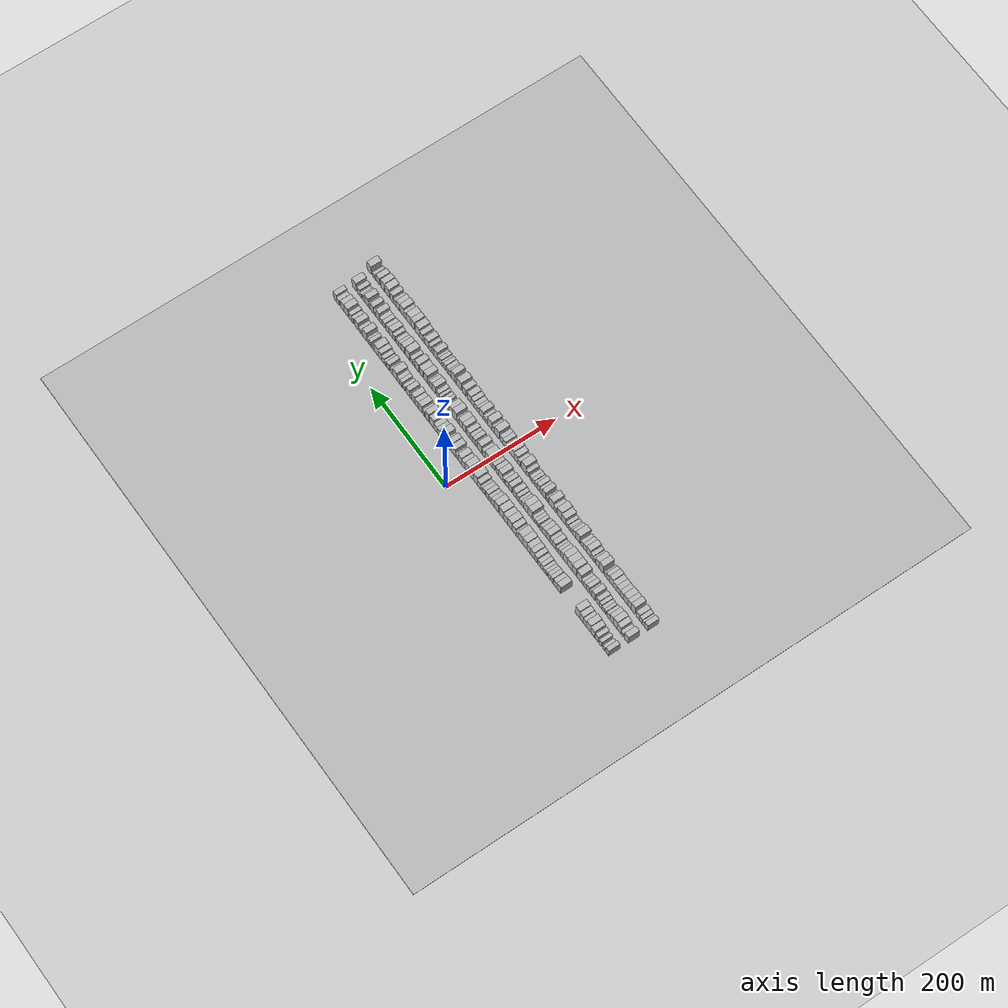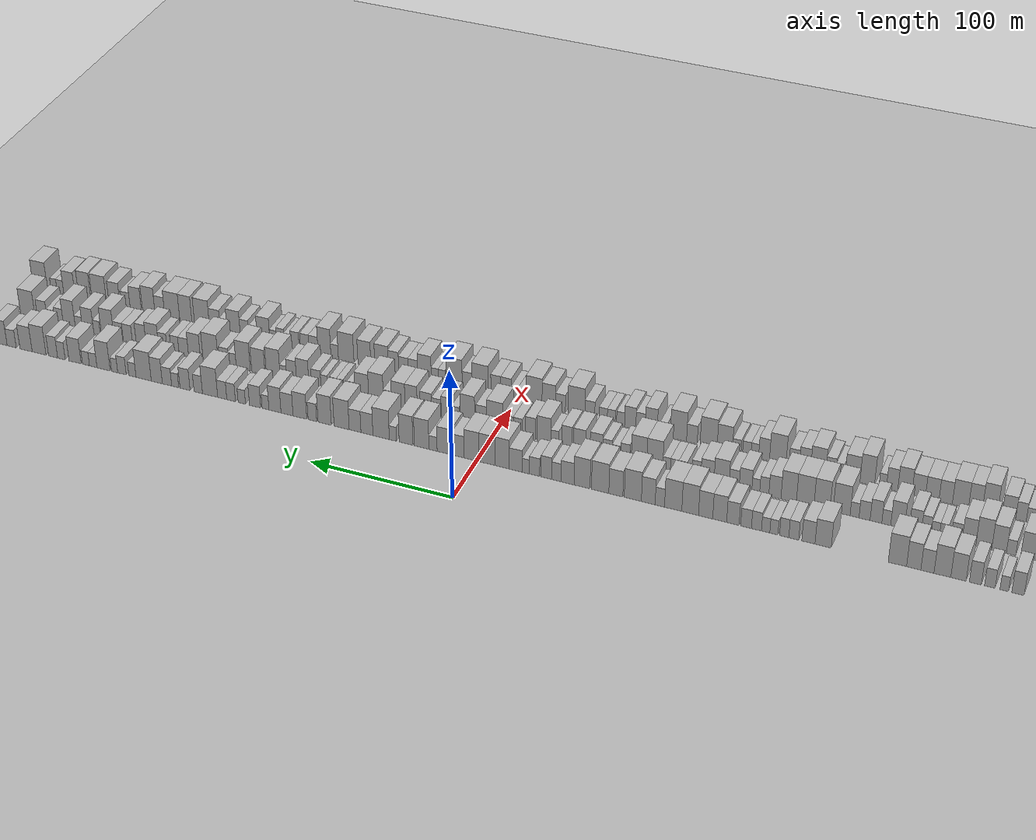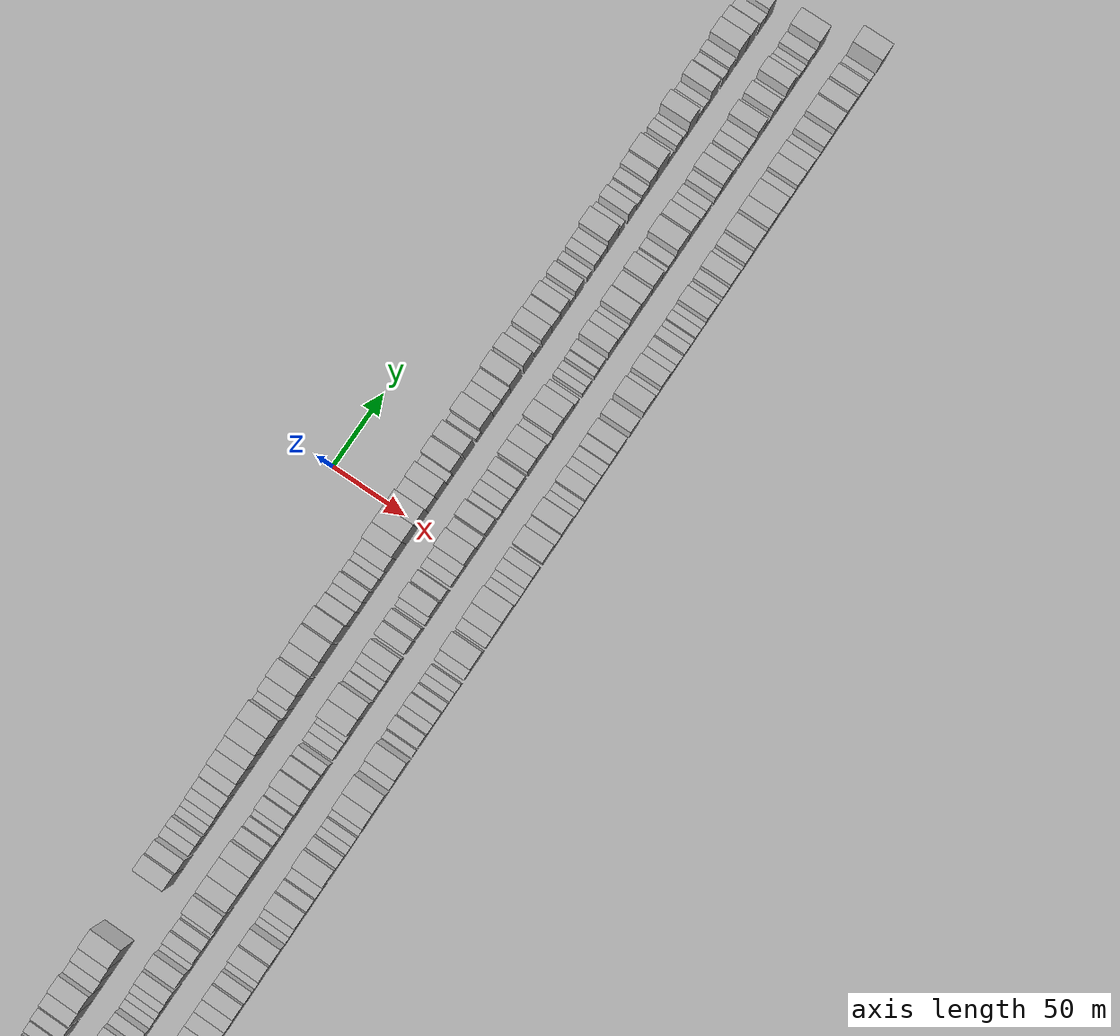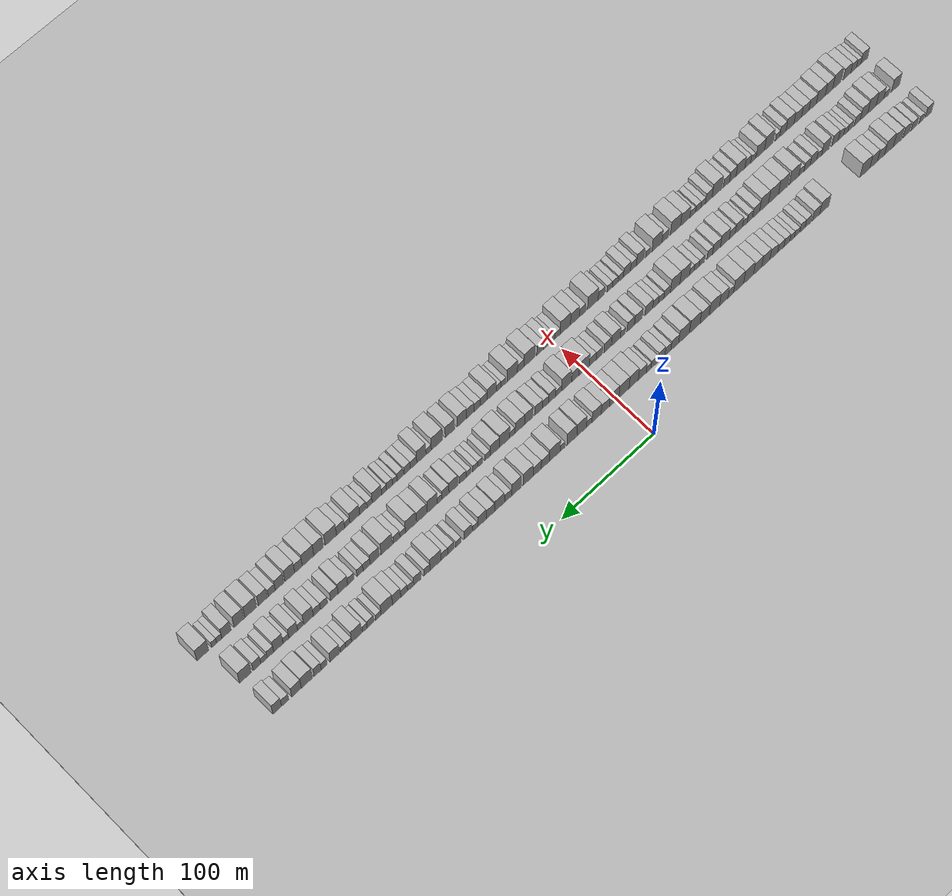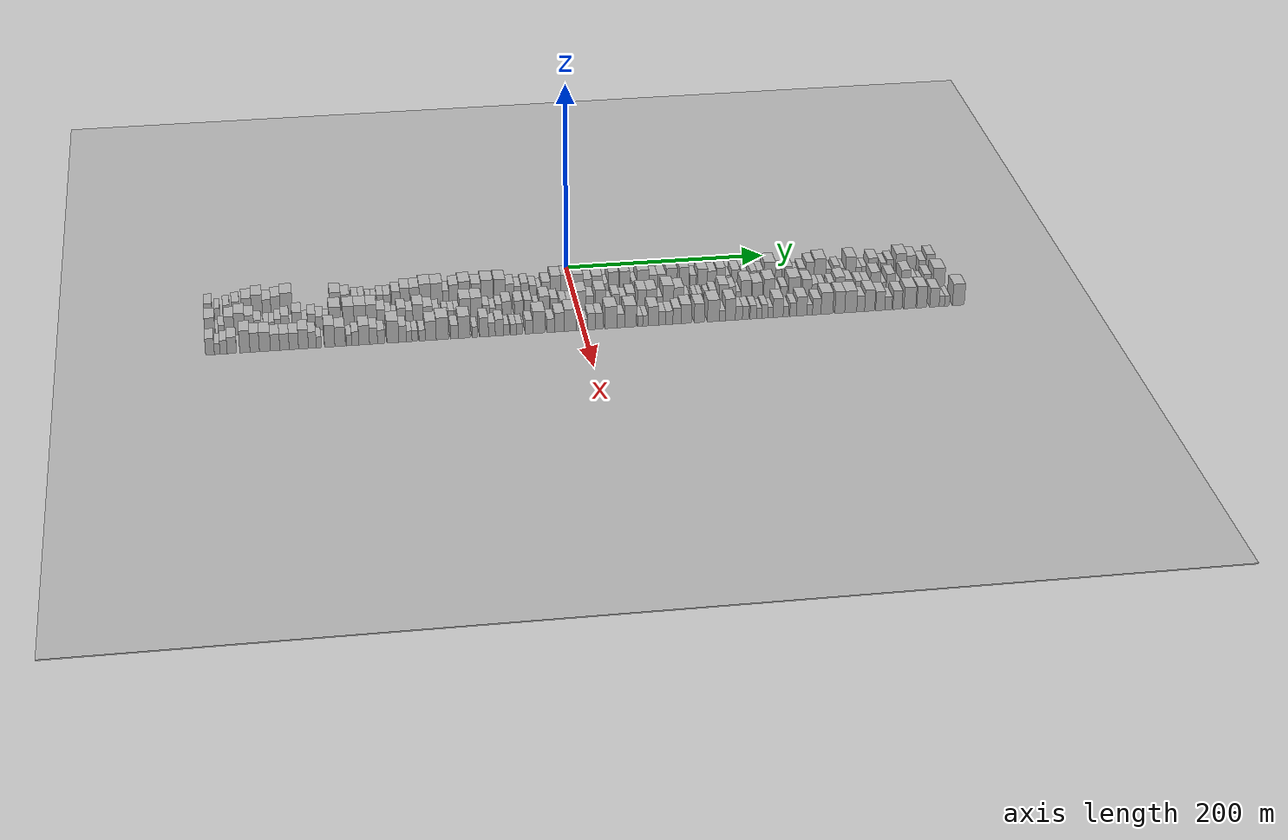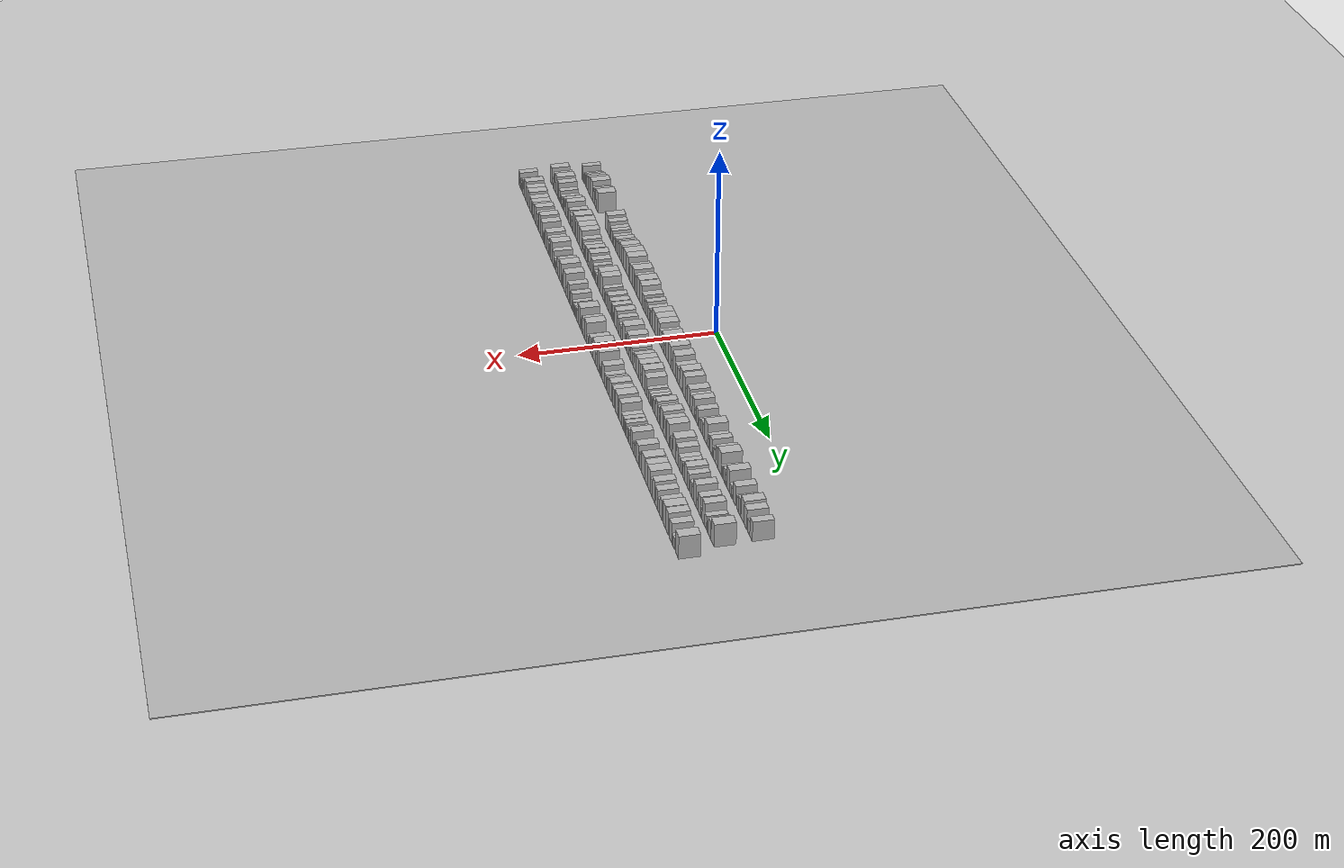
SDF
<?xml version="1.0" encoding="utf-8"?>

<sdf version="1.6">

   <world name="default">

      <gui fullscreen="0">

         <camera name="user_camera">

            <pose>-15 0 4.57585 0 0 0</pose>

            <view_controller>orbit</view_controller>

         </camera>

      </gui>

      <scene>

         <sky>

           <clouds>

             <speed>12</speed>

           </clouds>

         </sky>

         <ambient>0.4 0.4 0.4 1</ambient>

         <background>0.7 0.7 0.7 1</background>

         <shadows>1</shadows>

      </scene>

      <gravity>0 0 -9.8066</gravity>

      <magnetic_field>6e-06 2.3e-05 -4.2e-05</magnetic_field>

      <physics default="0" name="default_physics" type="ode">

         <ode>

            <solver>

               <type>quick</type>

               <iters>10</iters>

               <sor>1.0</sor>

               <use_dynamic_moi_rescaling>0</use_dynamic_moi_rescaling>

            </solver>

            <constraints>

               <cfm>0</cfm>

               <erp>0.2</erp>

               <contact_max_correcting_vel>100</contact_max_correcting_vel>

               <contact_surface_layer>0.001</contact_surface_layer>

            </constraints>

         </ode>

         <max_step_size>0.004</max_step_size>

         <real_time_factor>1</real_time_factor>

         <real_time_update_rate>250</real_time_update_rate>

      </physics>

      <light name="sun" type="directional">

         <cast_shadows>1</cast_shadows>

         <pose>0 0 10 0 0 0</pose>

         <diffuse>0.8 0.8 0.8 1</diffuse>

         <specular>0.2 0.2 0.2 1</specular>

         <attenuation>

            <range>1000</range>

            <constant>0.9</constant>

            <linear>0.01</linear>

            <quadratic>0.001</quadratic>

         </attenuation>

         <direction>-0.5 0.1 -0.9</direction>

      </light>

      <include>

         <name>ground_plane_1</name>

         <uri>model://HANNAS_ground_plane</uri>

         <pose>0 0 0  0 0 0</pose>

      </include>

      <include>

         <name>ground_plane_2</name>

         <uri>model://HANNAS_ground_plane</uri>

         <pose>100 0 0  0 0 0</pose>

      </include>

      <model name="building_1">

         <static>1</static>

         <pose frame="">50.0000 -356.2087 0 0.000000 0.000000 0.000000</pose>

         <link name="link">

            <pose frame="">0 0 9.00 0 0 0</pose>

            <collision name="collision">

               <geometry>

                  <box>

                     <size>20.0000 7.5826 18.0000</size>

                  </box>

               </geometry>

               <max_contacts>10</max_contacts>

               <surface>

                  <contact>

                     <ode/>

                  </contact>

                  <bounce/>

                  <friction>

                     <torsional>

                        <ode/>

                     </torsional>

                     <ode/>

                  </friction>

               </surface>

            </collision>

            <visual name="visual">

               <cast_shadows>0</cast_shadows>

               <geometry>

                  <box>

                     <size>20.0000 7.5826 18.0000</size>

                  </box>

               </geometry>

               <material>

                  <script>

                     <uri>model://HANNAS_wall/materials/scripts</uri>

                     <uri>model://HANNAS_wall/materials/textures</uri>

                     <name>vrc/HANNAS_wall</name>

                  </script>

               </material>

            </visual>

            <self_collide>0</self_collide>

            <enable_wind>0</enable_wind>

            <kinematic>0</kinematic>

         </link>

      </model>

      <model name="building_2">

         <static>1</static>

         <pose frame="">50.0000 -347.7883 0 0.000000 0.000000 0.000000</pose>

         <link name="link">

            <pose frame="">0 0 6.00 0 0 0</pose>

            <collision name="collision">

               <geometry>

                  <box>

                     <size>20.0000 5.2582 12.0000</size>

                  </box>

               </geometry>

               <max_contacts>10</max_contacts>

               <surface>

                  <contact>

                     <ode/>

                  </contact>

                  <bounce/>

                  <friction>

                     <torsional>

                        <ode/>

                     </torsional>

                     <ode/>

                  </friction>

               </surface>

            </collision>

            <visual name="visual">

               <cast_shadows>0</cast_shadows>

               <geometry>

                  <box>

                     <size>20.0000 5.2582 12.0000</size>

                  </box>

               </geometry>

               <material>

                  <script>

                     <uri>model://HANNAS_wall/materials/scripts</uri>

                     <uri>model://HANNAS_wall/materials/textures</uri>

                     <name>vrc/HANNAS_wall</name>

                  </script>

               </material>

            </visual>

            <self_collide>0</self_collide>

            <enable_wind>0</enable_wind>

            <kinematic>0</kinematic>

         </link>

      </model>

      <model name="building_3">

         <static>1</static>

         <pose frame="">50.0000 -338.8902 0 0.000000 0.000000 0.000000</pose>

         <link name="link">

            <pose frame="">0 0 7.50 0 0 0</pose>

            <collision name="collision">

               <geometry>

                  <box>

                     <size>20.0000 6.5379 15.0000</size>

                  </box>

               </geometry>

               <max_contacts>10</max_contacts>

               <surface>

                  <contact>

                     <ode/>

                  </contact>

                  <bounce/>

                  <friction>

                     <torsional>

                        <ode/>

                     </torsional>

                     <ode/>

                  </friction>

               </surface>

            </collision>

            <visual name="visual">

               <cast_shadows>0</cast_shadows>

               <geometry>

                  <box>

                     <size>20.0000 6.5379 15.0000</size>

                  </box>

               </geometry>

               <material>

                  <script>

                     <uri>model://HANNAS_wall/materials/scripts</uri>

                     <uri>model://HANNAS_wall/materials/textures</uri>

                     <name>vrc/HANNAS_wall</name>

                  </script>

               </material>

            </visual>

            <self_collide>0</self_collide>

            <enable_wind>0</enable_wind>

            <kinematic>0</kinematic>

         </link>

      </model>

      <model name="building_4">

         <static>1</static>

         <pose frame="">50.0000 -329.9099 0 0.000000 0.000000 0.000000</pose>

         <link name="link">

            <pose frame="">0 0 9.00 0 0 0</pose>

            <collision name="collision">

               <geometry>

                  <box>

                     <size>20.0000 7.4226 18.0000</size>

                  </box>

               </geometry>

               <max_contacts>10</max_contacts>

               <surface>

                  <contact>

                     <ode/>

                  </contact>

                  <bounce/>

                  <friction>

                     <torsional>

                        <ode/>

                     </torsional>

                     <ode/>

                  </friction>

               </surface>

            </collision>

            <visual name="visual">

               <cast_shadows>0</cast_shadows>

               <geometry>

                  <box>

                     <size>20.0000 7.4226 18.0000</size>

                  </box>

               </geometry>

               <material>

                  <script>

                     <uri>model://HANNAS_wall/materials/scripts</uri>

                     <uri>model://HANNAS_wall/materials/textures</uri>

                     <name>vrc/HANNAS_wall</name>

                  </script>

               </material>

            </visual>

            <self_collide>0</self_collide>

            <enable_wind>0</enable_wind>

            <kinematic>0</kinematic>

         </link>

      </model>

      <model name="building_5">

         <static>1</static>

         <pose frame="">50.0000 -319.4293 0 0.000000 0.000000 0.000000</pose>

         <link name="link">

            <pose frame="">0 0 10.50 0 0 0</pose>

            <collision name="collision">

               <geometry>

                  <box>

                     <size>20.0000 9.5387 21.0000</size>

                  </box>

               </geometry>

               <max_contacts>10</max_contacts>

               <surface>

                  <contact>

                     <ode/>

                  </contact>

                  <bounce/>

                  <friction>

                     <torsional>

                        <ode/>

                     </torsional>

                     <ode/>

                  </friction>

               </surface>

            </collision>

            <visual name="visual">

               <cast_shadows>0</cast_shadows>

               <geometry>

                  <box>

                     <size>20.0000 9.5387 21.0000</size>

                  </box>

               </geometry>

               <material>

                  <script>

                     <uri>model://HANNAS_wall/materials/scripts</uri>

                     <uri>model://HANNAS_wall/materials/textures</uri>

                     <name>vrc/HANNAS_wall</name>

                  </script>

               </material>

            </visual>

            <self_collide>0</self_collide>

            <enable_wind>0</enable_wind>

            <kinematic>0</kinematic>

         </link>

      </model>

      <model name="building_6">

         <static>1</static>

         <pose frame="">50.0000 -309.4172 0 0.000000 0.000000 0.000000</pose>

         <link name="link">

            <pose frame="">0 0 12.00 0 0 0</pose>

            <collision name="collision">

               <geometry>

                  <box>

                     <size>20.0000 10.4856 24.0000</size>

                  </box>

               </geometry>

               <max_contacts>10</max_contacts>

               <surface>

                  <contact>

                     <ode/>

                  </contact>

                  <bounce/>

                  <friction>

                     <torsional>

                        <ode/>

                     </torsional>

                     <ode/>

                  </friction>

               </surface>

            </collision>

            <visual name="visual">

               <cast_shadows>0</cast_shadows>

               <geometry>

                  <box>

                     <size>20.0000 10.4856 24.0000</size>

                  </box>

               </geometry>

               <material>

                  <script>

                     <uri>model://HANNAS_wall/materials/scripts</uri>

                     <uri>model://HANNAS_wall/materials/textures</uri>

                     <name>vrc/HANNAS_wall</name>

                  </script>

               </material>

            </visual>

            <self_collide>0</self_collide>

            <enable_wind>0</enable_wind>

            <kinematic>0</kinematic>

         </link>

      </model>

      <model name="building_7">

         <static>1</static>

         <pose frame="">50.0000 -300.0538 0 0.000000 0.000000 0.000000</pose>

         <link name="link">

            <pose frame="">0 0 9.00 0 0 0</pose>

            <collision name="collision">

               <geometry>

                  <box>

                     <size>20.0000 8.2411 18.0000</size>

                  </box>

               </geometry>

               <max_contacts>10</max_contacts>

               <surface>

                  <contact>

                     <ode/>

                  </contact>

                  <bounce/>

                  <friction>

                     <torsional>

                        <ode/>

                     </torsional>

                     <ode/>

                  </friction>

               </surface>

            </collision>

            <visual name="visual">

               <cast_shadows>0</cast_shadows>

               <geometry>

                  <box>

                     <size>20.0000 8.2411 18.0000</size>

                  </box>

               </geometry>

               <material>

                  <script>

                     <uri>model://HANNAS_wall/materials/scripts</uri>

                     <uri>model://HANNAS_wall/materials/textures</uri>

                     <name>vrc/HANNAS_wall</name>

                  </script>

               </material>

            </visual>

            <self_collide>0</self_collide>

            <enable_wind>0</enable_wind>

            <kinematic>0</kinematic>

         </link>

      </model>

      <model name="building_8">

         <static>1</static>

         <pose frame="">50.0000 -291.4383 0 0.000000 0.000000 0.000000</pose>

         <link name="link">

            <pose frame="">0 0 10.50 0 0 0</pose>

            <collision name="collision">

               <geometry>

                  <box>

                     <size>20.0000 8.9898 21.0000</size>

                  </box>

               </geometry>

               <max_contacts>10</max_contacts>

               <surface>

                  <contact>

                     <ode/>

                  </contact>

                  <bounce/>

                  <friction>

                     <torsional>

                        <ode/>

                     </torsional>

                     <ode/>

                  </friction>

               </surface>

            </collision>

            <visual name="visual">

               <cast_shadows>0</cast_shadows>

               <geometry>

                  <box>

                     <size>20.0000 8.9898 21.0000</size>

                  </box>

               </geometry>

               <material>

                  <script>

                     <uri>model://HANNAS_wall/materials/scripts</uri>

                     <uri>model://HANNAS_wall/materials/textures</uri>

                     <name>vrc/HANNAS_wall</name>

                  </script>

               </material>

            </visual>

            <self_collide>0</self_collide>

            <enable_wind>0</enable_wind>

            <kinematic>0</kinematic>

         </link>

      </model>

      <model name="building_9">

         <static>1</static>

         <pose frame="">50.0000 -281.1544 0 0.000000 0.000000 0.000000</pose>

         <link name="link">

            <pose frame="">0 0 12.00 0 0 0</pose>

            <collision name="collision">

               <geometry>

                  <box>

                     <size>20.0000 11.5780 24.0000</size>

                  </box>

               </geometry>

               <max_contacts>10</max_contacts>

               <surface>

                  <contact>

                     <ode/>

                  </contact>

                  <bounce/>

                  <friction>

                     <torsional>

                        <ode/>

                     </torsional>

                     <ode/>

                  </friction>

               </surface>

            </collision>

            <visual name="visual">

               <cast_shadows>0</cast_shadows>

               <geometry>

                  <box>

                     <size>20.0000 11.5780 24.0000</size>

                  </box>

               </geometry>

               <material>

                  <script>

                     <uri>model://HANNAS_wall/materials/scripts</uri>

                     <uri>model://HANNAS_wall/materials/textures</uri>

                     <name>vrc/HANNAS_wall</name>

                  </script>

               </material>

            </visual>

            <self_collide>0</self_collide>

            <enable_wind>0</enable_wind>

            <kinematic>0</kinematic>

         </link>

      </model>

      <model name="building_10">

         <static>1</static>

         <pose frame="">50.0000 -233.7191 0 0.000000 0.000000 0.000000</pose>

         <link name="link">

            <pose frame="">0 0 10.50 0 0 0</pose>

            <collision name="collision">

               <geometry>

                  <box>

                     <size>20.0000 10.4308 21.0000</size>

                  </box>

               </geometry>

               <max_contacts>10</max_contacts>

               <surface>

                  <contact>

                     <ode/>

                  </contact>

                  <bounce/>

                  <friction>

                     <torsional>

                        <ode/>

                     </torsional>

                     <ode/>

                  </friction>

               </surface>

            </collision>

            <visual name="visual">

               <cast_shadows>0</cast_shadows>

               <geometry>

                  <box>

                     <size>20.0000 10.4308 21.0000</size>

                  </box>

               </geometry>

               <material>

                  <script>

                     <uri>model://HANNAS_wall/materials/scripts</uri>

                     <uri>model://HANNAS_wall/materials/textures</uri>

                     <name>vrc/HANNAS_wall</name>

                  </script>

               </material>

            </visual>

            <self_collide>0</self_collide>

            <enable_wind>0</enable_wind>

            <kinematic>0</kinematic>

         </link>

      </model>

      <model name="building_11">

         <static>1</static>

         <pose frame="">50.0000 -224.2286 0 0.000000 0.000000 0.000000</pose>

         <link name="link">

            <pose frame="">0 0 9.00 0 0 0</pose>

            <collision name="collision">

               <geometry>

                  <box>

                     <size>20.0000 8.5502 18.0000</size>

                  </box>

               </geometry>

               <max_contacts>10</max_contacts>

               <surface>

                  <contact>

                     <ode/>

                  </contact>

                  <bounce/>

                  <friction>

                     <torsional>

                        <ode/>

                     </torsional>

                     <ode/>

                  </friction>

               </surface>

            </collision>

            <visual name="visual">

               <cast_shadows>0</cast_shadows>

               <geometry>

                  <box>

                     <size>20.0000 8.5502 18.0000</size>

                  </box>

               </geometry>

               <material>

                  <script>

                     <uri>model://HANNAS_wall/materials/scripts</uri>

                     <uri>model://HANNAS_wall/materials/textures</uri>

                     <name>vrc/HANNAS_wall</name>

                  </script>

               </material>

            </visual>

            <self_collide>0</self_collide>

            <enable_wind>0</enable_wind>

            <kinematic>0</kinematic>

         </link>

      </model>

      <model name="building_12">

         <static>1</static>

         <pose frame="">50.0000 -214.7280 0 0.000000 0.000000 0.000000</pose>

         <link name="link">

            <pose frame="">0 0 7.50 0 0 0</pose>

            <collision name="collision">

               <geometry>

                  <box>

                     <size>20.0000 6.4510 15.0000</size>

                  </box>

               </geometry>

               <max_contacts>10</max_contacts>

               <surface>

                  <contact>

                     <ode/>

                  </contact>

                  <bounce/>

                  <friction>

                     <torsional>

                        <ode/>

                     </torsional>

                     <ode/>

                  </friction>

               </surface>

            </collision>

            <visual name="visual">

               <cast_shadows>0</cast_shadows>

               <geometry>

                  <box>

                     <size>20.0000 6.4510 15.0000</size>

                  </box>

               </geometry>

               <material>

                  <script>

                     <uri>model://HANNAS_wall/materials/scripts</uri>

                     <uri>model://HANNAS_wall/materials/textures</uri>

                     <name>vrc/HANNAS_wall</name>

                  </script>

               </material>

            </visual>

            <self_collide>0</self_collide>

            <enable_wind>0</enable_wind>

            <kinematic>0</kinematic>

         </link>

      </model>

      <model name="building_13">

         <static>1</static>

         <pose frame="">50.0000 -208.4955 0 0.000000 0.000000 0.000000</pose>

         <link name="link">

            <pose frame="">0 0 7.50 0 0 0</pose>

            <collision name="collision">

               <geometry>

                  <box>

                     <size>20.0000 6.0138 15.0000</size>

                  </box>

               </geometry>

               <max_contacts>10</max_contacts>

               <surface>

                  <contact>

                     <ode/>

                  </contact>

                  <bounce/>

                  <friction>

                     <torsional>

                        <ode/>

                     </torsional>

                     <ode/>

                  </friction>

               </surface>

            </collision>

            <visual name="visual">

               <cast_shadows>0</cast_shadows>

               <geometry>

                  <box>

                     <size>20.0000 6.0138 15.0000</size>

                  </box>

               </geometry>

               <material>

                  <script>

                     <uri>model://HANNAS_wall/materials/scripts</uri>

                     <uri>model://HANNAS_wall/materials/textures</uri>

                     <name>vrc/HANNAS_wall</name>

                  </script>

               </material>

            </visual>

            <self_collide>0</self_collide>

            <enable_wind>0</enable_wind>

            <kinematic>0</kinematic>

         </link>

      </model>

      <model name="building_14">

         <static>1</static>

         <pose frame="">50.0000 -201.8346 0 0.000000 0.000000 0.000000</pose>

         <link name="link">

            <pose frame="">0 0 6.00 0 0 0</pose>

            <collision name="collision">

               <geometry>

                  <box>

                     <size>20.0000 5.3080 12.0000</size>

                  </box>

               </geometry>

               <max_contacts>10</max_contacts>

               <surface>

                  <contact>

                     <ode/>

                  </contact>

                  <bounce/>

                  <friction>

                     <torsional>

                        <ode/>

                     </torsional>

                     <ode/>

                  </friction>

               </surface>

            </collision>

            <visual name="visual">

               <cast_shadows>0</cast_shadows>

               <geometry>

                  <box>

                     <size>20.0000 5.3080 12.0000</size>

                  </box>

               </geometry>

               <material>

                  <script>

                     <uri>model://HANNAS_wall/materials/scripts</uri>

                     <uri>model://HANNAS_wall/materials/textures</uri>

                     <name>vrc/HANNAS_wall</name>

                  </script>

               </material>

            </visual>

            <self_collide>0</self_collide>

            <enable_wind>0</enable_wind>

            <kinematic>0</kinematic>

         </link>

      </model>

      <model name="building_15">

         <static>1</static>

         <pose frame="">50.0000 -196.4232 0 0.000000 0.000000 0.000000</pose>

         <link name="link">

            <pose frame="">0 0 6.00 0 0 0</pose>

            <collision name="collision">

               <geometry>

                  <box>

                     <size>20.0000 5.5147 12.0000</size>

                  </box>

               </geometry>

               <max_contacts>10</max_contacts>

               <surface>

                  <contact>

                     <ode/>

                  </contact>

                  <bounce/>

                  <friction>

                     <torsional>

                        <ode/>

                     </torsional>

                     <ode/>

                  </friction>

               </surface>

            </collision>

            <visual name="visual">

               <cast_shadows>0</cast_shadows>

               <geometry>

                  <box>

                     <size>20.0000 5.5147 12.0000</size>

                  </box>

               </geometry>

               <material>

                  <script>

                     <uri>model://HANNAS_wall/materials/scripts</uri>

                     <uri>model://HANNAS_wall/materials/textures</uri>

                     <name>vrc/HANNAS_wall</name>

                  </script>

               </material>

            </visual>

            <self_collide>0</self_collide>

            <enable_wind>0</enable_wind>

            <kinematic>0</kinematic>

         </link>

      </model>

      <model name="building_16">

         <static>1</static>

         <pose frame="">50.0000 -190.3855 0 0.000000 0.000000 0.000000</pose>

         <link name="link">

            <pose frame="">0 0 7.50 0 0 0</pose>

            <collision name="collision">

               <geometry>

                  <box>

                     <size>20.0000 6.5609 15.0000</size>

                  </box>

               </geometry>

               <max_contacts>10</max_contacts>

               <surface>

                  <contact>

                     <ode/>

                  </contact>

                  <bounce/>

                  <friction>

                     <torsional>

                        <ode/>

                     </torsional>

                     <ode/>

                  </friction>

               </surface>

            </collision>

            <visual name="visual">

               <cast_shadows>0</cast_shadows>

               <geometry>

                  <box>

                     <size>20.0000 6.5609 15.0000</size>

                  </box>

               </geometry>

               <material>

                  <script>

                     <uri>model://HANNAS_wall/materials/scripts</uri>

                     <uri>model://HANNAS_wall/materials/textures</uri>

                     <name>vrc/HANNAS_wall</name>

                  </script>

               </material>

            </visual>

            <self_collide>0</self_collide>

            <enable_wind>0</enable_wind>

            <kinematic>0</kinematic>

         </link>

      </model>

      <model name="building_17">

         <static>1</static>

         <pose frame="">50.0000 -183.5652 0 0.000000 0.000000 0.000000</pose>

         <link name="link">

            <pose frame="">0 0 7.50 0 0 0</pose>

            <collision name="collision">

               <geometry>

                  <box>

                     <size>20.0000 7.0797 15.0000</size>

                  </box>

               </geometry>

               <max_contacts>10</max_contacts>

               <surface>

                  <contact>

                     <ode/>

                  </contact>

                  <bounce/>

                  <friction>

                     <torsional>

                        <ode/>

                     </torsional>

                     <ode/>

                  </friction>

               </surface>

            </collision>

            <visual name="visual">

               <cast_shadows>0</cast_shadows>

               <geometry>

                  <box>

                     <size>20.0000 7.0797 15.0000</size>

                  </box>

               </geometry>

               <material>

                  <script>

                     <uri>model://HANNAS_wall/materials/scripts</uri>

                     <uri>model://HANNAS_wall/materials/textures</uri>

                     <name>vrc/HANNAS_wall</name>

                  </script>

               </material>

            </visual>

            <self_collide>0</self_collide>

            <enable_wind>0</enable_wind>

            <kinematic>0</kinematic>

         </link>

      </model>

      <model name="building_18">

         <static>1</static>

         <pose frame="">50.0000 -174.9120 0 0.000000 0.000000 0.000000</pose>

         <link name="link">

            <pose frame="">0 0 9.00 0 0 0</pose>

            <collision name="collision">

               <geometry>

                  <box>

                     <size>20.0000 8.2267 18.0000</size>

                  </box>

               </geometry>

               <max_contacts>10</max_contacts>

               <surface>

                  <contact>

                     <ode/>

                  </contact>

                  <bounce/>

                  <friction>

                     <torsional>

                        <ode/>

                     </torsional>

                     <ode/>

                  </friction>

               </surface>

            </collision>

            <visual name="visual">

               <cast_shadows>0</cast_shadows>

               <geometry>

                  <box>

                     <size>20.0000 8.2267 18.0000</size>

                  </box>

               </geometry>

               <material>

                  <script>

                     <uri>model://HANNAS_wall/materials/scripts</uri>

                     <uri>model://HANNAS_wall/materials/textures</uri>

                     <name>vrc/HANNAS_wall</name>

                  </script>

               </material>

            </visual>

            <self_collide>0</self_collide>

            <enable_wind>0</enable_wind>

            <kinematic>0</kinematic>

         </link>

      </model>

      <model name="building_19">

         <static>1</static>

         <pose frame="">50.0000 -166.1909 0 0.000000 0.000000 0.000000</pose>

         <link name="link">

            <pose frame="">0 0 10.50 0 0 0</pose>

            <collision name="collision">

               <geometry>

                  <box>

                     <size>20.0000 9.2155 21.0000</size>

                  </box>

               </geometry>

               <max_contacts>10</max_contacts>

               <surface>

                  <contact>

                     <ode/>

                  </contact>

                  <bounce/>

                  <friction>

                     <torsional>

                        <ode/>

                     </torsional>

                     <ode/>

                  </friction>

               </surface>

            </collision>

            <visual name="visual">

               <cast_shadows>0</cast_shadows>

               <geometry>

                  <box>

                     <size>20.0000 9.2155 21.0000</size>

                  </box>

               </geometry>

               <material>

                  <script>

                     <uri>model://HANNAS_wall/materials/scripts</uri>

                     <uri>model://HANNAS_wall/materials/textures</uri>

                     <name>vrc/HANNAS_wall</name>

                  </script>

               </material>

            </visual>

            <self_collide>0</self_collide>

            <enable_wind>0</enable_wind>

            <kinematic>0</kinematic>

         </link>

      </model>

      <model name="building_20">

         <static>1</static>

         <pose frame="">50.0000 -156.8598 0 0.000000 0.000000 0.000000</pose>

         <link name="link">

            <pose frame="">0 0 10.50 0 0 0</pose>

            <collision name="collision">

               <geometry>

                  <box>

                     <size>20.0000 9.4467 21.0000</size>

                  </box>

               </geometry>

               <max_contacts>10</max_contacts>

               <surface>

                  <contact>

                     <ode/>

                  </contact>

                  <bounce/>

                  <friction>

                     <torsional>

                        <ode/>

                     </torsional>

                     <ode/>

                  </friction>

               </surface>

            </collision>

            <visual name="visual">

               <cast_shadows>0</cast_shadows>

               <geometry>

                  <box>

                     <size>20.0000 9.4467 21.0000</size>

                  </box>

               </geometry>

               <material>

                  <script>

                     <uri>model://HANNAS_wall/materials/scripts</uri>

                     <uri>model://HANNAS_wall/materials/textures</uri>

                     <name>vrc/HANNAS_wall</name>

                  </script>

               </material>

            </visual>

            <self_collide>0</self_collide>

            <enable_wind>0</enable_wind>

            <kinematic>0</kinematic>

         </link>

      </model>

      <model name="building_21">

         <static>1</static>

         <pose frame="">50.0000 -146.5706 0 0.000000 0.000000 0.000000</pose>

         <link name="link">

            <pose frame="">0 0 12.00 0 0 0</pose>

            <collision name="collision">

               <geometry>

                  <box>

                     <size>20.0000 11.1319 24.0000</size>

                  </box>

               </geometry>

               <max_contacts>10</max_contacts>

               <surface>

                  <contact>

                     <ode/>

                  </contact>

                  <bounce/>

                  <friction>

                     <torsional>

                        <ode/>

                     </torsional>

                     <ode/>

                  </friction>

               </surface>

            </collision>

            <visual name="visual">

               <cast_shadows>0</cast_shadows>

               <geometry>

                  <box>

                     <size>20.0000 11.1319 24.0000</size>

                  </box>

               </geometry>

               <material>

                  <script>

                     <uri>model://HANNAS_wall/materials/scripts</uri>

                     <uri>model://HANNAS_wall/materials/textures</uri>

                     <name>vrc/HANNAS_wall</name>

                  </script>

               </material>

            </visual>

            <self_collide>0</self_collide>

            <enable_wind>0</enable_wind>

            <kinematic>0</kinematic>

         </link>

      </model>

      <model name="building_22">

         <static>1</static>

         <pose frame="">50.0000 -135.2333 0 0.000000 0.000000 0.000000</pose>

         <link name="link">

            <pose frame="">0 0 12.00 0 0 0</pose>

            <collision name="collision">

               <geometry>

                  <box>

                     <size>20.0000 11.5426 24.0000</size>

                  </box>

               </geometry>

               <max_contacts>10</max_contacts>

               <surface>

                  <contact>

                     <ode/>

                  </contact>

                  <bounce/>

                  <friction>

                     <torsional>

                        <ode/>

                     </torsional>

                     <ode/>

                  </friction>

               </surface>

            </collision>

            <visual name="visual">

               <cast_shadows>0</cast_shadows>

               <geometry>

                  <box>

                     <size>20.0000 11.5426 24.0000</size>

                  </box>

               </geometry>

               <material>

                  <script>

                     <uri>model://HANNAS_wall/materials/scripts</uri>

                     <uri>model://HANNAS_wall/materials/textures</uri>

                     <name>vrc/HANNAS_wall</name>

                  </script>

               </material>

            </visual>

            <self_collide>0</self_collide>

            <enable_wind>0</enable_wind>

            <kinematic>0</kinematic>

         </link>

      </model>

      <model name="building_23">

         <static>1</static>

         <pose frame="">50.0000 -126.3119 0 0.000000 0.000000 0.000000</pose>

         <link name="link">

            <pose frame="">0 0 7.50 0 0 0</pose>

            <collision name="collision">

               <geometry>

                  <box>

                     <size>20.0000 6.3001 15.0000</size>

                  </box>

               </geometry>

               <max_contacts>10</max_contacts>

               <surface>

                  <contact>

                     <ode/>

                  </contact>

                  <bounce/>

                  <friction>

                     <torsional>

                        <ode/>

                     </torsional>

                     <ode/>

                  </friction>

               </surface>

            </collision>

            <visual name="visual">

               <cast_shadows>0</cast_shadows>

               <geometry>

                  <box>

                     <size>20.0000 6.3001 15.0000</size>

                  </box>

               </geometry>

               <material>

                  <script>

                     <uri>model://HANNAS_wall/materials/scripts</uri>

                     <uri>model://HANNAS_wall/materials/textures</uri>

                     <name>vrc/HANNAS_wall</name>

                  </script>

               </material>

            </visual>

            <self_collide>0</self_collide>

            <enable_wind>0</enable_wind>

            <kinematic>0</kinematic>

         </link>

      </model>

      <model name="building_24">

         <static>1</static>

         <pose frame="">50.0000 -118.5132 0 0.000000 0.000000 0.000000</pose>

         <link name="link">

            <pose frame="">0 0 10.50 0 0 0</pose>

            <collision name="collision">

               <geometry>

                  <box>

                     <size>20.0000 9.2973 21.0000</size>

                  </box>

               </geometry>

               <max_contacts>10</max_contacts>

               <surface>

                  <contact>

                     <ode/>

                  </contact>

                  <bounce/>

                  <friction>

                     <torsional>

                        <ode/>

                     </torsional>

                     <ode/>

                  </friction>

               </surface>

            </collision>

            <visual name="visual">

               <cast_shadows>0</cast_shadows>

               <geometry>

                  <box>

                     <size>20.0000 9.2973 21.0000</size>

                  </box>

               </geometry>

               <material>

                  <script>

                     <uri>model://HANNAS_wall/materials/scripts</uri>

                     <uri>model://HANNAS_wall/materials/textures</uri>

                     <name>vrc/HANNAS_wall</name>

                  </script>

               </material>

            </visual>

            <self_collide>0</self_collide>

            <enable_wind>0</enable_wind>

            <kinematic>0</kinematic>

         </link>

      </model>

      <model name="building_25">

         <static>1</static>

         <pose frame="">50.0000 -108.0796 0 0.000000 0.000000 0.000000</pose>

         <link name="link">

            <pose frame="">0 0 12.00 0 0 0</pose>

            <collision name="collision">

               <geometry>

                  <box>

                     <size>20.0000 11.5699 24.0000</size>

                  </box>

               </geometry>

               <max_contacts>10</max_contacts>

               <surface>

                  <contact>

                     <ode/>

                  </contact>

                  <bounce/>

                  <friction>

                     <torsional>

                        <ode/>

                     </torsional>

                     <ode/>

                  </friction>

               </surface>

            </collision>

            <visual name="visual">

               <cast_shadows>0</cast_shadows>

               <geometry>

                  <box>

                     <size>20.0000 11.5699 24.0000</size>

                  </box>

               </geometry>

               <material>

                  <script>

                     <uri>model://HANNAS_wall/materials/scripts</uri>

                     <uri>model://HANNAS_wall/materials/textures</uri>

                     <name>vrc/HANNAS_wall</name>

                  </script>

               </material>

            </visual>

            <self_collide>0</self_collide>

            <enable_wind>0</enable_wind>

            <kinematic>0</kinematic>

         </link>

      </model>

      <model name="building_26">

         <static>1</static>

         <pose frame="">50.0000 -96.5357 0 0.000000 0.000000 0.000000</pose>

         <link name="link">

            <pose frame="">0 0 10.50 0 0 0</pose>

            <collision name="collision">

               <geometry>

                  <box>

                     <size>20.0000 9.5178 21.0000</size>

                  </box>

               </geometry>

               <max_contacts>10</max_contacts>

               <surface>

                  <contact>

                     <ode/>

                  </contact>

                  <bounce/>

                  <friction>

                     <torsional>

                        <ode/>

                     </torsional>

                     <ode/>

                  </friction>

               </surface>

            </collision>

            <visual name="visual">

               <cast_shadows>0</cast_shadows>

               <geometry>

                  <box>

                     <size>20.0000 9.5178 21.0000</size>

                  </box>

               </geometry>

               <material>

                  <script>

                     <uri>model://HANNAS_wall/materials/scripts</uri>

                     <uri>model://HANNAS_wall/materials/textures</uri>

                     <name>vrc/HANNAS_wall</name>

                  </script>

               </material>

            </visual>

            <self_collide>0</self_collide>

            <enable_wind>0</enable_wind>

            <kinematic>0</kinematic>

         </link>

      </model>

      <model name="building_27">

         <static>1</static>

         <pose frame="">50.0000 -85.8645 0 0.000000 0.000000 0.000000</pose>

         <link name="link">

            <pose frame="">0 0 12.00 0 0 0</pose>

            <collision name="collision">

               <geometry>

                  <box>

                     <size>20.0000 11.8246 24.0000</size>

                  </box>

               </geometry>

               <max_contacts>10</max_contacts>

               <surface>

                  <contact>

                     <ode/>

                  </contact>

                  <bounce/>

                  <friction>

                     <torsional>

                        <ode/>

                     </torsional>

                     <ode/>

                  </friction>

               </surface>

            </collision>

            <visual name="visual">

               <cast_shadows>0</cast_shadows>

               <geometry>

                  <box>

                     <size>20.0000 11.8246 24.0000</size>

                  </box>

               </geometry>

               <material>

                  <script>

                     <uri>model://HANNAS_wall/materials/scripts</uri>

                     <uri>model://HANNAS_wall/materials/textures</uri>

                     <name>vrc/HANNAS_wall</name>

                  </script>

               </material>

            </visual>

            <self_collide>0</self_collide>

            <enable_wind>0</enable_wind>

            <kinematic>0</kinematic>

         </link>

      </model>

      <model name="building_28">

         <static>1</static>

         <pose frame="">50.0000 -73.4634 0 0.000000 0.000000 0.000000</pose>

         <link name="link">

            <pose frame="">0 0 12.00 0 0 0</pose>

            <collision name="collision">

               <geometry>

                  <box>

                     <size>20.0000 10.9775 24.0000</size>

                  </box>

               </geometry>

               <max_contacts>10</max_contacts>

               <surface>

                  <contact>

                     <ode/>

                  </contact>

                  <bounce/>

                  <friction>

                     <torsional>

                        <ode/>

                     </torsional>

                     <ode/>

                  </friction>

               </surface>

            </collision>

            <visual name="visual">

               <cast_shadows>0</cast_shadows>

               <geometry>

                  <box>

                     <size>20.0000 10.9775 24.0000</size>

                  </box>

               </geometry>

               <material>

                  <script>

                     <uri>model://HANNAS_wall/materials/scripts</uri>

                     <uri>model://HANNAS_wall/materials/textures</uri>

                     <name>vrc/HANNAS_wall</name>

                  </script>

               </material>

            </visual>

            <self_collide>0</self_collide>

            <enable_wind>0</enable_wind>

            <kinematic>0</kinematic>

         </link>

      </model>

      <model name="building_29">

         <static>1</static>

         <pose frame="">50.0000 -63.5556 0 0.000000 0.000000 0.000000</pose>

         <link name="link">

            <pose frame="">0 0 9.00 0 0 0</pose>

            <collision name="collision">

               <geometry>

                  <box>

                     <size>20.0000 8.8380 18.0000</size>

                  </box>

               </geometry>

               <max_contacts>10</max_contacts>

               <surface>

                  <contact>

                     <ode/>

                  </contact>

                  <bounce/>

                  <friction>

                     <torsional>

                        <ode/>

                     </torsional>

                     <ode/>

                  </friction>

               </surface>

            </collision>

            <visual name="visual">

               <cast_shadows>0</cast_shadows>

               <geometry>

                  <box>

                     <size>20.0000 8.8380 18.0000</size>

                  </box>

               </geometry>

               <material>

                  <script>

                     <uri>model://HANNAS_wall/materials/scripts</uri>

                     <uri>model://HANNAS_wall/materials/textures</uri>

                     <name>vrc/HANNAS_wall</name>

                  </script>

               </material>

            </visual>

            <self_collide>0</self_collide>

            <enable_wind>0</enable_wind>

            <kinematic>0</kinematic>

         </link>

      </model>

      <model name="building_30">

         <static>1</static>

         <pose frame="">50.0000 -55.8476 0 0.000000 0.000000 0.000000</pose>

         <link name="link">

            <pose frame="">0 0 7.50 0 0 0</pose>

            <collision name="collision">

               <geometry>

                  <box>

                     <size>20.0000 6.5781 15.0000</size>

                  </box>

               </geometry>

               <max_contacts>10</max_contacts>

               <surface>

                  <contact>

                     <ode/>

                  </contact>

                  <bounce/>

                  <friction>

                     <torsional>

                        <ode/>

                     </torsional>

                     <ode/>

                  </friction>

               </surface>

            </collision>

            <visual name="visual">

               <cast_shadows>0</cast_shadows>

               <geometry>

                  <box>

                     <size>20.0000 6.5781 15.0000</size>

                  </box>

               </geometry>

               <material>

                  <script>

                     <uri>model://HANNAS_wall/materials/scripts</uri>

                     <uri>model://HANNAS_wall/materials/textures</uri>

                     <name>vrc/HANNAS_wall</name>

                  </script>

               </material>

            </visual>

            <self_collide>0</self_collide>

            <enable_wind>0</enable_wind>

            <kinematic>0</kinematic>

         </link>

      </model>

      <model name="building_31">

         <static>1</static>

         <pose frame="">50.0000 -48.9078 0 0.000000 0.000000 0.000000</pose>

         <link name="link">

            <pose frame="">0 0 9.00 0 0 0</pose>

            <collision name="collision">

               <geometry>

                  <box>

                     <size>20.0000 7.3015 18.0000</size>

                  </box>

               </geometry>

               <max_contacts>10</max_contacts>

               <surface>

                  <contact>

                     <ode/>

                  </contact>

                  <bounce/>

                  <friction>

                     <torsional>

                        <ode/>

                     </torsional>

                     <ode/>

                  </friction>

               </surface>

            </collision>

            <visual name="visual">

               <cast_shadows>0</cast_shadows>

               <geometry>

                  <box>

                     <size>20.0000 7.3015 18.0000</size>

                  </box>

               </geometry>

               <material>

                  <script>

                     <uri>model://HANNAS_wall/materials/scripts</uri>

                     <uri>model://HANNAS_wall/materials/textures</uri>

                     <name>vrc/HANNAS_wall</name>

                  </script>

               </material>

            </visual>

            <self_collide>0</self_collide>

            <enable_wind>0</enable_wind>

            <kinematic>0</kinematic>

         </link>

      </model>

      <model name="building_32">

         <static>1</static>

         <pose frame="">50.0000 -40.7422 0 0.000000 0.000000 0.000000</pose>

         <link name="link">

            <pose frame="">0 0 7.50 0 0 0</pose>

            <collision name="collision">

               <geometry>

                  <box>

                     <size>20.0000 7.0297 15.0000</size>

                  </box>

               </geometry>

               <max_contacts>10</max_contacts>

               <surface>

                  <contact>

                     <ode/>

                  </contact>

                  <bounce/>

                  <friction>

                     <torsional>

                        <ode/>

                     </torsional>

                     <ode/>

                  </friction>

               </surface>

            </collision>

            <visual name="visual">

               <cast_shadows>0</cast_shadows>

               <geometry>

                  <box>

                     <size>20.0000 7.0297 15.0000</size>

                  </box>

               </geometry>

               <material>

                  <script>

                     <uri>model://HANNAS_wall/materials/scripts</uri>

                     <uri>model://HANNAS_wall/materials/textures</uri>

                     <name>vrc/HANNAS_wall</name>

                  </script>

               </material>

            </visual>

            <self_collide>0</self_collide>

            <enable_wind>0</enable_wind>

            <kinematic>0</kinematic>

         </link>

      </model>

      <model name="building_33">

         <static>1</static>

         <pose frame="">50.0000 -34.6302 0 0.000000 0.000000 0.000000</pose>

         <link name="link">

            <pose frame="">0 0 6.00 0 0 0</pose>

            <collision name="collision">

               <geometry>

                  <box>

                     <size>20.0000 5.1942 12.0000</size>

                  </box>

               </geometry>

               <max_contacts>10</max_contacts>

               <surface>

                  <contact>

                     <ode/>

                  </contact>

                  <bounce/>

                  <friction>

                     <torsional>

                        <ode/>

                     </torsional>

                     <ode/>

                  </friction>

               </surface>

            </collision>

            <visual name="visual">

               <cast_shadows>0</cast_shadows>

               <geometry>

                  <box>

                     <size>20.0000 5.1942 12.0000</size>

                  </box>

               </geometry>

               <material>

                  <script>

                     <uri>model://HANNAS_wall/materials/scripts</uri>

                     <uri>model://HANNAS_wall/materials/textures</uri>

                     <name>vrc/HANNAS_wall</name>

                  </script>

               </material>

            </visual>

            <self_collide>0</self_collide>

            <enable_wind>0</enable_wind>

            <kinematic>0</kinematic>

         </link>

      </model>

      <model name="building_34">

         <static>1</static>

         <pose frame="">50.0000 -27.5937 0 0.000000 0.000000 0.000000</pose>

         <link name="link">

            <pose frame="">0 0 9.00 0 0 0</pose>

            <collision name="collision">

               <geometry>

                  <box>

                     <size>20.0000 8.8788 18.0000</size>

                  </box>

               </geometry>

               <max_contacts>10</max_contacts>

               <surface>

                  <contact>

                     <ode/>

                  </contact>

                  <bounce/>

                  <friction>

                     <torsional>

                        <ode/>

                     </torsional>

                     <ode/>

                  </friction>

               </surface>

            </collision>

            <visual name="visual">

               <cast_shadows>0</cast_shadows>

               <geometry>

                  <box>

                     <size>20.0000 8.8788 18.0000</size>

                  </box>

               </geometry>

               <material>

                  <script>

                     <uri>model://HANNAS_wall/materials/scripts</uri>

                     <uri>model://HANNAS_wall/materials/textures</uri>

                     <name>vrc/HANNAS_wall</name>

                  </script>

               </material>

            </visual>

            <self_collide>0</self_collide>

            <enable_wind>0</enable_wind>

            <kinematic>0</kinematic>

         </link>

      </model>

      <model name="building_35">

         <static>1</static>

         <pose frame="">50.0000 -18.0670 0 0.000000 0.000000 0.000000</pose>

         <link name="link">

            <pose frame="">0 0 12.00 0 0 0</pose>

            <collision name="collision">

               <geometry>

                  <box>

                     <size>20.0000 10.1747 24.0000</size>

                  </box>

               </geometry>

               <max_contacts>10</max_contacts>

               <surface>

                  <contact>

                     <ode/>

                  </contact>

                  <bounce/>

                  <friction>

                     <torsional>

                        <ode/>

                     </torsional>

                     <ode/>

                  </friction>

               </surface>

            </collision>

            <visual name="visual">

               <cast_shadows>0</cast_shadows>

               <geometry>

                  <box>

                     <size>20.0000 10.1747 24.0000</size>

                  </box>

               </geometry>

               <material>

                  <script>

                     <uri>model://HANNAS_wall/materials/scripts</uri>

                     <uri>model://HANNAS_wall/materials/textures</uri>

                     <name>vrc/HANNAS_wall</name>

                  </script>

               </material>

            </visual>

            <self_collide>0</self_collide>

            <enable_wind>0</enable_wind>

            <kinematic>0</kinematic>

         </link>

      </model>

      <model name="building_36">

         <static>1</static>

         <pose frame="">50.0000 -7.3837 0 0.000000 0.000000 0.000000</pose>

         <link name="link">

            <pose frame="">0 0 12.00 0 0 0</pose>

            <collision name="collision">

               <geometry>

                  <box>

                     <size>20.0000 11.1919 24.0000</size>

                  </box>

               </geometry>

               <max_contacts>10</max_contacts>

               <surface>

                  <contact>

                     <ode/>

                  </contact>

                  <bounce/>

                  <friction>

                     <torsional>

                        <ode/>

                     </torsional>

                     <ode/>

                  </friction>

               </surface>

            </collision>

            <visual name="visual">

               <cast_shadows>0</cast_shadows>

               <geometry>

                  <box>

                     <size>20.0000 11.1919 24.0000</size>

                  </box>

               </geometry>

               <material>

                  <script>

                     <uri>model://HANNAS_wall/materials/scripts</uri>

                     <uri>model://HANNAS_wall/materials/textures</uri>

                     <name>vrc/HANNAS_wall</name>

                  </script>

               </material>

            </visual>

            <self_collide>0</self_collide>

            <enable_wind>0</enable_wind>

            <kinematic>0</kinematic>

         </link>

      </model>

      <model name="building_37">

         <static>1</static>

         <pose frame="">50.0000 3.4778 0 0.000000 0.000000 0.000000</pose>

         <link name="link">

            <pose frame="">0 0 12.00 0 0 0</pose>

            <collision name="collision">

               <geometry>

                  <box>

                     <size>20.0000 10.5311 24.0000</size>

                  </box>

               </geometry>

               <max_contacts>10</max_contacts>

               <surface>

                  <contact>

                     <ode/>

                  </contact>

                  <bounce/>

                  <friction>

                     <torsional>

                        <ode/>

                     </torsional>

                     <ode/>

                  </friction>

               </surface>

            </collision>

            <visual name="visual">

               <cast_shadows>0</cast_shadows>

               <geometry>

                  <box>

                     <size>20.0000 10.5311 24.0000</size>

                  </box>

               </geometry>

               <material>

                  <script>

                     <uri>model://HANNAS_wall/materials/scripts</uri>

                     <uri>model://HANNAS_wall/materials/textures</uri>

                     <name>vrc/HANNAS_wall</name>

                  </script>

               </material>

            </visual>

            <self_collide>0</self_collide>

            <enable_wind>0</enable_wind>

            <kinematic>0</kinematic>

         </link>

      </model>

      <model name="building_38">

         <static>1</static>

         <pose frame="">50.0000 13.2375 0 0.000000 0.000000 0.000000</pose>

         <link name="link">

            <pose frame="">0 0 9.00 0 0 0</pose>

            <collision name="collision">

               <geometry>

                  <box>

                     <size>20.0000 8.9883 18.0000</size>

                  </box>

               </geometry>

               <max_contacts>10</max_contacts>

               <surface>

                  <contact>

                     <ode/>

                  </contact>

                  <bounce/>

                  <friction>

                     <torsional>

                        <ode/>

                     </torsional>

                     <ode/>

                  </friction>

               </surface>

            </collision>

            <visual name="visual">

               <cast_shadows>0</cast_shadows>

               <geometry>

                  <box>

                     <size>20.0000 8.9883 18.0000</size>

                  </box>

               </geometry>

               <material>

                  <script>

                     <uri>model://HANNAS_wall/materials/scripts</uri>

                     <uri>model://HANNAS_wall/materials/textures</uri>

                     <name>vrc/HANNAS_wall</name>

                  </script>

               </material>

            </visual>

            <self_collide>0</self_collide>

            <enable_wind>0</enable_wind>

            <kinematic>0</kinematic>

         </link>

      </model>

      <model name="building_39">

         <static>1</static>

         <pose frame="">50.0000 22.7996 0 0.000000 0.000000 0.000000</pose>

         <link name="link">

            <pose frame="">0 0 10.50 0 0 0</pose>

            <collision name="collision">

               <geometry>

                  <box>

                     <size>20.0000 10.1359 21.0000</size>

                  </box>

               </geometry>

               <max_contacts>10</max_contacts>

               <surface>

                  <contact>

                     <ode/>

                  </contact>

                  <bounce/>

                  <friction>

                     <torsional>

                        <ode/>

                     </torsional>

                     <ode/>

                  </friction>

               </surface>

            </collision>

            <visual name="visual">

               <cast_shadows>0</cast_shadows>

               <geometry>

                  <box>

                     <size>20.0000 10.1359 21.0000</size>

                  </box>

               </geometry>

               <material>

                  <script>

                     <uri>model://HANNAS_wall/materials/scripts</uri>

                     <uri>model://HANNAS_wall/materials/textures</uri>

                     <name>vrc/HANNAS_wall</name>

                  </script>

               </material>

            </visual>

            <self_collide>0</self_collide>

            <enable_wind>0</enable_wind>

            <kinematic>0</kinematic>

         </link>

      </model>

      <model name="building_40">

         <static>1</static>

         <pose frame="">50.0000 30.7865 0 0.000000 0.000000 0.000000</pose>

         <link name="link">

            <pose frame="">0 0 6.00 0 0 0</pose>

            <collision name="collision">

               <geometry>

                  <box>

                     <size>20.0000 5.8380 12.0000</size>

                  </box>

               </geometry>

               <max_contacts>10</max_contacts>

               <surface>

                  <contact>

                     <ode/>

                  </contact>

                  <bounce/>

                  <friction>

                     <torsional>

                        <ode/>

                     </torsional>

                     <ode/>

                  </friction>

               </surface>

            </collision>

            <visual name="visual">

               <cast_shadows>0</cast_shadows>

               <geometry>

                  <box>

                     <size>20.0000 5.8380 12.0000</size>

                  </box>

               </geometry>

               <material>

                  <script>

                     <uri>model://HANNAS_wall/materials/scripts</uri>

                     <uri>model://HANNAS_wall/materials/textures</uri>

                     <name>vrc/HANNAS_wall</name>

                  </script>

               </material>

            </visual>

            <self_collide>0</self_collide>

            <enable_wind>0</enable_wind>

            <kinematic>0</kinematic>

         </link>

      </model>

      <model name="building_41">

         <static>1</static>

         <pose frame="">50.0000 38.9239 0 0.000000 0.000000 0.000000</pose>

         <link name="link">

            <pose frame="">0 0 12.00 0 0 0</pose>

            <collision name="collision">

               <geometry>

                  <box>

                     <size>20.0000 10.4368 24.0000</size>

                  </box>

               </geometry>

               <max_contacts>10</max_contacts>

               <surface>

                  <contact>

                     <ode/>

                  </contact>

                  <bounce/>

                  <friction>

                     <torsional>

                        <ode/>

                     </torsional>

                     <ode/>

                  </friction>

               </surface>

            </collision>

            <visual name="visual">

               <cast_shadows>0</cast_shadows>

               <geometry>

                  <box>

                     <size>20.0000 10.4368 24.0000</size>

                  </box>

               </geometry>

               <material>

                  <script>

                     <uri>model://HANNAS_wall/materials/scripts</uri>

                     <uri>model://HANNAS_wall/materials/textures</uri>

                     <name>vrc/HANNAS_wall</name>

                  </script>

               </material>

            </visual>

            <self_collide>0</self_collide>

            <enable_wind>0</enable_wind>

            <kinematic>0</kinematic>

         </link>

      </model>

      <model name="building_42">

         <static>1</static>

         <pose frame="">50.0000 50.1091 0 0.000000 0.000000 0.000000</pose>

         <link name="link">

            <pose frame="">0 0 12.00 0 0 0</pose>

            <collision name="collision">

               <geometry>

                  <box>

                     <size>20.0000 9.9337 24.0000</size>

                  </box>

               </geometry>

               <max_contacts>10</max_contacts>

               <surface>

                  <contact>

                     <ode/>

                  </contact>

                  <bounce/>

                  <friction>

                     <torsional>

                        <ode/>

                     </torsional>

                     <ode/>

                  </friction>

               </surface>

            </collision>

            <visual name="visual">

               <cast_shadows>0</cast_shadows>

               <geometry>

                  <box>

                     <size>20.0000 9.9337 24.0000</size>

                  </box>

               </geometry>

               <material>

                  <script>

                     <uri>model://HANNAS_wall/materials/scripts</uri>

                     <uri>model://HANNAS_wall/materials/textures</uri>

                     <name>vrc/HANNAS_wall</name>

                  </script>

               </material>

            </visual>

            <self_collide>0</self_collide>

            <enable_wind>0</enable_wind>

            <kinematic>0</kinematic>

         </link>

      </model>

      <model name="building_43">

         <static>1</static>

         <pose frame="">50.0000 59.6390 0 0.000000 0.000000 0.000000</pose>

         <link name="link">

            <pose frame="">0 0 6.00 0 0 0</pose>

            <collision name="collision">

               <geometry>

                  <box>

                     <size>20.0000 5.1261 12.0000</size>

                  </box>

               </geometry>

               <max_contacts>10</max_contacts>

               <surface>

                  <contact>

                     <ode/>

                  </contact>

                  <bounce/>

                  <friction>

                     <torsional>

                        <ode/>

                     </torsional>

                     <ode/>

                  </friction>

               </surface>

            </collision>

            <visual name="visual">

               <cast_shadows>0</cast_shadows>

               <geometry>

                  <box>

                     <size>20.0000 5.1261 12.0000</size>

                  </box>

               </geometry>

               <material>

                  <script>

                     <uri>model://HANNAS_wall/materials/scripts</uri>

                     <uri>model://HANNAS_wall/materials/textures</uri>

                     <name>vrc/HANNAS_wall</name>

                  </script>

               </material>

            </visual>

            <self_collide>0</self_collide>

            <enable_wind>0</enable_wind>

            <kinematic>0</kinematic>

         </link>

      </model>

      <model name="building_44">

         <static>1</static>

         <pose frame="">50.0000 68.1139 0 0.000000 0.000000 0.000000</pose>

         <link name="link">

            <pose frame="">0 0 12.00 0 0 0</pose>

            <collision name="collision">

               <geometry>

                  <box>

                     <size>20.0000 11.8237 24.0000</size>

                  </box>

               </geometry>

               <max_contacts>10</max_contacts>

               <surface>

                  <contact>

                     <ode/>

                  </contact>

                  <bounce/>

                  <friction>

                     <torsional>

                        <ode/>

                     </torsional>

                     <ode/>

                  </friction>

               </surface>

            </collision>

            <visual name="visual">

               <cast_shadows>0</cast_shadows>

               <geometry>

                  <box>

                     <size>20.0000 11.8237 24.0000</size>

                  </box>

               </geometry>

               <material>

                  <script>

                     <uri>model://HANNAS_wall/materials/scripts</uri>

                     <uri>model://HANNAS_wall/materials/textures</uri>

                     <name>vrc/HANNAS_wall</name>

                  </script>

               </material>

            </visual>

            <self_collide>0</self_collide>

            <enable_wind>0</enable_wind>

            <kinematic>0</kinematic>

         </link>

      </model>

      <model name="building_45">

         <static>1</static>

         <pose frame="">50.0000 78.3907 0 0.000000 0.000000 0.000000</pose>

         <link name="link">

            <pose frame="">0 0 9.00 0 0 0</pose>

            <collision name="collision">

               <geometry>

                  <box>

                     <size>20.0000 8.7300 18.0000</size>

                  </box>

               </geometry>

               <max_contacts>10</max_contacts>

               <surface>

                  <contact>

                     <ode/>

                  </contact>

                  <bounce/>

                  <friction>

                     <torsional>

                        <ode/>

                     </torsional>

                     <ode/>

                  </friction>

               </surface>

            </collision>

            <visual name="visual">

               <cast_shadows>0</cast_shadows>

               <geometry>

                  <box>

                     <size>20.0000 8.7300 18.0000</size>

                  </box>

               </geometry>

               <material>

                  <script>

                     <uri>model://HANNAS_wall/materials/scripts</uri>

                     <uri>model://HANNAS_wall/materials/textures</uri>

                     <name>vrc/HANNAS_wall</name>

                  </script>

               </material>

            </visual>

            <self_collide>0</self_collide>

            <enable_wind>0</enable_wind>

            <kinematic>0</kinematic>

         </link>

      </model>

      <model name="building_46">

         <static>1</static>

         <pose frame="">50.0000 87.0380 0 0.000000 0.000000 0.000000</pose>

         <link name="link">

            <pose frame="">0 0 9.00 0 0 0</pose>

            <collision name="collision">

               <geometry>

                  <box>

                     <size>20.0000 8.5646 18.0000</size>

                  </box>

               </geometry>

               <max_contacts>10</max_contacts>

               <surface>

                  <contact>

                     <ode/>

                  </contact>

                  <bounce/>

                  <friction>

                     <torsional>

                        <ode/>

                     </torsional>

                     <ode/>

                  </friction>

               </surface>

            </collision>

            <visual name="visual">

               <cast_shadows>0</cast_shadows>

               <geometry>

                  <box>

                     <size>20.0000 8.5646 18.0000</size>

                  </box>

               </geometry>

               <material>

                  <script>

                     <uri>model://HANNAS_wall/materials/scripts</uri>

                     <uri>model://HANNAS_wall/materials/textures</uri>

                     <name>vrc/HANNAS_wall</name>

                  </script>

               </material>

            </visual>

            <self_collide>0</self_collide>

            <enable_wind>0</enable_wind>

            <kinematic>0</kinematic>

         </link>

      </model>

      <model name="building_47">

         <static>1</static>

         <pose frame="">50.0000 96.8350 0 0.000000 0.000000 0.000000</pose>

         <link name="link">

            <pose frame="">0 0 12.00 0 0 0</pose>

            <collision name="collision">

               <geometry>

                  <box>

                     <size>20.0000 11.0292 24.0000</size>

                  </box>

               </geometry>

               <max_contacts>10</max_contacts>

               <surface>

                  <contact>

                     <ode/>

                  </contact>

                  <bounce/>

                  <friction>

                     <torsional>

                        <ode/>

                     </torsional>

                     <ode/>

                  </friction>

               </surface>

            </collision>

            <visual name="visual">

               <cast_shadows>0</cast_shadows>

               <geometry>

                  <box>

                     <size>20.0000 11.0292 24.0000</size>

                  </box>

               </geometry>

               <material>

                  <script>

                     <uri>model://HANNAS_wall/materials/scripts</uri>

                     <uri>model://HANNAS_wall/materials/textures</uri>

                     <name>vrc/HANNAS_wall</name>

                  </script>

               </material>

            </visual>

            <self_collide>0</self_collide>

            <enable_wind>0</enable_wind>

            <kinematic>0</kinematic>

         </link>

      </model>

      <model name="building_48">

         <static>1</static>

         <pose frame="">50.0000 109.2507 0 0.000000 0.000000 0.000000</pose>

         <link name="link">

            <pose frame="">0 0 12.00 0 0 0</pose>

            <collision name="collision">

               <geometry>

                  <box>

                     <size>20.0000 9.8022 24.0000</size>

                  </box>

               </geometry>

               <max_contacts>10</max_contacts>

               <surface>

                  <contact>

                     <ode/>

                  </contact>

                  <bounce/>

                  <friction>

                     <torsional>

                        <ode/>

                     </torsional>

                     <ode/>

                  </friction>

               </surface>

            </collision>

            <visual name="visual">

               <cast_shadows>0</cast_shadows>

               <geometry>

                  <box>

                     <size>20.0000 9.8022 24.0000</size>

                  </box>

               </geometry>

               <material>

                  <script>

                     <uri>model://HANNAS_wall/materials/scripts</uri>

                     <uri>model://HANNAS_wall/materials/textures</uri>

                     <name>vrc/HANNAS_wall</name>

                  </script>

               </material>

            </visual>

            <self_collide>0</self_collide>

            <enable_wind>0</enable_wind>

            <kinematic>0</kinematic>

         </link>

      </model>

      <model name="building_49">

         <static>1</static>

         <pose frame="">50.0000 118.3284 0 0.000000 0.000000 0.000000</pose>

         <link name="link">

            <pose frame="">0 0 7.50 0 0 0</pose>

            <collision name="collision">

               <geometry>

                  <box>

                     <size>20.0000 6.3532 15.0000</size>

                  </box>

               </geometry>

               <max_contacts>10</max_contacts>

               <surface>

                  <contact>

                     <ode/>

                  </contact>

                  <bounce/>

                  <friction>

                     <torsional>

                        <ode/>

                     </torsional>

                     <ode/>

                  </friction>

               </surface>

            </collision>

            <visual name="visual">

               <cast_shadows>0</cast_shadows>

               <geometry>

                  <box>

                     <size>20.0000 6.3532 15.0000</size>

                  </box>

               </geometry>

               <material>

                  <script>

                     <uri>model://HANNAS_wall/materials/scripts</uri>

                     <uri>model://HANNAS_wall/materials/textures</uri>

                     <name>vrc/HANNAS_wall</name>

                  </script>

               </material>

            </visual>

            <self_collide>0</self_collide>

            <enable_wind>0</enable_wind>

            <kinematic>0</kinematic>

         </link>

      </model>

      <model name="building_50">

         <static>1</static>

         <pose frame="">50.0000 127.5744 0 0.000000 0.000000 0.000000</pose>

         <link name="link">

            <pose frame="">0 0 10.50 0 0 0</pose>

            <collision name="collision">

               <geometry>

                  <box>

                     <size>20.0000 10.1386 21.0000</size>

                  </box>

               </geometry>

               <max_contacts>10</max_contacts>

               <surface>

                  <contact>

                     <ode/>

                  </contact>

                  <bounce/>

                  <friction>

                     <torsional>

                        <ode/>

                     </torsional>

                     <ode/>

                  </friction>

               </surface>

            </collision>

            <visual name="visual">

               <cast_shadows>0</cast_shadows>

               <geometry>

                  <box>

                     <size>20.0000 10.1386 21.0000</size>

                  </box>

               </geometry>

               <material>

                  <script>

                     <uri>model://HANNAS_wall/materials/scripts</uri>

                     <uri>model://HANNAS_wall/materials/textures</uri>

                     <name>vrc/HANNAS_wall</name>

                  </script>

               </material>

            </visual>

            <self_collide>0</self_collide>

            <enable_wind>0</enable_wind>

            <kinematic>0</kinematic>

         </link>

      </model>

      <model name="building_51">

         <static>1</static>

         <pose frame="">50.0000 137.1068 0 0.000000 0.000000 0.000000</pose>

         <link name="link">

            <pose frame="">0 0 9.00 0 0 0</pose>

            <collision name="collision">

               <geometry>

                  <box>

                     <size>20.0000 8.9263 18.0000</size>

                  </box>

               </geometry>

               <max_contacts>10</max_contacts>

               <surface>

                  <contact>

                     <ode/>

                  </contact>

                  <bounce/>

                  <friction>

                     <torsional>

                        <ode/>

                     </torsional>

                     <ode/>

                  </friction>

               </surface>

            </collision>

            <visual name="visual">

               <cast_shadows>0</cast_shadows>

               <geometry>

                  <box>

                     <size>20.0000 8.9263 18.0000</size>

                  </box>

               </geometry>

               <material>

                  <script>

                     <uri>model://HANNAS_wall/materials/scripts</uri>

                     <uri>model://HANNAS_wall/materials/textures</uri>

                     <name>vrc/HANNAS_wall</name>

                  </script>

               </material>

            </visual>

            <self_collide>0</self_collide>

            <enable_wind>0</enable_wind>

            <kinematic>0</kinematic>

         </link>

      </model>

      <model name="building_52">

         <static>1</static>

         <pose frame="">50.0000 146.0639 0 0.000000 0.000000 0.000000</pose>

         <link name="link">

            <pose frame="">0 0 10.50 0 0 0</pose>

            <collision name="collision">

               <geometry>

                  <box>

                     <size>20.0000 8.9878 21.0000</size>

                  </box>

               </geometry>

               <max_contacts>10</max_contacts>

               <surface>

                  <contact>

                     <ode/>

                  </contact>

                  <bounce/>

                  <friction>

                     <torsional>

                        <ode/>

                     </torsional>

                     <ode/>

                  </friction>

               </surface>

            </collision>

            <visual name="visual">

               <cast_shadows>0</cast_shadows>

               <geometry>

                  <box>

                     <size>20.0000 8.9878 21.0000</size>

                  </box>

               </geometry>

               <material>

                  <script>

                     <uri>model://HANNAS_wall/materials/scripts</uri>

                     <uri>model://HANNAS_wall/materials/textures</uri>

                     <name>vrc/HANNAS_wall</name>

                  </script>

               </material>

            </visual>

            <self_collide>0</self_collide>

            <enable_wind>0</enable_wind>

            <kinematic>0</kinematic>

         </link>

      </model>

      <model name="building_53">

         <static>1</static>

         <pose frame="">50.0000 153.1301 0 0.000000 0.000000 0.000000</pose>

         <link name="link">

            <pose frame="">0 0 6.00 0 0 0</pose>

            <collision name="collision">

               <geometry>

                  <box>

                     <size>20.0000 5.1446 12.0000</size>

                  </box>

               </geometry>

               <max_contacts>10</max_contacts>

               <surface>

                  <contact>

                     <ode/>

                  </contact>

                  <bounce/>

                  <friction>

                     <torsional>

                        <ode/>

                     </torsional>

                     <ode/>

                  </friction>

               </surface>

            </collision>

            <visual name="visual">

               <cast_shadows>0</cast_shadows>

               <geometry>

                  <box>

                     <size>20.0000 5.1446 12.0000</size>

                  </box>

               </geometry>

               <material>

                  <script>

                     <uri>model://HANNAS_wall/materials/scripts</uri>

                     <uri>model://HANNAS_wall/materials/textures</uri>

                     <name>vrc/HANNAS_wall</name>

                  </script>

               </material>

            </visual>

            <self_collide>0</self_collide>

            <enable_wind>0</enable_wind>

            <kinematic>0</kinematic>

         </link>

      </model>

      <model name="building_54">

         <static>1</static>

         <pose frame="">50.0000 160.9307 0 0.000000 0.000000 0.000000</pose>

         <link name="link">

            <pose frame="">0 0 9.00 0 0 0</pose>

            <collision name="collision">

               <geometry>

                  <box>

                     <size>20.0000 8.4567 18.0000</size>

                  </box>

               </geometry>

               <max_contacts>10</max_contacts>

               <surface>

                  <contact>

                     <ode/>

                  </contact>

                  <bounce/>

                  <friction>

                     <torsional>

                        <ode/>

                     </torsional>

                     <ode/>

                  </friction>

               </surface>

            </collision>

            <visual name="visual">

               <cast_shadows>0</cast_shadows>

               <geometry>

                  <box>

                     <size>20.0000 8.4567 18.0000</size>

                  </box>

               </geometry>

               <material>

                  <script>

                     <uri>model://HANNAS_wall/materials/scripts</uri>

                     <uri>model://HANNAS_wall/materials/textures</uri>

                     <name>vrc/HANNAS_wall</name>

                  </script>

               </material>

            </visual>

            <self_collide>0</self_collide>

            <enable_wind>0</enable_wind>

            <kinematic>0</kinematic>

         </link>

      </model>

      <model name="building_55">

         <static>1</static>

         <pose frame="">50.0000 170.9289 0 0.000000 0.000000 0.000000</pose>

         <link name="link">

            <pose frame="">0 0 6.00 0 0 0</pose>

            <collision name="collision">

               <geometry>

                  <box>

                     <size>20.0000 5.5395 12.0000</size>

                  </box>

               </geometry>

               <max_contacts>10</max_contacts>

               <surface>

                  <contact>

                     <ode/>

                  </contact>

                  <bounce/>

                  <friction>

                     <torsional>

                        <ode/>

                     </torsional>

                     <ode/>

                  </friction>

               </surface>

            </collision>

            <visual name="visual">

               <cast_shadows>0</cast_shadows>

               <geometry>

                  <box>

                     <size>20.0000 5.5395 12.0000</size>

                  </box>

               </geometry>

               <material>

                  <script>

                     <uri>model://HANNAS_wall/materials/scripts</uri>

                     <uri>model://HANNAS_wall/materials/textures</uri>

                     <name>vrc/HANNAS_wall</name>

                  </script>

               </material>

            </visual>

            <self_collide>0</self_collide>

            <enable_wind>0</enable_wind>

            <kinematic>0</kinematic>

         </link>

      </model>

      <model name="building_56">

         <static>1</static>

         <pose frame="">50.0000 178.9766 0 0.000000 0.000000 0.000000</pose>

         <link name="link">

            <pose frame="">0 0 7.50 0 0 0</pose>

            <collision name="collision">

               <geometry>

                  <box>

                     <size>20.0000 6.5558 15.0000</size>

                  </box>

               </geometry>

               <max_contacts>10</max_contacts>

               <surface>

                  <contact>

                     <ode/>

                  </contact>

                  <bounce/>

                  <friction>

                     <torsional>

                        <ode/>

                     </torsional>

                     <ode/>

                  </friction>

               </surface>

            </collision>

            <visual name="visual">

               <cast_shadows>0</cast_shadows>

               <geometry>

                  <box>

                     <size>20.0000 6.5558 15.0000</size>

                  </box>

               </geometry>

               <material>

                  <script>

                     <uri>model://HANNAS_wall/materials/scripts</uri>

                     <uri>model://HANNAS_wall/materials/textures</uri>

                     <name>vrc/HANNAS_wall</name>

                  </script>

               </material>

            </visual>

            <self_collide>0</self_collide>

            <enable_wind>0</enable_wind>

            <kinematic>0</kinematic>

         </link>

      </model>

      <model name="building_57">

         <static>1</static>

         <pose frame="">50.0000 185.6866 0 0.000000 0.000000 0.000000</pose>

         <link name="link">

            <pose frame="">0 0 7.50 0 0 0</pose>

            <collision name="collision">

               <geometry>

                  <box>

                     <size>20.0000 6.8643 15.0000</size>

                  </box>

               </geometry>

               <max_contacts>10</max_contacts>

               <surface>

                  <contact>

                     <ode/>

                  </contact>

                  <bounce/>

                  <friction>

                     <torsional>

                        <ode/>

                     </torsional>

                     <ode/>

                  </friction>

               </surface>

            </collision>

            <visual name="visual">

               <cast_shadows>0</cast_shadows>

               <geometry>

                  <box>

                     <size>20.0000 6.8643 15.0000</size>

                  </box>

               </geometry>

               <material>

                  <script>

                     <uri>model://HANNAS_wall/materials/scripts</uri>

                     <uri>model://HANNAS_wall/materials/textures</uri>

                     <name>vrc/HANNAS_wall</name>

                  </script>

               </material>

            </visual>

            <self_collide>0</self_collide>

            <enable_wind>0</enable_wind>

            <kinematic>0</kinematic>

         </link>

      </model>

      <model name="building_58">

         <static>1</static>

         <pose frame="">50.0000 194.8957 0 0.000000 0.000000 0.000000</pose>

         <link name="link">

            <pose frame="">0 0 12.00 0 0 0</pose>

            <collision name="collision">

               <geometry>

                  <box>

                     <size>20.0000 11.5538 24.0000</size>

                  </box>

               </geometry>

               <max_contacts>10</max_contacts>

               <surface>

                  <contact>

                     <ode/>

                  </contact>

                  <bounce/>

                  <friction>

                     <torsional>

                        <ode/>

                     </torsional>

                     <ode/>

                  </friction>

               </surface>

            </collision>

            <visual name="visual">

               <cast_shadows>0</cast_shadows>

               <geometry>

                  <box>

                     <size>20.0000 11.5538 24.0000</size>

                  </box>

               </geometry>

               <material>

                  <script>

                     <uri>model://HANNAS_wall/materials/scripts</uri>

                     <uri>model://HANNAS_wall/materials/textures</uri>

                     <name>vrc/HANNAS_wall</name>

                  </script>

               </material>

            </visual>

            <self_collide>0</self_collide>

            <enable_wind>0</enable_wind>

            <kinematic>0</kinematic>

         </link>

      </model>

      <model name="building_59">

         <static>1</static>

         <pose frame="">50.0000 203.8842 0 0.000000 0.000000 0.000000</pose>

         <link name="link">

            <pose frame="">0 0 7.50 0 0 0</pose>

            <collision name="collision">

               <geometry>

                  <box>

                     <size>20.0000 6.4232 15.0000</size>

                  </box>

               </geometry>

               <max_contacts>10</max_contacts>

               <surface>

                  <contact>

                     <ode/>

                  </contact>

                  <bounce/>

                  <friction>

                     <torsional>

                        <ode/>

                     </torsional>

                     <ode/>

                  </friction>

               </surface>

            </collision>

            <visual name="visual">

               <cast_shadows>0</cast_shadows>

               <geometry>

                  <box>

                     <size>20.0000 6.4232 15.0000</size>

                  </box>

               </geometry>

               <material>

                  <script>

                     <uri>model://HANNAS_wall/materials/scripts</uri>

                     <uri>model://HANNAS_wall/materials/textures</uri>

                     <name>vrc/HANNAS_wall</name>

                  </script>

               </material>

            </visual>

            <self_collide>0</self_collide>

            <enable_wind>0</enable_wind>

            <kinematic>0</kinematic>

         </link>

      </model>

      <model name="building_60">

         <static>1</static>

         <pose frame="">50.0000 213.9516 0 0.000000 0.000000 0.000000</pose>

         <link name="link">

            <pose frame="">0 0 9.00 0 0 0</pose>

            <collision name="collision">

               <geometry>

                  <box>

                     <size>20.0000 7.7117 18.0000</size>

                  </box>

               </geometry>

               <max_contacts>10</max_contacts>

               <surface>

                  <contact>

                     <ode/>

                  </contact>

                  <bounce/>

                  <friction>

                     <torsional>

                        <ode/>

                     </torsional>

                     <ode/>

                  </friction>

               </surface>

            </collision>

            <visual name="visual">

               <cast_shadows>0</cast_shadows>

               <geometry>

                  <box>

                     <size>20.0000 7.7117 18.0000</size>

                  </box>

               </geometry>

               <material>

                  <script>

                     <uri>model://HANNAS_wall/materials/scripts</uri>

                     <uri>model://HANNAS_wall/materials/textures</uri>

                     <name>vrc/HANNAS_wall</name>

                  </script>

               </material>

            </visual>

            <self_collide>0</self_collide>

            <enable_wind>0</enable_wind>

            <kinematic>0</kinematic>

         </link>

      </model>

      <model name="building_61">

         <static>1</static>

         <pose frame="">50.0000 221.4927 0 0.000000 0.000000 0.000000</pose>

         <link name="link">

            <pose frame="">0 0 6.00 0 0 0</pose>

            <collision name="collision">

               <geometry>

                  <box>

                     <size>20.0000 5.3703 12.0000</size>

                  </box>

               </geometry>

               <max_contacts>10</max_contacts>

               <surface>

                  <contact>

                     <ode/>

                  </contact>

                  <bounce/>

                  <friction>

                     <torsional>

                        <ode/>

                     </torsional>

                     <ode/>

                  </friction>

               </surface>

            </collision>

            <visual name="visual">

               <cast_shadows>0</cast_shadows>

               <geometry>

                  <box>

                     <size>20.0000 5.3703 12.0000</size>

                  </box>

               </geometry>

               <material>

                  <script>

                     <uri>model://HANNAS_wall/materials/scripts</uri>

                     <uri>model://HANNAS_wall/materials/textures</uri>

                     <name>vrc/HANNAS_wall</name>

                  </script>

               </material>

            </visual>

            <self_collide>0</self_collide>

            <enable_wind>0</enable_wind>

            <kinematic>0</kinematic>

         </link>

      </model>

      <model name="building_62">

         <static>1</static>

         <pose frame="">50.0000 227.7485 0 0.000000 0.000000 0.000000</pose>

         <link name="link">

            <pose frame="">0 0 7.50 0 0 0</pose>

            <collision name="collision">

               <geometry>

                  <box>

                     <size>20.0000 7.1415 15.0000</size>

                  </box>

               </geometry>

               <max_contacts>10</max_contacts>

               <surface>

                  <contact>

                     <ode/>

                  </contact>

                  <bounce/>

                  <friction>

                     <torsional>

                        <ode/>

                     </torsional>

                     <ode/>

                  </friction>

               </surface>

            </collision>

            <visual name="visual">

               <cast_shadows>0</cast_shadows>

               <geometry>

                  <box>

                     <size>20.0000 7.1415 15.0000</size>

                  </box>

               </geometry>

               <material>

                  <script>

                     <uri>model://HANNAS_wall/materials/scripts</uri>

                     <uri>model://HANNAS_wall/materials/textures</uri>

                     <name>vrc/HANNAS_wall</name>

                  </script>

               </material>

            </visual>

            <self_collide>0</self_collide>

            <enable_wind>0</enable_wind>

            <kinematic>0</kinematic>

         </link>

      </model>

      <model name="building_63">

         <static>1</static>

         <pose frame="">50.0000 235.5819 0 0.000000 0.000000 0.000000</pose>

         <link name="link">

            <pose frame="">0 0 10.50 0 0 0</pose>

            <collision name="collision">

               <geometry>

                  <box>

                     <size>20.0000 8.5252 21.0000</size>

                  </box>

               </geometry>

               <max_contacts>10</max_contacts>

               <surface>

                  <contact>

                     <ode/>

                  </contact>

                  <bounce/>

                  <friction>

                     <torsional>

                        <ode/>

                     </torsional>

                     <ode/>

                  </friction>

               </surface>

            </collision>

            <visual name="visual">

               <cast_shadows>0</cast_shadows>

               <geometry>

                  <box>

                     <size>20.0000 8.5252 21.0000</size>

                  </box>

               </geometry>

               <material>

                  <script>

                     <uri>model://HANNAS_wall/materials/scripts</uri>

                     <uri>model://HANNAS_wall/materials/textures</uri>

                     <name>vrc/HANNAS_wall</name>

                  </script>

               </material>

            </visual>

            <self_collide>0</self_collide>

            <enable_wind>0</enable_wind>

            <kinematic>0</kinematic>

         </link>

      </model>

      <model name="building_64">

         <static>1</static>

         <pose frame="">50.0000 245.7437 0 0.000000 0.000000 0.000000</pose>

         <link name="link">

            <pose frame="">0 0 12.00 0 0 0</pose>

            <collision name="collision">

               <geometry>

                  <box>

                     <size>20.0000 11.7984 24.0000</size>

                  </box>

               </geometry>

               <max_contacts>10</max_contacts>

               <surface>

                  <contact>

                     <ode/>

                  </contact>

                  <bounce/>

                  <friction>

                     <torsional>

                        <ode/>

                     </torsional>

                     <ode/>

                  </friction>

               </surface>

            </collision>

            <visual name="visual">

               <cast_shadows>0</cast_shadows>

               <geometry>

                  <box>

                     <size>20.0000 11.7984 24.0000</size>

                  </box>

               </geometry>

               <material>

                  <script>

                     <uri>model://HANNAS_wall/materials/scripts</uri>

                     <uri>model://HANNAS_wall/materials/textures</uri>

                     <name>vrc/HANNAS_wall</name>

                  </script>

               </material>

            </visual>

            <self_collide>0</self_collide>

            <enable_wind>0</enable_wind>

            <kinematic>0</kinematic>

         </link>

      </model>

      <model name="building_65">

         <static>1</static>

         <pose frame="">50.0000 254.4534 0 0.000000 0.000000 0.000000</pose>

         <link name="link">

            <pose frame="">0 0 6.00 0 0 0</pose>

            <collision name="collision">

               <geometry>

                  <box>

                     <size>20.0000 5.6208 12.0000</size>

                  </box>

               </geometry>

               <max_contacts>10</max_contacts>

               <surface>

                  <contact>

                     <ode/>

                  </contact>

                  <bounce/>

                  <friction>

                     <torsional>

                        <ode/>

                     </torsional>

                     <ode/>

                  </friction>

               </surface>

            </collision>

            <visual name="visual">

               <cast_shadows>0</cast_shadows>

               <geometry>

                  <box>

                     <size>20.0000 5.6208 12.0000</size>

                  </box>

               </geometry>

               <material>

                  <script>

                     <uri>model://HANNAS_wall/materials/scripts</uri>

                     <uri>model://HANNAS_wall/materials/textures</uri>

                     <name>vrc/HANNAS_wall</name>

                  </script>

               </material>

            </visual>

            <self_collide>0</self_collide>

            <enable_wind>0</enable_wind>

            <kinematic>0</kinematic>

         </link>

      </model>

      <model name="building_66">

         <static>1</static>

         <pose frame="">50.0000 262.5858 0 0.000000 0.000000 0.000000</pose>

         <link name="link">

            <pose frame="">0 0 7.50 0 0 0</pose>

            <collision name="collision">

               <geometry>

                  <box>

                     <size>20.0000 6.6440 15.0000</size>

                  </box>

               </geometry>

               <max_contacts>10</max_contacts>

               <surface>

                  <contact>

                     <ode/>

                  </contact>

                  <bounce/>

                  <friction>

                     <torsional>

                        <ode/>

                     </torsional>

                     <ode/>

                  </friction>

               </surface>

            </collision>

            <visual name="visual">

               <cast_shadows>0</cast_shadows>

               <geometry>

                  <box>

                     <size>20.0000 6.6440 15.0000</size>

                  </box>

               </geometry>

               <material>

                  <script>

                     <uri>model://HANNAS_wall/materials/scripts</uri>

                     <uri>model://HANNAS_wall/materials/textures</uri>

                     <name>vrc/HANNAS_wall</name>

                  </script>

               </material>

            </visual>

            <self_collide>0</self_collide>

            <enable_wind>0</enable_wind>

            <kinematic>0</kinematic>

         </link>

      </model>

      <model name="building_67">

         <static>1</static>

         <pose frame="">50.0000 268.3231 0 0.000000 0.000000 0.000000</pose>

         <link name="link">

            <pose frame="">0 0 6.00 0 0 0</pose>

            <collision name="collision">

               <geometry>

                  <box>

                     <size>20.0000 4.8306 12.0000</size>

                  </box>

               </geometry>

               <max_contacts>10</max_contacts>

               <surface>

                  <contact>

                     <ode/>

                  </contact>

                  <bounce/>

                  <friction>

                     <torsional>

                        <ode/>

                     </torsional>

                     <ode/>

                  </friction>

               </surface>

            </collision>

            <visual name="visual">

               <cast_shadows>0</cast_shadows>

               <geometry>

                  <box>

                     <size>20.0000 4.8306 12.0000</size>

                  </box>

               </geometry>

               <material>

                  <script>

                     <uri>model://HANNAS_wall/materials/scripts</uri>

                     <uri>model://HANNAS_wall/materials/textures</uri>

                     <name>vrc/HANNAS_wall</name>

                  </script>

               </material>

            </visual>

            <self_collide>0</self_collide>

            <enable_wind>0</enable_wind>

            <kinematic>0</kinematic>

         </link>

      </model>

      <model name="building_68">

         <static>1</static>

         <pose frame="">50.0000 276.8979 0 0.000000 0.000000 0.000000</pose>

         <link name="link">

            <pose frame="">0 0 12.00 0 0 0</pose>

            <collision name="collision">

               <geometry>

                  <box>

                     <size>20.0000 10.3191 24.0000</size>

                  </box>

               </geometry>

               <max_contacts>10</max_contacts>

               <surface>

                  <contact>

                     <ode/>

                  </contact>

                  <bounce/>

                  <friction>

                     <torsional>

                        <ode/>

                     </torsional>

                     <ode/>

                  </friction>

               </surface>

            </collision>

            <visual name="visual">

               <cast_shadows>0</cast_shadows>

               <geometry>

                  <box>

                     <size>20.0000 10.3191 24.0000</size>

                  </box>

               </geometry>

               <material>

                  <script>

                     <uri>model://HANNAS_wall/materials/scripts</uri>

                     <uri>model://HANNAS_wall/materials/textures</uri>

                     <name>vrc/HANNAS_wall</name>

                  </script>

               </material>

            </visual>

            <self_collide>0</self_collide>

            <enable_wind>0</enable_wind>

            <kinematic>0</kinematic>

         </link>

      </model>

      <model name="building_69">

         <static>1</static>

         <pose frame="">50.0000 285.0169 0 0.000000 0.000000 0.000000</pose>

         <link name="link">

            <pose frame="">0 0 6.00 0 0 0</pose>

            <collision name="collision">

               <geometry>

                  <box>

                     <size>20.0000 5.9189 12.0000</size>

                  </box>

               </geometry>

               <max_contacts>10</max_contacts>

               <surface>

                  <contact>

                     <ode/>

                  </contact>

                  <bounce/>

                  <friction>

                     <torsional>

                        <ode/>

                     </torsional>

                     <ode/>

                  </friction>

               </surface>

            </collision>

            <visual name="visual">

               <cast_shadows>0</cast_shadows>

               <geometry>

                  <box>

                     <size>20.0000 5.9189 12.0000</size>

                  </box>

               </geometry>

               <material>

                  <script>

                     <uri>model://HANNAS_wall/materials/scripts</uri>

                     <uri>model://HANNAS_wall/materials/textures</uri>

                     <name>vrc/HANNAS_wall</name>

                  </script>

               </material>

            </visual>

            <self_collide>0</self_collide>

            <enable_wind>0</enable_wind>

            <kinematic>0</kinematic>

         </link>

      </model>

      <model name="building_70">

         <static>1</static>

         <pose frame="">50.0000 290.7122 0 0.000000 0.000000 0.000000</pose>

         <link name="link">

            <pose frame="">0 0 6.00 0 0 0</pose>

            <collision name="collision">

               <geometry>

                  <box>

                     <size>20.0000 5.4716 12.0000</size>

                  </box>

               </geometry>

               <max_contacts>10</max_contacts>

               <surface>

                  <contact>

                     <ode/>

                  </contact>

                  <bounce/>

                  <friction>

                     <torsional>

                        <ode/>

                     </torsional>

                     <ode/>

                  </friction>

               </surface>

            </collision>

            <visual name="visual">

               <cast_shadows>0</cast_shadows>

               <geometry>

                  <box>

                     <size>20.0000 5.4716 12.0000</size>

                  </box>

               </geometry>

               <material>

                  <script>

                     <uri>model://HANNAS_wall/materials/scripts</uri>

                     <uri>model://HANNAS_wall/materials/textures</uri>

                     <name>vrc/HANNAS_wall</name>

                  </script>

               </material>

            </visual>

            <self_collide>0</self_collide>

            <enable_wind>0</enable_wind>

            <kinematic>0</kinematic>

         </link>

      </model>

      <model name="building_71">

         <static>1</static>

         <pose frame="">50.0000 299.2420 0 0.000000 0.000000 0.000000</pose>

         <link name="link">

            <pose frame="">0 0 10.50 0 0 0</pose>

            <collision name="collision">

               <geometry>

                  <box>

                     <size>20.0000 9.5879 21.0000</size>

                  </box>

               </geometry>

               <max_contacts>10</max_contacts>

               <surface>

                  <contact>

                     <ode/>

                  </contact>

                  <bounce/>

                  <friction>

                     <torsional>

                        <ode/>

                     </torsional>

                     <ode/>

                  </friction>

               </surface>

            </collision>

            <visual name="visual">

               <cast_shadows>0</cast_shadows>

               <geometry>

                  <box>

                     <size>20.0000 9.5879 21.0000</size>

                  </box>

               </geometry>

               <material>

                  <script>

                     <uri>model://HANNAS_wall/materials/scripts</uri>

                     <uri>model://HANNAS_wall/materials/textures</uri>

                     <name>vrc/HANNAS_wall</name>

                  </script>

               </material>

            </visual>

            <self_collide>0</self_collide>

            <enable_wind>0</enable_wind>

            <kinematic>0</kinematic>

         </link>

      </model>

      <model name="building_72">

         <static>1</static>

         <pose frame="">50.0000 310.0381 0 0.000000 0.000000 0.000000</pose>

         <link name="link">

            <pose frame="">0 0 7.50 0 0 0</pose>

            <collision name="collision">

               <geometry>

                  <box>

                     <size>20.0000 6.0043 15.0000</size>

                  </box>

               </geometry>

               <max_contacts>10</max_contacts>

               <surface>

                  <contact>

                     <ode/>

                  </contact>

                  <bounce/>

                  <friction>

                     <torsional>

                        <ode/>

                     </torsional>

                     <ode/>

                  </friction>

               </surface>

            </collision>

            <visual name="visual">

               <cast_shadows>0</cast_shadows>

               <geometry>

                  <box>

                     <size>20.0000 6.0043 15.0000</size>

                  </box>

               </geometry>

               <material>

                  <script>

                     <uri>model://HANNAS_wall/materials/scripts</uri>

                     <uri>model://HANNAS_wall/materials/textures</uri>

                     <name>vrc/HANNAS_wall</name>

                  </script>

               </material>

            </visual>

            <self_collide>0</self_collide>

            <enable_wind>0</enable_wind>

            <kinematic>0</kinematic>

         </link>

      </model>

      <model name="building_73">

         <static>1</static>

         <pose frame="">50.0000 316.6440 0 0.000000 0.000000 0.000000</pose>

         <link name="link">

            <pose frame="">0 0 9.00 0 0 0</pose>

            <collision name="collision">

               <geometry>

                  <box>

                     <size>20.0000 7.2076 18.0000</size>

                  </box>

               </geometry>

               <max_contacts>10</max_contacts>

               <surface>

                  <contact>

                     <ode/>

                  </contact>

                  <bounce/>

                  <friction>

                     <torsional>

                        <ode/>

                     </torsional>

                     <ode/>

                  </friction>

               </surface>

            </collision>

            <visual name="visual">

               <cast_shadows>0</cast_shadows>

               <geometry>

                  <box>

                     <size>20.0000 7.2076 18.0000</size>

                  </box>

               </geometry>

               <material>

                  <script>

                     <uri>model://HANNAS_wall/materials/scripts</uri>

                     <uri>model://HANNAS_wall/materials/textures</uri>

                     <name>vrc/HANNAS_wall</name>

                  </script>

               </material>

            </visual>

            <self_collide>0</self_collide>

            <enable_wind>0</enable_wind>

            <kinematic>0</kinematic>

         </link>

      </model>

      <model name="building_74">

         <static>1</static>

         <pose frame="">50.0000 327.7805 0 0.000000 0.000000 0.000000</pose>

         <link name="link">

            <pose frame="">0 0 12.00 0 0 0</pose>

            <collision name="collision">

               <geometry>

                  <box>

                     <size>20.0000 11.0653 24.0000</size>

                  </box>

               </geometry>

               <max_contacts>10</max_contacts>

               <surface>

                  <contact>

                     <ode/>

                  </contact>

                  <bounce/>

                  <friction>

                     <torsional>

                        <ode/>

                     </torsional>

                     <ode/>

                  </friction>

               </surface>

            </collision>

            <visual name="visual">

               <cast_shadows>0</cast_shadows>

               <geometry>

                  <box>

                     <size>20.0000 11.0653 24.0000</size>

                  </box>

               </geometry>

               <material>

                  <script>

                     <uri>model://HANNAS_wall/materials/scripts</uri>

                     <uri>model://HANNAS_wall/materials/textures</uri>

                     <name>vrc/HANNAS_wall</name>

                  </script>

               </material>

            </visual>

            <self_collide>0</self_collide>

            <enable_wind>0</enable_wind>

            <kinematic>0</kinematic>

         </link>

      </model>

      <model name="building_75">

         <static>1</static>

         <pose frame="">50.0000 338.1726 0 0.000000 0.000000 0.000000</pose>

         <link name="link">

            <pose frame="">0 0 10.50 0 0 0</pose>

            <collision name="collision">

               <geometry>

                  <box>

                     <size>20.0000 9.7191 21.0000</size>

                  </box>

               </geometry>

               <max_contacts>10</max_contacts>

               <surface>

                  <contact>

                     <ode/>

                  </contact>

                  <bounce/>

                  <friction>

                     <torsional>

                        <ode/>

                     </torsional>

                     <ode/>

                  </friction>

               </surface>

            </collision>

            <visual name="visual">

               <cast_shadows>0</cast_shadows>

               <geometry>

                  <box>

                     <size>20.0000 9.7191 21.0000</size>

                  </box>

               </geometry>

               <material>

                  <script>

                     <uri>model://HANNAS_wall/materials/scripts</uri>

                     <uri>model://HANNAS_wall/materials/textures</uri>

                     <name>vrc/HANNAS_wall</name>

                  </script>

               </material>

            </visual>

            <self_collide>0</self_collide>

            <enable_wind>0</enable_wind>

            <kinematic>0</kinematic>

         </link>

      </model>

      <model name="building_76">

         <static>1</static>

         <pose frame="">50.0000 349.6856 0 0.000000 0.000000 0.000000</pose>

         <link name="link">

            <pose frame="">0 0 7.50 0 0 0</pose>

            <collision name="collision">

               <geometry>

                  <box>

                     <size>20.0000 7.3069 15.0000</size>

                  </box>

               </geometry>

               <max_contacts>10</max_contacts>

               <surface>

                  <contact>

                     <ode/>

                  </contact>

                  <bounce/>

                  <friction>

                     <torsional>

                        <ode/>

                     </torsional>

                     <ode/>

                  </friction>

               </surface>

            </collision>

            <visual name="visual">

               <cast_shadows>0</cast_shadows>

               <geometry>

                  <box>

                     <size>20.0000 7.3069 15.0000</size>

                  </box>

               </geometry>

               <material>

                  <script>

                     <uri>model://HANNAS_wall/materials/scripts</uri>

                     <uri>model://HANNAS_wall/materials/textures</uri>

                     <name>vrc/HANNAS_wall</name>

                  </script>

               </material>

            </visual>

            <self_collide>0</self_collide>

            <enable_wind>0</enable_wind>

            <kinematic>0</kinematic>

         </link>

      </model>

      <model name="building_77">

         <static>1</static>

         <pose frame="">50.0000 357.7112 0 0.000000 0.000000 0.000000</pose>

         <link name="link">

            <pose frame="">0 0 10.50 0 0 0</pose>

            <collision name="collision">

               <geometry>

                  <box>

                     <size>20.0000 8.7443 21.0000</size>

                  </box>

               </geometry>

               <max_contacts>10</max_contacts>

               <surface>

                  <contact>

                     <ode/>

                  </contact>

                  <bounce/>

                  <friction>

                     <torsional>

                        <ode/>

                     </torsional>

                     <ode/>

                  </friction>

               </surface>

            </collision>

            <visual name="visual">

               <cast_shadows>0</cast_shadows>

               <geometry>

                  <box>

                     <size>20.0000 8.7443 21.0000</size>

                  </box>

               </geometry>

               <material>

                  <script>

                     <uri>model://HANNAS_wall/materials/scripts</uri>

                     <uri>model://HANNAS_wall/materials/textures</uri>

                     <name>vrc/HANNAS_wall</name>

                  </script>

               </material>

            </visual>

            <self_collide>0</self_collide>

            <enable_wind>0</enable_wind>

            <kinematic>0</kinematic>

         </link>

      </model>

      <model name="building_78">

         <static>1</static>

         <pose frame="">85.0000 -355.1636 0 0.000000 0.000000 0.000000</pose>

         <link name="link">

            <pose frame="">0 0 10.50 0 0 0</pose>

            <collision name="collision">

               <geometry>

                  <box>

                     <size>20.0000 9.6728 21.0000</size>

                  </box>

               </geometry>

               <max_contacts>10</max_contacts>

               <surface>

                  <contact>

                     <ode/>

                  </contact>

                  <bounce/>

                  <friction>

                     <torsional>

                        <ode/>

                     </torsional>

                     <ode/>

                  </friction>

               </surface>

            </collision>

            <visual name="visual">

               <cast_shadows>0</cast_shadows>

               <geometry>

                  <box>

                     <size>20.0000 9.6728 21.0000</size>

                  </box>

               </geometry>

               <material>

                  <script>

                     <uri>model://HANNAS_wall/materials/scripts</uri>

                     <uri>model://HANNAS_wall/materials/textures</uri>

                     <name>vrc/HANNAS_wall</name>

                  </script>

               </material>

            </visual>

            <self_collide>0</self_collide>

            <enable_wind>0</enable_wind>

            <kinematic>0</kinematic>

         </link>

      </model>

      <model name="building_79">

         <static>1</static>

         <pose frame="">85.0000 -344.3812 0 0.000000 0.000000 0.000000</pose>

         <link name="link">

            <pose frame="">0 0 6.00 0 0 0</pose>

            <collision name="collision">

               <geometry>

                  <box>

                     <size>20.0000 5.8922 12.0000</size>

                  </box>

               </geometry>

               <max_contacts>10</max_contacts>

               <surface>

                  <contact>

                     <ode/>

                  </contact>

                  <bounce/>

                  <friction>

                     <torsional>

                        <ode/>

                     </torsional>

                     <ode/>

                  </friction>

               </surface>

            </collision>

            <visual name="visual">

               <cast_shadows>0</cast_shadows>

               <geometry>

                  <box>

                     <size>20.0000 5.8922 12.0000</size>

                  </box>

               </geometry>

               <material>

                  <script>

                     <uri>model://HANNAS_wall/materials/scripts</uri>

                     <uri>model://HANNAS_wall/materials/textures</uri>

                     <name>vrc/HANNAS_wall</name>

                  </script>

               </material>

            </visual>

            <self_collide>0</self_collide>

            <enable_wind>0</enable_wind>

            <kinematic>0</kinematic>

         </link>

      </model>

      <model name="building_80">

         <static>1</static>

         <pose frame="">85.0000 -336.8071 0 0.000000 0.000000 0.000000</pose>

         <link name="link">

            <pose frame="">0 0 10.50 0 0 0</pose>

            <collision name="collision">

               <geometry>

                  <box>

                     <size>20.0000 9.2560 21.0000</size>

                  </box>

               </geometry>

               <max_contacts>10</max_contacts>

               <surface>

                  <contact>

                     <ode/>

                  </contact>

                  <bounce/>

                  <friction>

                     <torsional>

                        <ode/>

                     </torsional>

                     <ode/>

                  </friction>

               </surface>

            </collision>

            <visual name="visual">

               <cast_shadows>0</cast_shadows>

               <geometry>

                  <box>

                     <size>20.0000 9.2560 21.0000</size>

                  </box>

               </geometry>

               <material>

                  <script>

                     <uri>model://HANNAS_wall/materials/scripts</uri>

                     <uri>model://HANNAS_wall/materials/textures</uri>

                     <name>vrc/HANNAS_wall</name>

                  </script>

               </material>

            </visual>

            <self_collide>0</self_collide>

            <enable_wind>0</enable_wind>

            <kinematic>0</kinematic>

         </link>

      </model>

      <model name="building_81">

         <static>1</static>

         <pose frame="">85.0000 -327.1585 0 0.000000 0.000000 0.000000</pose>

         <link name="link">

            <pose frame="">0 0 12.00 0 0 0</pose>

            <collision name="collision">

               <geometry>

                  <box>

                     <size>20.0000 10.0411 24.0000</size>

                  </box>

               </geometry>

               <max_contacts>10</max_contacts>

               <surface>

                  <contact>

                     <ode/>

                  </contact>

                  <bounce/>

                  <friction>

                     <torsional>

                        <ode/>

                     </torsional>

                     <ode/>

                  </friction>

               </surface>

            </collision>

            <visual name="visual">

               <cast_shadows>0</cast_shadows>

               <geometry>

                  <box>

                     <size>20.0000 10.0411 24.0000</size>

                  </box>

               </geometry>

               <material>

                  <script>

                     <uri>model://HANNAS_wall/materials/scripts</uri>

                     <uri>model://HANNAS_wall/materials/textures</uri>

                     <name>vrc/HANNAS_wall</name>

                  </script>

               </material>

            </visual>

            <self_collide>0</self_collide>

            <enable_wind>0</enable_wind>

            <kinematic>0</kinematic>

         </link>

      </model>

      <model name="building_82">

         <static>1</static>

         <pose frame="">85.0000 -317.7506 0 0.000000 0.000000 0.000000</pose>

         <link name="link">

            <pose frame="">0 0 10.50 0 0 0</pose>

            <collision name="collision">

               <geometry>

                  <box>

                     <size>20.0000 8.7748 21.0000</size>

                  </box>

               </geometry>

               <max_contacts>10</max_contacts>

               <surface>

                  <contact>

                     <ode/>

                  </contact>

                  <bounce/>

                  <friction>

                     <torsional>

                        <ode/>

                     </torsional>

                     <ode/>

                  </friction>

               </surface>

            </collision>

            <visual name="visual">

               <cast_shadows>0</cast_shadows>

               <geometry>

                  <box>

                     <size>20.0000 8.7748 21.0000</size>

                  </box>

               </geometry>

               <material>

                  <script>

                     <uri>model://HANNAS_wall/materials/scripts</uri>

                     <uri>model://HANNAS_wall/materials/textures</uri>

                     <name>vrc/HANNAS_wall</name>

                  </script>

               </material>

            </visual>

            <self_collide>0</self_collide>

            <enable_wind>0</enable_wind>

            <kinematic>0</kinematic>

         </link>

      </model>

      <model name="building_83">

         <static>1</static>

         <pose frame="">85.0000 -309.8581 0 0.000000 0.000000 0.000000</pose>

         <link name="link">

            <pose frame="">0 0 7.50 0 0 0</pose>

            <collision name="collision">

               <geometry>

                  <box>

                     <size>20.0000 7.0102 15.0000</size>

                  </box>

               </geometry>

               <max_contacts>10</max_contacts>

               <surface>

                  <contact>

                     <ode/>

                  </contact>

                  <bounce/>

                  <friction>

                     <torsional>

                        <ode/>

                     </torsional>

                     <ode/>

                  </friction>

               </surface>

            </collision>

            <visual name="visual">

               <cast_shadows>0</cast_shadows>

               <geometry>

                  <box>

                     <size>20.0000 7.0102 15.0000</size>

                  </box>

               </geometry>

               <material>

                  <script>

                     <uri>model://HANNAS_wall/materials/scripts</uri>

                     <uri>model://HANNAS_wall/materials/textures</uri>

                     <name>vrc/HANNAS_wall</name>

                  </script>

               </material>

            </visual>

            <self_collide>0</self_collide>

            <enable_wind>0</enable_wind>

            <kinematic>0</kinematic>

         </link>

      </model>

      <model name="building_84">

         <static>1</static>

         <pose frame="">85.0000 -301.6786 0 0.000000 0.000000 0.000000</pose>

         <link name="link">

            <pose frame="">0 0 6.00 0 0 0</pose>

            <collision name="collision">

               <geometry>

                  <box>

                     <size>20.0000 5.3486 12.0000</size>

                  </box>

               </geometry>

               <max_contacts>10</max_contacts>

               <surface>

                  <contact>

                     <ode/>

                  </contact>

                  <bounce/>

                  <friction>

                     <torsional>

                        <ode/>

                     </torsional>

                     <ode/>

                  </friction>

               </surface>

            </collision>

            <visual name="visual">

               <cast_shadows>0</cast_shadows>

               <geometry>

                  <box>

                     <size>20.0000 5.3486 12.0000</size>

                  </box>

               </geometry>

               <material>

                  <script>

                     <uri>model://HANNAS_wall/materials/scripts</uri>

                     <uri>model://HANNAS_wall/materials/textures</uri>

                     <name>vrc/HANNAS_wall</name>

                  </script>

               </material>

            </visual>

            <self_collide>0</self_collide>

            <enable_wind>0</enable_wind>

            <kinematic>0</kinematic>

         </link>

      </model>

      <model name="building_85">

         <static>1</static>

         <pose frame="">85.0000 -296.3774 0 0.000000 0.000000 0.000000</pose>

         <link name="link">

            <pose frame="">0 0 6.00 0 0 0</pose>

            <collision name="collision">

               <geometry>

                  <box>

                     <size>20.0000 5.2538 12.0000</size>

                  </box>

               </geometry>

               <max_contacts>10</max_contacts>

               <surface>

                  <contact>

                     <ode/>

                  </contact>

                  <bounce/>

                  <friction>

                     <torsional>

                        <ode/>

                     </torsional>

                     <ode/>

                  </friction>

               </surface>

            </collision>

            <visual name="visual">

               <cast_shadows>0</cast_shadows>

               <geometry>

                  <box>

                     <size>20.0000 5.2538 12.0000</size>

                  </box>

               </geometry>

               <material>

                  <script>

                     <uri>model://HANNAS_wall/materials/scripts</uri>

                     <uri>model://HANNAS_wall/materials/textures</uri>

                     <name>vrc/HANNAS_wall</name>

                  </script>

               </material>

            </visual>

            <self_collide>0</self_collide>

            <enable_wind>0</enable_wind>

            <kinematic>0</kinematic>

         </link>

      </model>

      <model name="building_86">

         <static>1</static>

         <pose frame="">85.0000 -290.6680 0 0.000000 0.000000 0.000000</pose>

         <link name="link">

            <pose frame="">0 0 7.50 0 0 0</pose>

            <collision name="collision">

               <geometry>

                  <box>

                     <size>20.0000 6.1652 15.0000</size>

                  </box>

               </geometry>

               <max_contacts>10</max_contacts>

               <surface>

                  <contact>

                     <ode/>

                  </contact>

                  <bounce/>

                  <friction>

                     <torsional>

                        <ode/>

                     </torsional>

                     <ode/>

                  </friction>

               </surface>

            </collision>

            <visual name="visual">

               <cast_shadows>0</cast_shadows>

               <geometry>

                  <box>

                     <size>20.0000 6.1652 15.0000</size>

                  </box>

               </geometry>

               <material>

                  <script>

                     <uri>model://HANNAS_wall/materials/scripts</uri>

                     <uri>model://HANNAS_wall/materials/textures</uri>

                     <name>vrc/HANNAS_wall</name>

                  </script>

               </material>

            </visual>

            <self_collide>0</self_collide>

            <enable_wind>0</enable_wind>

            <kinematic>0</kinematic>

         </link>

      </model>

      <model name="building_87">

         <static>1</static>

         <pose frame="">85.0000 -283.6698 0 0.000000 0.000000 0.000000</pose>

         <link name="link">

            <pose frame="">0 0 9.00 0 0 0</pose>

            <collision name="collision">

               <geometry>

                  <box>

                     <size>20.0000 7.8310 18.0000</size>

                  </box>

               </geometry>

               <max_contacts>10</max_contacts>

               <surface>

                  <contact>

                     <ode/>

                  </contact>

                  <bounce/>

                  <friction>

                     <torsional>

                        <ode/>

                     </torsional>

                     <ode/>

                  </friction>

               </surface>

            </collision>

            <visual name="visual">

               <cast_shadows>0</cast_shadows>

               <geometry>

                  <box>

                     <size>20.0000 7.8310 18.0000</size>

                  </box>

               </geometry>

               <material>

                  <script>

                     <uri>model://HANNAS_wall/materials/scripts</uri>

                     <uri>model://HANNAS_wall/materials/textures</uri>

                     <name>vrc/HANNAS_wall</name>

                  </script>

               </material>

            </visual>

            <self_collide>0</self_collide>

            <enable_wind>0</enable_wind>

            <kinematic>0</kinematic>

         </link>

      </model>

      <model name="building_88">

         <static>1</static>

         <pose frame="">85.0000 -272.3083 0 0.000000 0.000000 0.000000</pose>

         <link name="link">

            <pose frame="">0 0 10.50 0 0 0</pose>

            <collision name="collision">

               <geometry>

                  <box>

                     <size>20.0000 8.8920 21.0000</size>

                  </box>

               </geometry>

               <max_contacts>10</max_contacts>

               <surface>

                  <contact>

                     <ode/>

                  </contact>

                  <bounce/>

                  <friction>

                     <torsional>

                        <ode/>

                     </torsional>

                     <ode/>

                  </friction>

               </surface>

            </collision>

            <visual name="visual">

               <cast_shadows>0</cast_shadows>

               <geometry>

                  <box>

                     <size>20.0000 8.8920 21.0000</size>

                  </box>

               </geometry>

               <material>

                  <script>

                     <uri>model://HANNAS_wall/materials/scripts</uri>

                     <uri>model://HANNAS_wall/materials/textures</uri>

                     <name>vrc/HANNAS_wall</name>

                  </script>

               </material>

            </visual>

            <self_collide>0</self_collide>

            <enable_wind>0</enable_wind>

            <kinematic>0</kinematic>

         </link>

      </model>

      <model name="building_89">

         <static>1</static>

         <pose frame="">85.0000 -264.9860 0 0.000000 0.000000 0.000000</pose>

         <link name="link">

            <pose frame="">0 0 6.00 0 0 0</pose>

            <collision name="collision">

               <geometry>

                  <box>

                     <size>20.0000 5.7527 12.0000</size>

                  </box>

               </geometry>

               <max_contacts>10</max_contacts>

               <surface>

                  <contact>

                     <ode/>

                  </contact>

                  <bounce/>

                  <friction>

                     <torsional>

                        <ode/>

                     </torsional>

                     <ode/>

                  </friction>

               </surface>

            </collision>

            <visual name="visual">

               <cast_shadows>0</cast_shadows>

               <geometry>

                  <box>

                     <size>20.0000 5.7527 12.0000</size>

                  </box>

               </geometry>

               <material>

                  <script>

                     <uri>model://HANNAS_wall/materials/scripts</uri>

                     <uri>model://HANNAS_wall/materials/textures</uri>

                     <name>vrc/HANNAS_wall</name>

                  </script>

               </material>

            </visual>

            <self_collide>0</self_collide>

            <enable_wind>0</enable_wind>

            <kinematic>0</kinematic>

         </link>

      </model>

      <model name="building_90">

         <static>1</static>

         <pose frame="">85.0000 -258.3056 0 0.000000 0.000000 0.000000</pose>

         <link name="link">

            <pose frame="">0 0 9.00 0 0 0</pose>

            <collision name="collision">

               <geometry>

                  <box>

                     <size>20.0000 7.6083 18.0000</size>

                  </box>

               </geometry>

               <max_contacts>10</max_contacts>

               <surface>

                  <contact>

                     <ode/>

                  </contact>

                  <bounce/>

                  <friction>

                     <torsional>

                        <ode/>

                     </torsional>

                     <ode/>

                  </friction>

               </surface>

            </collision>

            <visual name="visual">

               <cast_shadows>0</cast_shadows>

               <geometry>

                  <box>

                     <size>20.0000 7.6083 18.0000</size>

                  </box>

               </geometry>

               <material>

                  <script>

                     <uri>model://HANNAS_wall/materials/scripts</uri>

                     <uri>model://HANNAS_wall/materials/textures</uri>

                     <name>vrc/HANNAS_wall</name>

                  </script>

               </material>

            </visual>

            <self_collide>0</self_collide>

            <enable_wind>0</enable_wind>

            <kinematic>0</kinematic>

         </link>

      </model>

      <model name="building_91">

         <static>1</static>

         <pose frame="">85.0000 -250.9110 0 0.000000 0.000000 0.000000</pose>

         <link name="link">

            <pose frame="">0 0 7.50 0 0 0</pose>

            <collision name="collision">

               <geometry>

                  <box>

                     <size>20.0000 7.1808 15.0000</size>

                  </box>

               </geometry>

               <max_contacts>10</max_contacts>

               <surface>

                  <contact>

                     <ode/>

                  </contact>

                  <bounce/>

                  <friction>

                     <torsional>

                        <ode/>

                     </torsional>

                     <ode/>

                  </friction>

               </surface>

            </collision>

            <visual name="visual">

               <cast_shadows>0</cast_shadows>

               <geometry>

                  <box>

                     <size>20.0000 7.1808 15.0000</size>

                  </box>

               </geometry>

               <material>

                  <script>

                     <uri>model://HANNAS_wall/materials/scripts</uri>

                     <uri>model://HANNAS_wall/materials/textures</uri>

                     <name>vrc/HANNAS_wall</name>

                  </script>

               </material>

            </visual>

            <self_collide>0</self_collide>

            <enable_wind>0</enable_wind>

            <kinematic>0</kinematic>

         </link>

      </model>

      <model name="building_92">

         <static>1</static>

         <pose frame="">85.0000 -244.4038 0 0.000000 0.000000 0.000000</pose>

         <link name="link">

            <pose frame="">0 0 6.00 0 0 0</pose>

            <collision name="collision">

               <geometry>

                  <box>

                     <size>20.0000 5.8337 12.0000</size>

                  </box>

               </geometry>

               <max_contacts>10</max_contacts>

               <surface>

                  <contact>

                     <ode/>

                  </contact>

                  <bounce/>

                  <friction>

                     <torsional>

                        <ode/>

                     </torsional>

                     <ode/>

                  </friction>

               </surface>

            </collision>

            <visual name="visual">

               <cast_shadows>0</cast_shadows>

               <geometry>

                  <box>

                     <size>20.0000 5.8337 12.0000</size>

                  </box>

               </geometry>

               <material>

                  <script>

                     <uri>model://HANNAS_wall/materials/scripts</uri>

                     <uri>model://HANNAS_wall/materials/textures</uri>

                     <name>vrc/HANNAS_wall</name>

                  </script>

               </material>

            </visual>

            <self_collide>0</self_collide>

            <enable_wind>0</enable_wind>

            <kinematic>0</kinematic>

         </link>

      </model>

      <model name="building_93">

         <static>1</static>

         <pose frame="">85.0000 -235.8939 0 0.000000 0.000000 0.000000</pose>

         <link name="link">

            <pose frame="">0 0 12.00 0 0 0</pose>

            <collision name="collision">

               <geometry>

                  <box>

                     <size>20.0000 11.1860 24.0000</size>

                  </box>

               </geometry>

               <max_contacts>10</max_contacts>

               <surface>

                  <contact>

                     <ode/>

                  </contact>

                  <bounce/>

                  <friction>

                     <torsional>

                        <ode/>

                     </torsional>

                     <ode/>

                  </friction>

               </surface>

            </collision>

            <visual name="visual">

               <cast_shadows>0</cast_shadows>

               <geometry>

                  <box>

                     <size>20.0000 11.1860 24.0000</size>

                  </box>

               </geometry>

               <material>

                  <script>

                     <uri>model://HANNAS_wall/materials/scripts</uri>

                     <uri>model://HANNAS_wall/materials/textures</uri>

                     <name>vrc/HANNAS_wall</name>

                  </script>

               </material>

            </visual>

            <self_collide>0</self_collide>

            <enable_wind>0</enable_wind>

            <kinematic>0</kinematic>

         </link>

      </model>

      <model name="building_94">

         <static>1</static>

         <pose frame="">85.0000 -223.0156 0 0.000000 0.000000 0.000000</pose>

         <link name="link">

            <pose frame="">0 0 12.00 0 0 0</pose>

            <collision name="collision">

               <geometry>

                  <box>

                     <size>20.0000 10.5706 24.0000</size>

                  </box>

               </geometry>

               <max_contacts>10</max_contacts>

               <surface>

                  <contact>

                     <ode/>

                  </contact>

                  <bounce/>

                  <friction>

                     <torsional>

                        <ode/>

                     </torsional>

                     <ode/>

                  </friction>

               </surface>

            </collision>

            <visual name="visual">

               <cast_shadows>0</cast_shadows>

               <geometry>

                  <box>

                     <size>20.0000 10.5706 24.0000</size>

                  </box>

               </geometry>

               <material>

                  <script>

                     <uri>model://HANNAS_wall/materials/scripts</uri>

                     <uri>model://HANNAS_wall/materials/textures</uri>

                     <name>vrc/HANNAS_wall</name>

                  </script>

               </material>

            </visual>

            <self_collide>0</self_collide>

            <enable_wind>0</enable_wind>

            <kinematic>0</kinematic>

         </link>

      </model>

      <model name="building_95">

         <static>1</static>

         <pose frame="">85.0000 -211.9395 0 0.000000 0.000000 0.000000</pose>

         <link name="link">

            <pose frame="">0 0 12.00 0 0 0</pose>

            <collision name="collision">

               <geometry>

                  <box>

                     <size>20.0000 11.5815 24.0000</size>

                  </box>

               </geometry>

               <max_contacts>10</max_contacts>

               <surface>

                  <contact>

                     <ode/>

                  </contact>

                  <bounce/>

                  <friction>

                     <torsional>

                        <ode/>

                     </torsional>

                     <ode/>

                  </friction>

               </surface>

            </collision>

            <visual name="visual">

               <cast_shadows>0</cast_shadows>

               <geometry>

                  <box>

                     <size>20.0000 11.5815 24.0000</size>

                  </box>

               </geometry>

               <material>

                  <script>

                     <uri>model://HANNAS_wall/materials/scripts</uri>

                     <uri>model://HANNAS_wall/materials/textures</uri>

                     <name>vrc/HANNAS_wall</name>

                  </script>

               </material>

            </visual>

            <self_collide>0</self_collide>

            <enable_wind>0</enable_wind>

            <kinematic>0</kinematic>

         </link>

      </model>

      <model name="building_96">

         <static>1</static>

         <pose frame="">85.0000 -201.0471 0 0.000000 0.000000 0.000000</pose>

         <link name="link">

            <pose frame="">0 0 12.00 0 0 0</pose>

            <collision name="collision">

               <geometry>

                  <box>

                     <size>20.0000 10.2033 24.0000</size>

                  </box>

               </geometry>

               <max_contacts>10</max_contacts>

               <surface>

                  <contact>

                     <ode/>

                  </contact>

                  <bounce/>

                  <friction>

                     <torsional>

                        <ode/>

                     </torsional>

                     <ode/>

                  </friction>

               </surface>

            </collision>

            <visual name="visual">

               <cast_shadows>0</cast_shadows>

               <geometry>

                  <box>

                     <size>20.0000 10.2033 24.0000</size>

                  </box>

               </geometry>

               <material>

                  <script>

                     <uri>model://HANNAS_wall/materials/scripts</uri>

                     <uri>model://HANNAS_wall/materials/textures</uri>

                     <name>vrc/HANNAS_wall</name>

                  </script>

               </material>

            </visual>

            <self_collide>0</self_collide>

            <enable_wind>0</enable_wind>

            <kinematic>0</kinematic>

         </link>

      </model>

      <model name="building_97">

         <static>1</static>

         <pose frame="">85.0000 -191.9038 0 0.000000 0.000000 0.000000</pose>

         <link name="link">

            <pose frame="">0 0 9.00 0 0 0</pose>

            <collision name="collision">

               <geometry>

                  <box>

                     <size>20.0000 8.0834 18.0000</size>

                  </box>

               </geometry>

               <max_contacts>10</max_contacts>

               <surface>

                  <contact>

                     <ode/>

                  </contact>

                  <bounce/>

                  <friction>

                     <torsional>

                        <ode/>

                     </torsional>

                     <ode/>

                  </friction>

               </surface>

            </collision>

            <visual name="visual">

               <cast_shadows>0</cast_shadows>

               <geometry>

                  <box>

                     <size>20.0000 8.0834 18.0000</size>

                  </box>

               </geometry>

               <material>

                  <script>

                     <uri>model://HANNAS_wall/materials/scripts</uri>

                     <uri>model://HANNAS_wall/materials/textures</uri>

                     <name>vrc/HANNAS_wall</name>

                  </script>

               </material>

            </visual>

            <self_collide>0</self_collide>

            <enable_wind>0</enable_wind>

            <kinematic>0</kinematic>

         </link>

      </model>

      <model name="building_98">

         <static>1</static>

         <pose frame="">85.0000 -184.8117 0 0.000000 0.000000 0.000000</pose>

         <link name="link">

            <pose frame="">0 0 7.50 0 0 0</pose>

            <collision name="collision">

               <geometry>

                  <box>

                     <size>20.0000 6.1007 15.0000</size>

                  </box>

               </geometry>

               <max_contacts>10</max_contacts>

               <surface>

                  <contact>

                     <ode/>

                  </contact>

                  <bounce/>

                  <friction>

                     <torsional>

                        <ode/>

                     </torsional>

                     <ode/>

                  </friction>

               </surface>

            </collision>

            <visual name="visual">

               <cast_shadows>0</cast_shadows>

               <geometry>

                  <box>

                     <size>20.0000 6.1007 15.0000</size>

                  </box>

               </geometry>

               <material>

                  <script>

                     <uri>model://HANNAS_wall/materials/scripts</uri>

                     <uri>model://HANNAS_wall/materials/textures</uri>

                     <name>vrc/HANNAS_wall</name>

                  </script>

               </material>

            </visual>

            <self_collide>0</self_collide>

            <enable_wind>0</enable_wind>

            <kinematic>0</kinematic>

         </link>

      </model>

      <model name="building_99">

         <static>1</static>

         <pose frame="">85.0000 -179.1264 0 0.000000 0.000000 0.000000</pose>

         <link name="link">

            <pose frame="">0 0 6.00 0 0 0</pose>

            <collision name="collision">

               <geometry>

                  <box>

                     <size>20.0000 5.2697 12.0000</size>

                  </box>

               </geometry>

               <max_contacts>10</max_contacts>

               <surface>

                  <contact>

                     <ode/>

                  </contact>

                  <bounce/>

                  <friction>

                     <torsional>

                        <ode/>

                     </torsional>

                     <ode/>

                  </friction>

               </surface>

            </collision>

            <visual name="visual">

               <cast_shadows>0</cast_shadows>

               <geometry>

                  <box>

                     <size>20.0000 5.2697 12.0000</size>

                  </box>

               </geometry>

               <material>

                  <script>

                     <uri>model://HANNAS_wall/materials/scripts</uri>

                     <uri>model://HANNAS_wall/materials/textures</uri>

                     <name>vrc/HANNAS_wall</name>

                  </script>

               </material>

            </visual>

            <self_collide>0</self_collide>

            <enable_wind>0</enable_wind>

            <kinematic>0</kinematic>

         </link>

      </model>

      <model name="building_100">

         <static>1</static>

         <pose frame="">85.0000 -172.2699 0 0.000000 0.000000 0.000000</pose>

         <link name="link">

            <pose frame="">0 0 9.00 0 0 0</pose>

            <collision name="collision">

               <geometry>

                  <box>

                     <size>20.0000 8.4433 18.0000</size>

                  </box>

               </geometry>

               <max_contacts>10</max_contacts>

               <surface>

                  <contact>

                     <ode/>

                  </contact>

                  <bounce/>

                  <friction>

                     <torsional>

                        <ode/>

                     </torsional>

                     <ode/>

                  </friction>

               </surface>

            </collision>

            <visual name="visual">

               <cast_shadows>0</cast_shadows>

               <geometry>

                  <box>

                     <size>20.0000 8.4433 18.0000</size>

                  </box>

               </geometry>

               <material>

                  <script>

                     <uri>model://HANNAS_wall/materials/scripts</uri>

                     <uri>model://HANNAS_wall/materials/textures</uri>

                     <name>vrc/HANNAS_wall</name>

                  </script>

               </material>

            </visual>

            <self_collide>0</self_collide>

            <enable_wind>0</enable_wind>

            <kinematic>0</kinematic>

         </link>

      </model>

      <model name="building_101">

         <static>1</static>

         <pose frame="">85.0000 -164.6258 0 0.000000 0.000000 0.000000</pose>

         <link name="link">

            <pose frame="">0 0 7.50 0 0 0</pose>

            <collision name="collision">

               <geometry>

                  <box>

                     <size>20.0000 6.8450 15.0000</size>

                  </box>

               </geometry>

               <max_contacts>10</max_contacts>

               <surface>

                  <contact>

                     <ode/>

                  </contact>

                  <bounce/>

                  <friction>

                     <torsional>

                        <ode/>

                     </torsional>

                     <ode/>

                  </friction>

               </surface>

            </collision>

            <visual name="visual">

               <cast_shadows>0</cast_shadows>

               <geometry>

                  <box>

                     <size>20.0000 6.8450 15.0000</size>

                  </box>

               </geometry>

               <material>

                  <script>

                     <uri>model://HANNAS_wall/materials/scripts</uri>

                     <uri>model://HANNAS_wall/materials/textures</uri>

                     <name>vrc/HANNAS_wall</name>

                  </script>

               </material>

            </visual>

            <self_collide>0</self_collide>

            <enable_wind>0</enable_wind>

            <kinematic>0</kinematic>

         </link>

      </model>

      <model name="building_102">

         <static>1</static>

         <pose frame="">85.0000 -156.1647 0 0.000000 0.000000 0.000000</pose>

         <link name="link">

            <pose frame="">0 0 10.50 0 0 0</pose>

            <collision name="collision">

               <geometry>

                  <box>

                     <size>20.0000 10.0772 21.0000</size>

                  </box>

               </geometry>

               <max_contacts>10</max_contacts>

               <surface>

                  <contact>

                     <ode/>

                  </contact>

                  <bounce/>

                  <friction>

                     <torsional>

                        <ode/>

                     </torsional>

                     <ode/>

                  </friction>

               </surface>

            </collision>

            <visual name="visual">

               <cast_shadows>0</cast_shadows>

               <geometry>

                  <box>

                     <size>20.0000 10.0772 21.0000</size>

                  </box>

               </geometry>

               <material>

                  <script>

                     <uri>model://HANNAS_wall/materials/scripts</uri>

                     <uri>model://HANNAS_wall/materials/textures</uri>

                     <name>vrc/HANNAS_wall</name>

                  </script>

               </material>

            </visual>

            <self_collide>0</self_collide>

            <enable_wind>0</enable_wind>

            <kinematic>0</kinematic>

         </link>

      </model>

      <model name="building_103">

         <static>1</static>

         <pose frame="">85.0000 -146.6313 0 0.000000 0.000000 0.000000</pose>

         <link name="link">

            <pose frame="">0 0 9.00 0 0 0</pose>

            <collision name="collision">

               <geometry>

                  <box>

                     <size>20.0000 8.9896 18.0000</size>

                  </box>

               </geometry>

               <max_contacts>10</max_contacts>

               <surface>

                  <contact>

                     <ode/>

                  </contact>

                  <bounce/>

                  <friction>

                     <torsional>

                        <ode/>

                     </torsional>

                     <ode/>

                  </friction>

               </surface>

            </collision>

            <visual name="visual">

               <cast_shadows>0</cast_shadows>

               <geometry>

                  <box>

                     <size>20.0000 8.9896 18.0000</size>

                  </box>

               </geometry>

               <material>

                  <script>

                     <uri>model://HANNAS_wall/materials/scripts</uri>

                     <uri>model://HANNAS_wall/materials/textures</uri>

                     <name>vrc/HANNAS_wall</name>

                  </script>

               </material>

            </visual>

            <self_collide>0</self_collide>

            <enable_wind>0</enable_wind>

            <kinematic>0</kinematic>

         </link>

      </model>

      <model name="building_104">

         <static>1</static>

         <pose frame="">85.0000 -139.0014 0 0.000000 0.000000 0.000000</pose>

         <link name="link">

            <pose frame="">0 0 7.50 0 0 0</pose>

            <collision name="collision">

               <geometry>

                  <box>

                     <size>20.0000 6.2702 15.0000</size>

                  </box>

               </geometry>

               <max_contacts>10</max_contacts>

               <surface>

                  <contact>

                     <ode/>

                  </contact>

                  <bounce/>

                  <friction>

                     <torsional>

                        <ode/>

                     </torsional>

                     <ode/>

                  </friction>

               </surface>

            </collision>

            <visual name="visual">

               <cast_shadows>0</cast_shadows>

               <geometry>

                  <box>

                     <size>20.0000 6.2702 15.0000</size>

                  </box>

               </geometry>

               <material>

                  <script>

                     <uri>model://HANNAS_wall/materials/scripts</uri>

                     <uri>model://HANNAS_wall/materials/textures</uri>

                     <name>vrc/HANNAS_wall</name>

                  </script>

               </material>

            </visual>

            <self_collide>0</self_collide>

            <enable_wind>0</enable_wind>

            <kinematic>0</kinematic>

         </link>

      </model>

      <model name="building_105">

         <static>1</static>

         <pose frame="">85.0000 -129.9901 0 0.000000 0.000000 0.000000</pose>

         <link name="link">

            <pose frame="">0 0 6.00 0 0 0</pose>

            <collision name="collision">

               <geometry>

                  <box>

                     <size>20.0000 5.7524 12.0000</size>

                  </box>

               </geometry>

               <max_contacts>10</max_contacts>

               <surface>

                  <contact>

                     <ode/>

                  </contact>

                  <bounce/>

                  <friction>

                     <torsional>

                        <ode/>

                     </torsional>

                     <ode/>

                  </friction>

               </surface>

            </collision>

            <visual name="visual">

               <cast_shadows>0</cast_shadows>

               <geometry>

                  <box>

                     <size>20.0000 5.7524 12.0000</size>

                  </box>

               </geometry>

               <material>

                  <script>

                     <uri>model://HANNAS_wall/materials/scripts</uri>

                     <uri>model://HANNAS_wall/materials/textures</uri>

                     <name>vrc/HANNAS_wall</name>

                  </script>

               </material>

            </visual>

            <self_collide>0</self_collide>

            <enable_wind>0</enable_wind>

            <kinematic>0</kinematic>

         </link>

      </model>

      <model name="building_106">

         <static>1</static>

         <pose frame="">85.0000 -124.2565 0 0.000000 0.000000 0.000000</pose>

         <link name="link">

            <pose frame="">0 0 6.00 0 0 0</pose>

            <collision name="collision">

               <geometry>

                  <box>

                     <size>20.0000 5.7148 12.0000</size>

                  </box>

               </geometry>

               <max_contacts>10</max_contacts>

               <surface>

                  <contact>

                     <ode/>

                  </contact>

                  <bounce/>

                  <friction>

                     <torsional>

                        <ode/>

                     </torsional>

                     <ode/>

                  </friction>

               </surface>

            </collision>

            <visual name="visual">

               <cast_shadows>0</cast_shadows>

               <geometry>

                  <box>

                     <size>20.0000 5.7148 12.0000</size>

                  </box>

               </geometry>

               <material>

                  <script>

                     <uri>model://HANNAS_wall/materials/scripts</uri>

                     <uri>model://HANNAS_wall/materials/textures</uri>

                     <name>vrc/HANNAS_wall</name>

                  </script>

               </material>

            </visual>

            <self_collide>0</self_collide>

            <enable_wind>0</enable_wind>

            <kinematic>0</kinematic>

         </link>

      </model>

      <model name="building_107">

         <static>1</static>

         <pose frame="">85.0000 -118.8142 0 0.000000 0.000000 0.000000</pose>

         <link name="link">

            <pose frame="">0 0 6.00 0 0 0</pose>

            <collision name="collision">

               <geometry>

                  <box>

                     <size>20.0000 5.1698 12.0000</size>

                  </box>

               </geometry>

               <max_contacts>10</max_contacts>

               <surface>

                  <contact>

                     <ode/>

                  </contact>

                  <bounce/>

                  <friction>

                     <torsional>

                        <ode/>

                     </torsional>

                     <ode/>

                  </friction>

               </surface>

            </collision>

            <visual name="visual">

               <cast_shadows>0</cast_shadows>

               <geometry>

                  <box>

                     <size>20.0000 5.1698 12.0000</size>

                  </box>

               </geometry>

               <material>

                  <script>

                     <uri>model://HANNAS_wall/materials/scripts</uri>

                     <uri>model://HANNAS_wall/materials/textures</uri>

                     <name>vrc/HANNAS_wall</name>

                  </script>

               </material>

            </visual>

            <self_collide>0</self_collide>

            <enable_wind>0</enable_wind>

            <kinematic>0</kinematic>

         </link>

      </model>

      <model name="building_108">

         <static>1</static>

         <pose frame="">85.0000 -110.7447 0 0.000000 0.000000 0.000000</pose>

         <link name="link">

            <pose frame="">0 0 12.00 0 0 0</pose>

            <collision name="collision">

               <geometry>

                  <box>

                     <size>20.0000 10.9692 24.0000</size>

                  </box>

               </geometry>

               <max_contacts>10</max_contacts>

               <surface>

                  <contact>

                     <ode/>

                  </contact>

                  <bounce/>

                  <friction>

                     <torsional>

                        <ode/>

                     </torsional>

                     <ode/>

                  </friction>

               </surface>

            </collision>

            <visual name="visual">

               <cast_shadows>0</cast_shadows>

               <geometry>

                  <box>

                     <size>20.0000 10.9692 24.0000</size>

                  </box>

               </geometry>

               <material>

                  <script>

                     <uri>model://HANNAS_wall/materials/scripts</uri>

                     <uri>model://HANNAS_wall/materials/textures</uri>

                     <name>vrc/HANNAS_wall</name>

                  </script>

               </material>

            </visual>

            <self_collide>0</self_collide>

            <enable_wind>0</enable_wind>

            <kinematic>0</kinematic>

         </link>

      </model>

      <model name="building_109">

         <static>1</static>

         <pose frame="">85.0000 -99.9073 0 0.000000 0.000000 0.000000</pose>

         <link name="link">

            <pose frame="">0 0 12.00 0 0 0</pose>

            <collision name="collision">

               <geometry>

                  <box>

                     <size>20.0000 10.7057 24.0000</size>

                  </box>

               </geometry>

               <max_contacts>10</max_contacts>

               <surface>

                  <contact>

                     <ode/>

                  </contact>

                  <bounce/>

                  <friction>

                     <torsional>

                        <ode/>

                     </torsional>

                     <ode/>

                  </friction>

               </surface>

            </collision>

            <visual name="visual">

               <cast_shadows>0</cast_shadows>

               <geometry>

                  <box>

                     <size>20.0000 10.7057 24.0000</size>

                  </box>

               </geometry>

               <material>

                  <script>

                     <uri>model://HANNAS_wall/materials/scripts</uri>

                     <uri>model://HANNAS_wall/materials/textures</uri>

                     <name>vrc/HANNAS_wall</name>

                  </script>

               </material>

            </visual>

            <self_collide>0</self_collide>

            <enable_wind>0</enable_wind>

            <kinematic>0</kinematic>

         </link>

      </model>

      <model name="building_110">

         <static>1</static>

         <pose frame="">85.0000 -90.3620 0 0.000000 0.000000 0.000000</pose>

         <link name="link">

            <pose frame="">0 0 7.50 0 0 0</pose>

            <collision name="collision">

               <geometry>

                  <box>

                     <size>20.0000 6.3848 15.0000</size>

                  </box>

               </geometry>

               <max_contacts>10</max_contacts>

               <surface>

                  <contact>

                     <ode/>

                  </contact>

                  <bounce/>

                  <friction>

                     <torsional>

                        <ode/>

                     </torsional>

                     <ode/>

                  </friction>

               </surface>

            </collision>

            <visual name="visual">

               <cast_shadows>0</cast_shadows>

               <geometry>

                  <box>

                     <size>20.0000 6.3848 15.0000</size>

                  </box>

               </geometry>

               <material>

                  <script>

                     <uri>model://HANNAS_wall/materials/scripts</uri>

                     <uri>model://HANNAS_wall/materials/textures</uri>

                     <name>vrc/HANNAS_wall</name>

                  </script>

               </material>

            </visual>

            <self_collide>0</self_collide>

            <enable_wind>0</enable_wind>

            <kinematic>0</kinematic>

         </link>

      </model>

      <model name="building_111">

         <static>1</static>

         <pose frame="">85.0000 -84.1899 0 0.000000 0.000000 0.000000</pose>

         <link name="link">

            <pose frame="">0 0 6.00 0 0 0</pose>

            <collision name="collision">

               <geometry>

                  <box>

                     <size>20.0000 5.9594 12.0000</size>

                  </box>

               </geometry>

               <max_contacts>10</max_contacts>

               <surface>

                  <contact>

                     <ode/>

                  </contact>

                  <bounce/>

                  <friction>

                     <torsional>

                        <ode/>

                     </torsional>

                     <ode/>

                  </friction>

               </surface>

            </collision>

            <visual name="visual">

               <cast_shadows>0</cast_shadows>

               <geometry>

                  <box>

                     <size>20.0000 5.9594 12.0000</size>

                  </box>

               </geometry>

               <material>

                  <script>

                     <uri>model://HANNAS_wall/materials/scripts</uri>

                     <uri>model://HANNAS_wall/materials/textures</uri>

                     <name>vrc/HANNAS_wall</name>

                  </script>

               </material>

            </visual>

            <self_collide>0</self_collide>

            <enable_wind>0</enable_wind>

            <kinematic>0</kinematic>

         </link>

      </model>

      <model name="building_112">

         <static>1</static>

         <pose frame="">85.0000 -78.0218 0 0.000000 0.000000 0.000000</pose>

         <link name="link">

            <pose frame="">0 0 7.50 0 0 0</pose>

            <collision name="collision">

               <geometry>

                  <box>

                     <size>20.0000 6.3767 15.0000</size>

                  </box>

               </geometry>

               <max_contacts>10</max_contacts>

               <surface>

                  <contact>

                     <ode/>

                  </contact>

                  <bounce/>

                  <friction>

                     <torsional>

                        <ode/>

                     </torsional>

                     <ode/>

                  </friction>

               </surface>

            </collision>

            <visual name="visual">

               <cast_shadows>0</cast_shadows>

               <geometry>

                  <box>

                     <size>20.0000 6.3767 15.0000</size>

                  </box>

               </geometry>

               <material>

                  <script>

                     <uri>model://HANNAS_wall/materials/scripts</uri>

                     <uri>model://HANNAS_wall/materials/textures</uri>

                     <name>vrc/HANNAS_wall</name>

                  </script>

               </material>

            </visual>

            <self_collide>0</self_collide>

            <enable_wind>0</enable_wind>

            <kinematic>0</kinematic>

         </link>

      </model>

      <model name="building_113">

         <static>1</static>

         <pose frame="">85.0000 -70.4146 0 0.000000 0.000000 0.000000</pose>

         <link name="link">

            <pose frame="">0 0 9.00 0 0 0</pose>

            <collision name="collision">

               <geometry>

                  <box>

                     <size>20.0000 8.8378 18.0000</size>

                  </box>

               </geometry>

               <max_contacts>10</max_contacts>

               <surface>

                  <contact>

                     <ode/>

                  </contact>

                  <bounce/>

                  <friction>

                     <torsional>

                        <ode/>

                     </torsional>

                     <ode/>

                  </friction>

               </surface>

            </collision>

            <visual name="visual">

               <cast_shadows>0</cast_shadows>

               <geometry>

                  <box>

                     <size>20.0000 8.8378 18.0000</size>

                  </box>

               </geometry>

               <material>

                  <script>

                     <uri>model://HANNAS_wall/materials/scripts</uri>

                     <uri>model://HANNAS_wall/materials/textures</uri>

                     <name>vrc/HANNAS_wall</name>

                  </script>

               </material>

            </visual>

            <self_collide>0</self_collide>

            <enable_wind>0</enable_wind>

            <kinematic>0</kinematic>

         </link>

      </model>

      <model name="building_114">

         <static>1</static>

         <pose frame="">85.0000 -58.7420 0 0.000000 0.000000 0.000000</pose>

         <link name="link">

            <pose frame="">0 0 9.00 0 0 0</pose>

            <collision name="collision">

               <geometry>

                  <box>

                     <size>20.0000 8.5073 18.0000</size>

                  </box>

               </geometry>

               <max_contacts>10</max_contacts>

               <surface>

                  <contact>

                     <ode/>

                  </contact>

                  <bounce/>

                  <friction>

                     <torsional>

                        <ode/>

                     </torsional>

                     <ode/>

                  </friction>

               </surface>

            </collision>

            <visual name="visual">

               <cast_shadows>0</cast_shadows>

               <geometry>

                  <box>

                     <size>20.0000 8.5073 18.0000</size>

                  </box>

               </geometry>

               <material>

                  <script>

                     <uri>model://HANNAS_wall/materials/scripts</uri>

                     <uri>model://HANNAS_wall/materials/textures</uri>

                     <name>vrc/HANNAS_wall</name>

                  </script>

               </material>

            </visual>

            <self_collide>0</self_collide>

            <enable_wind>0</enable_wind>

            <kinematic>0</kinematic>

         </link>

      </model>

      <model name="building_115">

         <static>1</static>

         <pose frame="">85.0000 -49.7682 0 0.000000 0.000000 0.000000</pose>

         <link name="link">

            <pose frame="">0 0 9.00 0 0 0</pose>

            <collision name="collision">

               <geometry>

                  <box>

                     <size>20.0000 7.4404 18.0000</size>

                  </box>

               </geometry>

               <max_contacts>10</max_contacts>

               <surface>

                  <contact>

                     <ode/>

                  </contact>

                  <bounce/>

                  <friction>

                     <torsional>

                        <ode/>

                     </torsional>

                     <ode/>

                  </friction>

               </surface>

            </collision>

            <visual name="visual">

               <cast_shadows>0</cast_shadows>

               <geometry>

                  <box>

                     <size>20.0000 7.4404 18.0000</size>

                  </box>

               </geometry>

               <material>

                  <script>

                     <uri>model://HANNAS_wall/materials/scripts</uri>

                     <uri>model://HANNAS_wall/materials/textures</uri>

                     <name>vrc/HANNAS_wall</name>

                  </script>

               </material>

            </visual>

            <self_collide>0</self_collide>

            <enable_wind>0</enable_wind>

            <kinematic>0</kinematic>

         </link>

      </model>

      <model name="building_116">

         <static>1</static>

         <pose frame="">85.0000 -41.2940 0 0.000000 0.000000 0.000000</pose>

         <link name="link">

            <pose frame="">0 0 6.00 0 0 0</pose>

            <collision name="collision">

               <geometry>

                  <box>

                     <size>20.0000 5.5079 12.0000</size>

                  </box>

               </geometry>

               <max_contacts>10</max_contacts>

               <surface>

                  <contact>

                     <ode/>

                  </contact>

                  <bounce/>

                  <friction>

                     <torsional>

                        <ode/>

                     </torsional>

                     <ode/>

                  </friction>

               </surface>

            </collision>

            <visual name="visual">

               <cast_shadows>0</cast_shadows>

               <geometry>

                  <box>

                     <size>20.0000 5.5079 12.0000</size>

                  </box>

               </geometry>

               <material>

                  <script>

                     <uri>model://HANNAS_wall/materials/scripts</uri>

                     <uri>model://HANNAS_wall/materials/textures</uri>

                     <name>vrc/HANNAS_wall</name>

                  </script>

               </material>

            </visual>

            <self_collide>0</self_collide>

            <enable_wind>0</enable_wind>

            <kinematic>0</kinematic>

         </link>

      </model>

      <model name="building_117">

         <static>1</static>

         <pose frame="">85.0000 -33.6576 0 0.000000 0.000000 0.000000</pose>

         <link name="link">

            <pose frame="">0 0 10.50 0 0 0</pose>

            <collision name="collision">

               <geometry>

                  <box>

                     <size>20.0000 9.7649 21.0000</size>

                  </box>

               </geometry>

               <max_contacts>10</max_contacts>

               <surface>

                  <contact>

                     <ode/>

                  </contact>

                  <bounce/>

                  <friction>

                     <torsional>

                        <ode/>

                     </torsional>

                     <ode/>

                  </friction>

               </surface>

            </collision>

            <visual name="visual">

               <cast_shadows>0</cast_shadows>

               <geometry>

                  <box>

                     <size>20.0000 9.7649 21.0000</size>

                  </box>

               </geometry>

               <material>

                  <script>

                     <uri>model://HANNAS_wall/materials/scripts</uri>

                     <uri>model://HANNAS_wall/materials/textures</uri>

                     <name>vrc/HANNAS_wall</name>

                  </script>

               </material>

            </visual>

            <self_collide>0</self_collide>

            <enable_wind>0</enable_wind>

            <kinematic>0</kinematic>

         </link>

      </model>

      <model name="building_118">

         <static>1</static>

         <pose frame="">85.0000 -24.1400 0 0.000000 0.000000 0.000000</pose>

         <link name="link">

            <pose frame="">0 0 9.00 0 0 0</pose>

            <collision name="collision">

               <geometry>

                  <box>

                     <size>20.0000 7.2703 18.0000</size>

                  </box>

               </geometry>

               <max_contacts>10</max_contacts>

               <surface>

                  <contact>

                     <ode/>

                  </contact>

                  <bounce/>

                  <friction>

                     <torsional>

                        <ode/>

                     </torsional>

                     <ode/>

                  </friction>

               </surface>

            </collision>

            <visual name="visual">

               <cast_shadows>0</cast_shadows>

               <geometry>

                  <box>

                     <size>20.0000 7.2703 18.0000</size>

                  </box>

               </geometry>

               <material>

                  <script>

                     <uri>model://HANNAS_wall/materials/scripts</uri>

                     <uri>model://HANNAS_wall/materials/textures</uri>

                     <name>vrc/HANNAS_wall</name>

                  </script>

               </material>

            </visual>

            <self_collide>0</self_collide>

            <enable_wind>0</enable_wind>

            <kinematic>0</kinematic>

         </link>

      </model>

      <model name="building_119">

         <static>1</static>

         <pose frame="">85.0000 -15.2325 0 0.000000 0.000000 0.000000</pose>

         <link name="link">

            <pose frame="">0 0 7.50 0 0 0</pose>

            <collision name="collision">

               <geometry>

                  <box>

                     <size>20.0000 6.5447 15.0000</size>

                  </box>

               </geometry>

               <max_contacts>10</max_contacts>

               <surface>

                  <contact>

                     <ode/>

                  </contact>

                  <bounce/>

                  <friction>

                     <torsional>

                        <ode/>

                     </torsional>

                     <ode/>

                  </friction>

               </surface>

            </collision>

            <visual name="visual">

               <cast_shadows>0</cast_shadows>

               <geometry>

                  <box>

                     <size>20.0000 6.5447 15.0000</size>

                  </box>

               </geometry>

               <material>

                  <script>

                     <uri>model://HANNAS_wall/materials/scripts</uri>

                     <uri>model://HANNAS_wall/materials/textures</uri>

                     <name>vrc/HANNAS_wall</name>

                  </script>

               </material>

            </visual>

            <self_collide>0</self_collide>

            <enable_wind>0</enable_wind>

            <kinematic>0</kinematic>

         </link>

      </model>

      <model name="building_120">

         <static>1</static>

         <pose frame="">85.0000 -8.2309 0 0.000000 0.000000 0.000000</pose>

         <link name="link">

            <pose frame="">0 0 7.50 0 0 0</pose>

            <collision name="collision">

               <geometry>

                  <box>

                     <size>20.0000 7.4584 15.0000</size>

                  </box>

               </geometry>

               <max_contacts>10</max_contacts>

               <surface>

                  <contact>

                     <ode/>

                  </contact>

                  <bounce/>

                  <friction>

                     <torsional>

                        <ode/>

                     </torsional>

                     <ode/>

                  </friction>

               </surface>

            </collision>

            <visual name="visual">

               <cast_shadows>0</cast_shadows>

               <geometry>

                  <box>

                     <size>20.0000 7.4584 15.0000</size>

                  </box>

               </geometry>

               <material>

                  <script>

                     <uri>model://HANNAS_wall/materials/scripts</uri>

                     <uri>model://HANNAS_wall/materials/textures</uri>

                     <name>vrc/HANNAS_wall</name>

                  </script>

               </material>

            </visual>

            <self_collide>0</self_collide>

            <enable_wind>0</enable_wind>

            <kinematic>0</kinematic>

         </link>

      </model>

      <model name="building_121">

         <static>1</static>

         <pose frame="">85.0000 1.2666 0 0.000000 0.000000 0.000000</pose>

         <link name="link">

            <pose frame="">0 0 12.00 0 0 0</pose>

            <collision name="collision">

               <geometry>

                  <box>

                     <size>20.0000 11.5366 24.0000</size>

                  </box>

               </geometry>

               <max_contacts>10</max_contacts>

               <surface>

                  <contact>

                     <ode/>

                  </contact>

                  <bounce/>

                  <friction>

                     <torsional>

                        <ode/>

                     </torsional>

                     <ode/>

                  </friction>

               </surface>

            </collision>

            <visual name="visual">

               <cast_shadows>0</cast_shadows>

               <geometry>

                  <box>

                     <size>20.0000 11.5366 24.0000</size>

                  </box>

               </geometry>

               <material>

                  <script>

                     <uri>model://HANNAS_wall/materials/scripts</uri>

                     <uri>model://HANNAS_wall/materials/textures</uri>

                     <name>vrc/HANNAS_wall</name>

                  </script>

               </material>

            </visual>

            <self_collide>0</self_collide>

            <enable_wind>0</enable_wind>

            <kinematic>0</kinematic>

         </link>

      </model>

      <model name="building_122">

         <static>1</static>

         <pose frame="">85.0000 10.8468 0 0.000000 0.000000 0.000000</pose>

         <link name="link">

            <pose frame="">0 0 9.00 0 0 0</pose>

            <collision name="collision">

               <geometry>

                  <box>

                     <size>20.0000 7.6238 18.0000</size>

                  </box>

               </geometry>

               <max_contacts>10</max_contacts>

               <surface>

                  <contact>

                     <ode/>

                  </contact>

                  <bounce/>

                  <friction>

                     <torsional>

                        <ode/>

                     </torsional>

                     <ode/>

                  </friction>

               </surface>

            </collision>

            <visual name="visual">

               <cast_shadows>0</cast_shadows>

               <geometry>

                  <box>

                     <size>20.0000 7.6238 18.0000</size>

                  </box>

               </geometry>

               <material>

                  <script>

                     <uri>model://HANNAS_wall/materials/scripts</uri>

                     <uri>model://HANNAS_wall/materials/textures</uri>

                     <name>vrc/HANNAS_wall</name>

                  </script>

               </material>

            </visual>

            <self_collide>0</self_collide>

            <enable_wind>0</enable_wind>

            <kinematic>0</kinematic>

         </link>

      </model>

      <model name="building_123">

         <static>1</static>

         <pose frame="">85.0000 20.7957 0 0.000000 0.000000 0.000000</pose>

         <link name="link">

            <pose frame="">0 0 12.00 0 0 0</pose>

            <collision name="collision">

               <geometry>

                  <box>

                     <size>20.0000 10.2740 24.0000</size>

                  </box>

               </geometry>

               <max_contacts>10</max_contacts>

               <surface>

                  <contact>

                     <ode/>

                  </contact>

                  <bounce/>

                  <friction>

                     <torsional>

                        <ode/>

                     </torsional>

                     <ode/>

                  </friction>

               </surface>

            </collision>

            <visual name="visual">

               <cast_shadows>0</cast_shadows>

               <geometry>

                  <box>

                     <size>20.0000 10.2740 24.0000</size>

                  </box>

               </geometry>

               <material>

                  <script>

                     <uri>model://HANNAS_wall/materials/scripts</uri>

                     <uri>model://HANNAS_wall/materials/textures</uri>

                     <name>vrc/HANNAS_wall</name>

                  </script>

               </material>

            </visual>

            <self_collide>0</self_collide>

            <enable_wind>0</enable_wind>

            <kinematic>0</kinematic>

         </link>

      </model>

      <model name="building_124">

         <static>1</static>

         <pose frame="">85.0000 29.6329 0 0.000000 0.000000 0.000000</pose>

         <link name="link">

            <pose frame="">0 0 6.00 0 0 0</pose>

            <collision name="collision">

               <geometry>

                  <box>

                     <size>20.0000 5.4002 12.0000</size>

                  </box>

               </geometry>

               <max_contacts>10</max_contacts>

               <surface>

                  <contact>

                     <ode/>

                  </contact>

                  <bounce/>

                  <friction>

                     <torsional>

                        <ode/>

                     </torsional>

                     <ode/>

                  </friction>

               </surface>

            </collision>

            <visual name="visual">

               <cast_shadows>0</cast_shadows>

               <geometry>

                  <box>

                     <size>20.0000 5.4002 12.0000</size>

                  </box>

               </geometry>

               <material>

                  <script>

                     <uri>model://HANNAS_wall/materials/scripts</uri>

                     <uri>model://HANNAS_wall/materials/textures</uri>

                     <name>vrc/HANNAS_wall</name>

                  </script>

               </material>

            </visual>

            <self_collide>0</self_collide>

            <enable_wind>0</enable_wind>

            <kinematic>0</kinematic>

         </link>

      </model>

      <model name="building_125">

         <static>1</static>

         <pose frame="">85.0000 36.0879 0 0.000000 0.000000 0.000000</pose>

         <link name="link">

            <pose frame="">0 0 9.00 0 0 0</pose>

            <collision name="collision">

               <geometry>

                  <box>

                     <size>20.0000 7.5098 18.0000</size>

                  </box>

               </geometry>

               <max_contacts>10</max_contacts>

               <surface>

                  <contact>

                     <ode/>

                  </contact>

                  <bounce/>

                  <friction>

                     <torsional>

                        <ode/>

                     </torsional>

                     <ode/>

                  </friction>

               </surface>

            </collision>

            <visual name="visual">

               <cast_shadows>0</cast_shadows>

               <geometry>

                  <box>

                     <size>20.0000 7.5098 18.0000</size>

                  </box>

               </geometry>

               <material>

                  <script>

                     <uri>model://HANNAS_wall/materials/scripts</uri>

                     <uri>model://HANNAS_wall/materials/textures</uri>

                     <name>vrc/HANNAS_wall</name>

                  </script>

               </material>

            </visual>

            <self_collide>0</self_collide>

            <enable_wind>0</enable_wind>

            <kinematic>0</kinematic>

         </link>

      </model>

      <model name="building_126">

         <static>1</static>

         <pose frame="">85.0000 43.2332 0 0.000000 0.000000 0.000000</pose>

         <link name="link">

            <pose frame="">0 0 7.50 0 0 0</pose>

            <collision name="collision">

               <geometry>

                  <box>

                     <size>20.0000 6.7808 15.0000</size>

                  </box>

               </geometry>

               <max_contacts>10</max_contacts>

               <surface>

                  <contact>

                     <ode/>

                  </contact>

                  <bounce/>

                  <friction>

                     <torsional>

                        <ode/>

                     </torsional>

                     <ode/>

                  </friction>

               </surface>

            </collision>

            <visual name="visual">

               <cast_shadows>0</cast_shadows>

               <geometry>

                  <box>

                     <size>20.0000 6.7808 15.0000</size>

                  </box>

               </geometry>

               <material>

                  <script>

                     <uri>model://HANNAS_wall/materials/scripts</uri>

                     <uri>model://HANNAS_wall/materials/textures</uri>

                     <name>vrc/HANNAS_wall</name>

                  </script>

               </material>

            </visual>

            <self_collide>0</self_collide>

            <enable_wind>0</enable_wind>

            <kinematic>0</kinematic>

         </link>

      </model>

      <model name="building_127">

         <static>1</static>

         <pose frame="">85.0000 50.9589 0 0.000000 0.000000 0.000000</pose>

         <link name="link">

            <pose frame="">0 0 9.00 0 0 0</pose>

            <collision name="collision">

               <geometry>

                  <box>

                     <size>20.0000 8.6706 18.0000</size>

                  </box>

               </geometry>

               <max_contacts>10</max_contacts>

               <surface>

                  <contact>

                     <ode/>

                  </contact>

                  <bounce/>

                  <friction>

                     <torsional>

                        <ode/>

                     </torsional>

                     <ode/>

                  </friction>

               </surface>

            </collision>

            <visual name="visual">

               <cast_shadows>0</cast_shadows>

               <geometry>

                  <box>

                     <size>20.0000 8.6706 18.0000</size>

                  </box>

               </geometry>

               <material>

                  <script>

                     <uri>model://HANNAS_wall/materials/scripts</uri>

                     <uri>model://HANNAS_wall/materials/textures</uri>

                     <name>vrc/HANNAS_wall</name>

                  </script>

               </material>

            </visual>

            <self_collide>0</self_collide>

            <enable_wind>0</enable_wind>

            <kinematic>0</kinematic>

         </link>

      </model>

      <model name="building_128">

         <static>1</static>

         <pose frame="">85.0000 61.7650 0 0.000000 0.000000 0.000000</pose>

         <link name="link">

            <pose frame="">0 0 10.50 0 0 0</pose>

            <collision name="collision">

               <geometry>

                  <box>

                     <size>20.0000 8.9417 21.0000</size>

                  </box>

               </geometry>

               <max_contacts>10</max_contacts>

               <surface>

                  <contact>

                     <ode/>

                  </contact>

                  <bounce/>

                  <friction>

                     <torsional>

                        <ode/>

                     </torsional>

                     <ode/>

                  </friction>

               </surface>

            </collision>

            <visual name="visual">

               <cast_shadows>0</cast_shadows>

               <geometry>

                  <box>

                     <size>20.0000 8.9417 21.0000</size>

                  </box>

               </geometry>

               <material>

                  <script>

                     <uri>model://HANNAS_wall/materials/scripts</uri>

                     <uri>model://HANNAS_wall/materials/textures</uri>

                     <name>vrc/HANNAS_wall</name>

                  </script>

               </material>

            </visual>

            <self_collide>0</self_collide>

            <enable_wind>0</enable_wind>

            <kinematic>0</kinematic>

         </link>

      </model>

      <model name="building_129">

         <static>1</static>

         <pose frame="">85.0000 71.2674 0 0.000000 0.000000 0.000000</pose>

         <link name="link">

            <pose frame="">0 0 10.50 0 0 0</pose>

            <collision name="collision">

               <geometry>

                  <box>

                     <size>20.0000 10.0631 21.0000</size>

                  </box>

               </geometry>

               <max_contacts>10</max_contacts>

               <surface>

                  <contact>

                     <ode/>

                  </contact>

                  <bounce/>

                  <friction>

                     <torsional>

                        <ode/>

                     </torsional>

                     <ode/>

                  </friction>

               </surface>

            </collision>

            <visual name="visual">

               <cast_shadows>0</cast_shadows>

               <geometry>

                  <box>

                     <size>20.0000 10.0631 21.0000</size>

                  </box>

               </geometry>

               <material>

                  <script>

                     <uri>model://HANNAS_wall/materials/scripts</uri>

                     <uri>model://HANNAS_wall/materials/textures</uri>

                     <name>vrc/HANNAS_wall</name>

                  </script>

               </material>

            </visual>

            <self_collide>0</self_collide>

            <enable_wind>0</enable_wind>

            <kinematic>0</kinematic>

         </link>

      </model>

      <model name="building_130">

         <static>1</static>

         <pose frame="">85.0000 79.2062 0 0.000000 0.000000 0.000000</pose>

         <link name="link">

            <pose frame="">0 0 6.00 0 0 0</pose>

            <collision name="collision">

               <geometry>

                  <box>

                     <size>20.0000 5.8144 12.0000</size>

                  </box>

               </geometry>

               <max_contacts>10</max_contacts>

               <surface>

                  <contact>

                     <ode/>

                  </contact>

                  <bounce/>

                  <friction>

                     <torsional>

                        <ode/>

                     </torsional>

                     <ode/>

                  </friction>

               </surface>

            </collision>

            <visual name="visual">

               <cast_shadows>0</cast_shadows>

               <geometry>

                  <box>

                     <size>20.0000 5.8144 12.0000</size>

                  </box>

               </geometry>

               <material>

                  <script>

                     <uri>model://HANNAS_wall/materials/scripts</uri>

                     <uri>model://HANNAS_wall/materials/textures</uri>

                     <name>vrc/HANNAS_wall</name>

                  </script>

               </material>

            </visual>

            <self_collide>0</self_collide>

            <enable_wind>0</enable_wind>

            <kinematic>0</kinematic>

         </link>

      </model>

      <model name="building_131">

         <static>1</static>

         <pose frame="">85.0000 87.5602 0 0.000000 0.000000 0.000000</pose>

         <link name="link">

            <pose frame="">0 0 12.00 0 0 0</pose>

            <collision name="collision">

               <geometry>

                  <box>

                     <size>20.0000 10.8936 24.0000</size>

                  </box>

               </geometry>

               <max_contacts>10</max_contacts>

               <surface>

                  <contact>

                     <ode/>

                  </contact>

                  <bounce/>

                  <friction>

                     <torsional>

                        <ode/>

                     </torsional>

                     <ode/>

                  </friction>

               </surface>

            </collision>

            <visual name="visual">

               <cast_shadows>0</cast_shadows>

               <geometry>

                  <box>

                     <size>20.0000 10.8936 24.0000</size>

                  </box>

               </geometry>

               <material>

                  <script>

                     <uri>model://HANNAS_wall/materials/scripts</uri>

                     <uri>model://HANNAS_wall/materials/textures</uri>

                     <name>vrc/HANNAS_wall</name>

                  </script>

               </material>

            </visual>

            <self_collide>0</self_collide>

            <enable_wind>0</enable_wind>

            <kinematic>0</kinematic>

         </link>

      </model>

      <model name="building_132">

         <static>1</static>

         <pose frame="">85.0000 98.0987 0 0.000000 0.000000 0.000000</pose>

         <link name="link">

            <pose frame="">0 0 10.50 0 0 0</pose>

            <collision name="collision">

               <geometry>

                  <box>

                     <size>20.0000 10.1836 21.0000</size>

                  </box>

               </geometry>

               <max_contacts>10</max_contacts>

               <surface>

                  <contact>

                     <ode/>

                  </contact>

                  <bounce/>

                  <friction>

                     <torsional>

                        <ode/>

                     </torsional>

                     <ode/>

                  </friction>

               </surface>

            </collision>

            <visual name="visual">

               <cast_shadows>0</cast_shadows>

               <geometry>

                  <box>

                     <size>20.0000 10.1836 21.0000</size>

                  </box>

               </geometry>

               <material>

                  <script>

                     <uri>model://HANNAS_wall/materials/scripts</uri>

                     <uri>model://HANNAS_wall/materials/textures</uri>

                     <name>vrc/HANNAS_wall</name>

                  </script>

               </material>

            </visual>

            <self_collide>0</self_collide>

            <enable_wind>0</enable_wind>

            <kinematic>0</kinematic>

         </link>

      </model>

      <model name="building_133">

         <static>1</static>

         <pose frame="">85.0000 105.9333 0 0.000000 0.000000 0.000000</pose>

         <link name="link">

            <pose frame="">0 0 6.00 0 0 0</pose>

            <collision name="collision">

               <geometry>

                  <box>

                     <size>20.0000 5.4856 12.0000</size>

                  </box>

               </geometry>

               <max_contacts>10</max_contacts>

               <surface>

                  <contact>

                     <ode/>

                  </contact>

                  <bounce/>

                  <friction>

                     <torsional>

                        <ode/>

                     </torsional>

                     <ode/>

                  </friction>

               </surface>

            </collision>

            <visual name="visual">

               <cast_shadows>0</cast_shadows>

               <geometry>

                  <box>

                     <size>20.0000 5.4856 12.0000</size>

                  </box>

               </geometry>

               <material>

                  <script>

                     <uri>model://HANNAS_wall/materials/scripts</uri>

                     <uri>model://HANNAS_wall/materials/textures</uri>

                     <name>vrc/HANNAS_wall</name>

                  </script>

               </material>

            </visual>

            <self_collide>0</self_collide>

            <enable_wind>0</enable_wind>

            <kinematic>0</kinematic>

         </link>

      </model>

      <model name="building_134">

         <static>1</static>

         <pose frame="">85.0000 114.1151 0 0.000000 0.000000 0.000000</pose>

         <link name="link">

            <pose frame="">0 0 6.00 0 0 0</pose>

            <collision name="collision">

               <geometry>

                  <box>

                     <size>20.0000 4.8779 12.0000</size>

                  </box>

               </geometry>

               <max_contacts>10</max_contacts>

               <surface>

                  <contact>

                     <ode/>

                  </contact>

                  <bounce/>

                  <friction>

                     <torsional>

                        <ode/>

                     </torsional>

                     <ode/>

                  </friction>

               </surface>

            </collision>

            <visual name="visual">

               <cast_shadows>0</cast_shadows>

               <geometry>

                  <box>

                     <size>20.0000 4.8779 12.0000</size>

                  </box>

               </geometry>

               <material>

                  <script>

                     <uri>model://HANNAS_wall/materials/scripts</uri>

                     <uri>model://HANNAS_wall/materials/textures</uri>

                     <name>vrc/HANNAS_wall</name>

                  </script>

               </material>

            </visual>

            <self_collide>0</self_collide>

            <enable_wind>0</enable_wind>

            <kinematic>0</kinematic>

         </link>

      </model>

      <model name="building_135">

         <static>1</static>

         <pose frame="">85.0000 119.1193 0 0.000000 0.000000 0.000000</pose>

         <link name="link">

            <pose frame="">0 0 6.00 0 0 0</pose>

            <collision name="collision">

               <geometry>

                  <box>

                     <size>20.0000 5.1306 12.0000</size>

                  </box>

               </geometry>

               <max_contacts>10</max_contacts>

               <surface>

                  <contact>

                     <ode/>

                  </contact>

                  <bounce/>

                  <friction>

                     <torsional>

                        <ode/>

                     </torsional>

                     <ode/>

                  </friction>

               </surface>

            </collision>

            <visual name="visual">

               <cast_shadows>0</cast_shadows>

               <geometry>

                  <box>

                     <size>20.0000 5.1306 12.0000</size>

                  </box>

               </geometry>

               <material>

                  <script>

                     <uri>model://HANNAS_wall/materials/scripts</uri>

                     <uri>model://HANNAS_wall/materials/textures</uri>

                     <name>vrc/HANNAS_wall</name>

                  </script>

               </material>

            </visual>

            <self_collide>0</self_collide>

            <enable_wind>0</enable_wind>

            <kinematic>0</kinematic>

         </link>

      </model>

      <model name="building_136">

         <static>1</static>

         <pose frame="">85.0000 126.1466 0 0.000000 0.000000 0.000000</pose>

         <link name="link">

            <pose frame="">0 0 6.00 0 0 0</pose>

            <collision name="collision">

               <geometry>

                  <box>

                     <size>20.0000 4.9240 12.0000</size>

                  </box>

               </geometry>

               <max_contacts>10</max_contacts>

               <surface>

                  <contact>

                     <ode/>

                  </contact>

                  <bounce/>

                  <friction>

                     <torsional>

                        <ode/>

                     </torsional>

                     <ode/>

                  </friction>

               </surface>

            </collision>

            <visual name="visual">

               <cast_shadows>0</cast_shadows>

               <geometry>

                  <box>

                     <size>20.0000 4.9240 12.0000</size>

                  </box>

               </geometry>

               <material>

                  <script>

                     <uri>model://HANNAS_wall/materials/scripts</uri>

                     <uri>model://HANNAS_wall/materials/textures</uri>

                     <name>vrc/HANNAS_wall</name>

                  </script>

               </material>

            </visual>

            <self_collide>0</self_collide>

            <enable_wind>0</enable_wind>

            <kinematic>0</kinematic>

         </link>

      </model>

      <model name="building_137">

         <static>1</static>

         <pose frame="">85.0000 132.1580 0 0.000000 0.000000 0.000000</pose>

         <link name="link">

            <pose frame="">0 0 7.50 0 0 0</pose>

            <collision name="collision">

               <geometry>

                  <box>

                     <size>20.0000 7.0989 15.0000</size>

                  </box>

               </geometry>

               <max_contacts>10</max_contacts>

               <surface>

                  <contact>

                     <ode/>

                  </contact>

                  <bounce/>

                  <friction>

                     <torsional>

                        <ode/>

                     </torsional>

                     <ode/>

                  </friction>

               </surface>

            </collision>

            <visual name="visual">

               <cast_shadows>0</cast_shadows>

               <geometry>

                  <box>

                     <size>20.0000 7.0989 15.0000</size>

                  </box>

               </geometry>

               <material>

                  <script>

                     <uri>model://HANNAS_wall/materials/scripts</uri>

                     <uri>model://HANNAS_wall/materials/textures</uri>

                     <name>vrc/HANNAS_wall</name>

                  </script>

               </material>

            </visual>

            <self_collide>0</self_collide>

            <enable_wind>0</enable_wind>

            <kinematic>0</kinematic>

         </link>

      </model>

      <model name="building_138">

         <static>1</static>

         <pose frame="">85.0000 142.3460 0 0.000000 0.000000 0.000000</pose>

         <link name="link">

            <pose frame="">0 0 10.50 0 0 0</pose>

            <collision name="collision">

               <geometry>

                  <box>

                     <size>20.0000 9.2771 21.0000</size>

                  </box>

               </geometry>

               <max_contacts>10</max_contacts>

               <surface>

                  <contact>

                     <ode/>

                  </contact>

                  <bounce/>

                  <friction>

                     <torsional>

                        <ode/>

                     </torsional>

                     <ode/>

                  </friction>

               </surface>

            </collision>

            <visual name="visual">

               <cast_shadows>0</cast_shadows>

               <geometry>

                  <box>

                     <size>20.0000 9.2771 21.0000</size>

                  </box>

               </geometry>

               <material>

                  <script>

                     <uri>model://HANNAS_wall/materials/scripts</uri>

                     <uri>model://HANNAS_wall/materials/textures</uri>

                     <name>vrc/HANNAS_wall</name>

                  </script>

               </material>

            </visual>

            <self_collide>0</self_collide>

            <enable_wind>0</enable_wind>

            <kinematic>0</kinematic>

         </link>

      </model>

      <model name="building_139">

         <static>1</static>

         <pose frame="">85.0000 150.6772 0 0.000000 0.000000 0.000000</pose>

         <link name="link">

            <pose frame="">0 0 9.00 0 0 0</pose>

            <collision name="collision">

               <geometry>

                  <box>

                     <size>20.0000 7.3854 18.0000</size>

                  </box>

               </geometry>

               <max_contacts>10</max_contacts>

               <surface>

                  <contact>

                     <ode/>

                  </contact>

                  <bounce/>

                  <friction>

                     <torsional>

                        <ode/>

                     </torsional>

                     <ode/>

                  </friction>

               </surface>

            </collision>

            <visual name="visual">

               <cast_shadows>0</cast_shadows>

               <geometry>

                  <box>

                     <size>20.0000 7.3854 18.0000</size>

                  </box>

               </geometry>

               <material>

                  <script>

                     <uri>model://HANNAS_wall/materials/scripts</uri>

                     <uri>model://HANNAS_wall/materials/textures</uri>

                     <name>vrc/HANNAS_wall</name>

                  </script>

               </material>

            </visual>

            <self_collide>0</self_collide>

            <enable_wind>0</enable_wind>

            <kinematic>0</kinematic>

         </link>

      </model>

      <model name="building_140">

         <static>1</static>

         <pose frame="">85.0000 156.8750 0 0.000000 0.000000 0.000000</pose>

         <link name="link">

            <pose frame="">0 0 6.00 0 0 0</pose>

            <collision name="collision">

               <geometry>

                  <box>

                     <size>20.0000 5.0102 12.0000</size>

                  </box>

               </geometry>

               <max_contacts>10</max_contacts>

               <surface>

                  <contact>

                     <ode/>

                  </contact>

                  <bounce/>

                  <friction>

                     <torsional>

                        <ode/>

                     </torsional>

                     <ode/>

                  </friction>

               </surface>

            </collision>

            <visual name="visual">

               <cast_shadows>0</cast_shadows>

               <geometry>

                  <box>

                     <size>20.0000 5.0102 12.0000</size>

                  </box>

               </geometry>

               <material>

                  <script>

                     <uri>model://HANNAS_wall/materials/scripts</uri>

                     <uri>model://HANNAS_wall/materials/textures</uri>

                     <name>vrc/HANNAS_wall</name>

                  </script>

               </material>

            </visual>

            <self_collide>0</self_collide>

            <enable_wind>0</enable_wind>

            <kinematic>0</kinematic>

         </link>

      </model>

      <model name="building_141">

         <static>1</static>

         <pose frame="">85.0000 164.6271 0 0.000000 0.000000 0.000000</pose>

         <link name="link">

            <pose frame="">0 0 12.00 0 0 0</pose>

            <collision name="collision">

               <geometry>

                  <box>

                     <size>20.0000 10.4940 24.0000</size>

                  </box>

               </geometry>

               <max_contacts>10</max_contacts>

               <surface>

                  <contact>

                     <ode/>

                  </contact>

                  <bounce/>

                  <friction>

                     <torsional>

                        <ode/>

                     </torsional>

                     <ode/>

                  </friction>

               </surface>

            </collision>

            <visual name="visual">

               <cast_shadows>0</cast_shadows>

               <geometry>

                  <box>

                     <size>20.0000 10.4940 24.0000</size>

                  </box>

               </geometry>

               <material>

                  <script>

                     <uri>model://HANNAS_wall/materials/scripts</uri>

                     <uri>model://HANNAS_wall/materials/textures</uri>

                     <name>vrc/HANNAS_wall</name>

                  </script>

               </material>

            </visual>

            <self_collide>0</self_collide>

            <enable_wind>0</enable_wind>

            <kinematic>0</kinematic>

         </link>

      </model>

      <model name="building_142">

         <static>1</static>

         <pose frame="">85.0000 176.0073 0 0.000000 0.000000 0.000000</pose>

         <link name="link">

            <pose frame="">0 0 10.50 0 0 0</pose>

            <collision name="collision">

               <geometry>

                  <box>

                     <size>20.0000 10.2663 21.0000</size>

                  </box>

               </geometry>

               <max_contacts>10</max_contacts>

               <surface>

                  <contact>

                     <ode/>

                  </contact>

                  <bounce/>

                  <friction>

                     <torsional>

                        <ode/>

                     </torsional>

                     <ode/>

                  </friction>

               </surface>

            </collision>

            <visual name="visual">

               <cast_shadows>0</cast_shadows>

               <geometry>

                  <box>

                     <size>20.0000 10.2663 21.0000</size>

                  </box>

               </geometry>

               <material>

                  <script>

                     <uri>model://HANNAS_wall/materials/scripts</uri>

                     <uri>model://HANNAS_wall/materials/textures</uri>

                     <name>vrc/HANNAS_wall</name>

                  </script>

               </material>

            </visual>

            <self_collide>0</self_collide>

            <enable_wind>0</enable_wind>

            <kinematic>0</kinematic>

         </link>

      </model>

      <model name="building_143">

         <static>1</static>

         <pose frame="">85.0000 187.5379 0 0.000000 0.000000 0.000000</pose>

         <link name="link">

            <pose frame="">0 0 12.00 0 0 0</pose>

            <collision name="collision">

               <geometry>

                  <box>

                     <size>20.0000 10.7951 24.0000</size>

                  </box>

               </geometry>

               <max_contacts>10</max_contacts>

               <surface>

                  <contact>

                     <ode/>

                  </contact>

                  <bounce/>

                  <friction>

                     <torsional>

                        <ode/>

                     </torsional>

                     <ode/>

                  </friction>

               </surface>

            </collision>

            <visual name="visual">

               <cast_shadows>0</cast_shadows>

               <geometry>

                  <box>

                     <size>20.0000 10.7951 24.0000</size>

                  </box>

               </geometry>

               <material>

                  <script>

                     <uri>model://HANNAS_wall/materials/scripts</uri>

                     <uri>model://HANNAS_wall/materials/textures</uri>

                     <name>vrc/HANNAS_wall</name>

                  </script>

               </material>

            </visual>

            <self_collide>0</self_collide>

            <enable_wind>0</enable_wind>

            <kinematic>0</kinematic>

         </link>

      </model>

      <model name="building_144">

         <static>1</static>

         <pose frame="">85.0000 195.8500 0 0.000000 0.000000 0.000000</pose>

         <link name="link">

            <pose frame="">0 0 6.00 0 0 0</pose>

            <collision name="collision">

               <geometry>

                  <box>

                     <size>20.0000 5.8291 12.0000</size>

                  </box>

               </geometry>

               <max_contacts>10</max_contacts>

               <surface>

                  <contact>

                     <ode/>

                  </contact>

                  <bounce/>

                  <friction>

                     <torsional>

                        <ode/>

                     </torsional>

                     <ode/>

                  </friction>

               </surface>

            </collision>

            <visual name="visual">

               <cast_shadows>0</cast_shadows>

               <geometry>

                  <box>

                     <size>20.0000 5.8291 12.0000</size>

                  </box>

               </geometry>

               <material>

                  <script>

                     <uri>model://HANNAS_wall/materials/scripts</uri>

                     <uri>model://HANNAS_wall/materials/textures</uri>

                     <name>vrc/HANNAS_wall</name>

                  </script>

               </material>

            </visual>

            <self_collide>0</self_collide>

            <enable_wind>0</enable_wind>

            <kinematic>0</kinematic>

         </link>

      </model>

      <model name="building_145">

         <static>1</static>

         <pose frame="">85.0000 202.2458 0 0.000000 0.000000 0.000000</pose>

         <link name="link">

            <pose frame="">0 0 7.50 0 0 0</pose>

            <collision name="collision">

               <geometry>

                  <box>

                     <size>20.0000 6.9625 15.0000</size>

                  </box>

               </geometry>

               <max_contacts>10</max_contacts>

               <surface>

                  <contact>

                     <ode/>

                  </contact>

                  <bounce/>

                  <friction>

                     <torsional>

                        <ode/>

                     </torsional>

                     <ode/>

                  </friction>

               </surface>

            </collision>

            <visual name="visual">

               <cast_shadows>0</cast_shadows>

               <geometry>

                  <box>

                     <size>20.0000 6.9625 15.0000</size>

                  </box>

               </geometry>

               <material>

                  <script>

                     <uri>model://HANNAS_wall/materials/scripts</uri>

                     <uri>model://HANNAS_wall/materials/textures</uri>

                     <name>vrc/HANNAS_wall</name>

                  </script>

               </material>

            </visual>

            <self_collide>0</self_collide>

            <enable_wind>0</enable_wind>

            <kinematic>0</kinematic>

         </link>

      </model>

      <model name="building_146">

         <static>1</static>

         <pose frame="">85.0000 212.6402 0 0.000000 0.000000 0.000000</pose>

         <link name="link">

            <pose frame="">0 0 12.00 0 0 0</pose>

            <collision name="collision">

               <geometry>

                  <box>

                     <size>20.0000 11.8263 24.0000</size>

                  </box>

               </geometry>

               <max_contacts>10</max_contacts>

               <surface>

                  <contact>

                     <ode/>

                  </contact>

                  <bounce/>

                  <friction>

                     <torsional>

                        <ode/>

                     </torsional>

                     <ode/>

                  </friction>

               </surface>

            </collision>

            <visual name="visual">

               <cast_shadows>0</cast_shadows>

               <geometry>

                  <box>

                     <size>20.0000 11.8263 24.0000</size>

                  </box>

               </geometry>

               <material>

                  <script>

                     <uri>model://HANNAS_wall/materials/scripts</uri>

                     <uri>model://HANNAS_wall/materials/textures</uri>

                     <name>vrc/HANNAS_wall</name>

                  </script>

               </material>

            </visual>

            <self_collide>0</self_collide>

            <enable_wind>0</enable_wind>

            <kinematic>0</kinematic>

         </link>

      </model>

      <model name="building_147">

         <static>1</static>

         <pose frame="">85.0000 225.1928 0 0.000000 0.000000 0.000000</pose>

         <link name="link">

            <pose frame="">0 0 10.50 0 0 0</pose>

            <collision name="collision">

               <geometry>

                  <box>

                     <size>20.0000 9.2789 21.0000</size>

                  </box>

               </geometry>

               <max_contacts>10</max_contacts>

               <surface>

                  <contact>

                     <ode/>

                  </contact>

                  <bounce/>

                  <friction>

                     <torsional>

                        <ode/>

                     </torsional>

                     <ode/>

                  </friction>

               </surface>

            </collision>

            <visual name="visual">

               <cast_shadows>0</cast_shadows>

               <geometry>

                  <box>

                     <size>20.0000 9.2789 21.0000</size>

                  </box>

               </geometry>

               <material>

                  <script>

                     <uri>model://HANNAS_wall/materials/scripts</uri>

                     <uri>model://HANNAS_wall/materials/textures</uri>

                     <name>vrc/HANNAS_wall</name>

                  </script>

               </material>

            </visual>

            <self_collide>0</self_collide>

            <enable_wind>0</enable_wind>

            <kinematic>0</kinematic>

         </link>

      </model>

      <model name="building_148">

         <static>1</static>

         <pose frame="">85.0000 233.5112 0 0.000000 0.000000 0.000000</pose>

         <link name="link">

            <pose frame="">0 0 7.50 0 0 0</pose>

            <collision name="collision">

               <geometry>

                  <box>

                     <size>20.0000 7.3578 15.0000</size>

                  </box>

               </geometry>

               <max_contacts>10</max_contacts>

               <surface>

                  <contact>

                     <ode/>

                  </contact>

                  <bounce/>

                  <friction>

                     <torsional>

                        <ode/>

                     </torsional>

                     <ode/>

                  </friction>

               </surface>

            </collision>

            <visual name="visual">

               <cast_shadows>0</cast_shadows>

               <geometry>

                  <box>

                     <size>20.0000 7.3578 15.0000</size>

                  </box>

               </geometry>

               <material>

                  <script>

                     <uri>model://HANNAS_wall/materials/scripts</uri>

                     <uri>model://HANNAS_wall/materials/textures</uri>

                     <name>vrc/HANNAS_wall</name>

                  </script>

               </material>

            </visual>

            <self_collide>0</self_collide>

            <enable_wind>0</enable_wind>

            <kinematic>0</kinematic>

         </link>

      </model>

      <model name="building_149">

         <static>1</static>

         <pose frame="">85.0000 240.3214 0 0.000000 0.000000 0.000000</pose>

         <link name="link">

            <pose frame="">0 0 7.50 0 0 0</pose>

            <collision name="collision">

               <geometry>

                  <box>

                     <size>20.0000 6.2627 15.0000</size>

                  </box>

               </geometry>

               <max_contacts>10</max_contacts>

               <surface>

                  <contact>

                     <ode/>

                  </contact>

                  <bounce/>

                  <friction>

                     <torsional>

                        <ode/>

                     </torsional>

                     <ode/>

                  </friction>

               </surface>

            </collision>

            <visual name="visual">

               <cast_shadows>0</cast_shadows>

               <geometry>

                  <box>

                     <size>20.0000 6.2627 15.0000</size>

                  </box>

               </geometry>

               <material>

                  <script>

                     <uri>model://HANNAS_wall/materials/scripts</uri>

                     <uri>model://HANNAS_wall/materials/textures</uri>

                     <name>vrc/HANNAS_wall</name>

                  </script>

               </material>

            </visual>

            <self_collide>0</self_collide>

            <enable_wind>0</enable_wind>

            <kinematic>0</kinematic>

         </link>

      </model>

      <model name="building_150">

         <static>1</static>

         <pose frame="">85.0000 249.7911 0 0.000000 0.000000 0.000000</pose>

         <link name="link">

            <pose frame="">0 0 7.50 0 0 0</pose>

            <collision name="collision">

               <geometry>

                  <box>

                     <size>20.0000 6.6767 15.0000</size>

                  </box>

               </geometry>

               <max_contacts>10</max_contacts>

               <surface>

                  <contact>

                     <ode/>

                  </contact>

                  <bounce/>

                  <friction>

                     <torsional>

                        <ode/>

                     </torsional>

                     <ode/>

                  </friction>

               </surface>

            </collision>

            <visual name="visual">

               <cast_shadows>0</cast_shadows>

               <geometry>

                  <box>

                     <size>20.0000 6.6767 15.0000</size>

                  </box>

               </geometry>

               <material>

                  <script>

                     <uri>model://HANNAS_wall/materials/scripts</uri>

                     <uri>model://HANNAS_wall/materials/textures</uri>

                     <name>vrc/HANNAS_wall</name>

                  </script>

               </material>

            </visual>

            <self_collide>0</self_collide>

            <enable_wind>0</enable_wind>

            <kinematic>0</kinematic>

         </link>

      </model>

      <model name="building_151">

         <static>1</static>

         <pose frame="">85.0000 258.0603 0 0.000000 0.000000 0.000000</pose>

         <link name="link">

            <pose frame="">0 0 10.50 0 0 0</pose>

            <collision name="collision">

               <geometry>

                  <box>

                     <size>20.0000 9.8616 21.0000</size>

                  </box>

               </geometry>

               <max_contacts>10</max_contacts>

               <surface>

                  <contact>

                     <ode/>

                  </contact>

                  <bounce/>

                  <friction>

                     <torsional>

                        <ode/>

                     </torsional>

                     <ode/>

                  </friction>

               </surface>

            </collision>

            <visual name="visual">

               <cast_shadows>0</cast_shadows>

               <geometry>

                  <box>

                     <size>20.0000 9.8616 21.0000</size>

                  </box>

               </geometry>

               <material>

                  <script>

                     <uri>model://HANNAS_wall/materials/scripts</uri>

                     <uri>model://HANNAS_wall/materials/textures</uri>

                     <name>vrc/HANNAS_wall</name>

                  </script>

               </material>

            </visual>

            <self_collide>0</self_collide>

            <enable_wind>0</enable_wind>

            <kinematic>0</kinematic>

         </link>

      </model>

      <model name="building_152">

         <static>1</static>

         <pose frame="">85.0000 266.9146 0 0.000000 0.000000 0.000000</pose>

         <link name="link">

            <pose frame="">0 0 9.00 0 0 0</pose>

            <collision name="collision">

               <geometry>

                  <box>

                     <size>20.0000 7.8469 18.0000</size>

                  </box>

               </geometry>

               <max_contacts>10</max_contacts>

               <surface>

                  <contact>

                     <ode/>

                  </contact>

                  <bounce/>

                  <friction>

                     <torsional>

                        <ode/>

                     </torsional>

                     <ode/>

                  </friction>

               </surface>

            </collision>

            <visual name="visual">

               <cast_shadows>0</cast_shadows>

               <geometry>

                  <box>

                     <size>20.0000 7.8469 18.0000</size>

                  </box>

               </geometry>

               <material>

                  <script>

                     <uri>model://HANNAS_wall/materials/scripts</uri>

                     <uri>model://HANNAS_wall/materials/textures</uri>

                     <name>vrc/HANNAS_wall</name>

                  </script>

               </material>

            </visual>

            <self_collide>0</self_collide>

            <enable_wind>0</enable_wind>

            <kinematic>0</kinematic>

         </link>

      </model>

      <model name="building_153">

         <static>1</static>

         <pose frame="">85.0000 277.4880 0 0.000000 0.000000 0.000000</pose>

         <link name="link">

            <pose frame="">0 0 7.50 0 0 0</pose>

            <collision name="collision">

               <geometry>

                  <box>

                     <size>20.0000 7.2999 15.0000</size>

                  </box>

               </geometry>

               <max_contacts>10</max_contacts>

               <surface>

                  <contact>

                     <ode/>

                  </contact>

                  <bounce/>

                  <friction>

                     <torsional>

                        <ode/>

                     </torsional>

                     <ode/>

                  </friction>

               </surface>

            </collision>

            <visual name="visual">

               <cast_shadows>0</cast_shadows>

               <geometry>

                  <box>

                     <size>20.0000 7.2999 15.0000</size>

                  </box>

               </geometry>

               <material>

                  <script>

                     <uri>model://HANNAS_wall/materials/scripts</uri>

                     <uri>model://HANNAS_wall/materials/textures</uri>

                     <name>vrc/HANNAS_wall</name>

                  </script>

               </material>

            </visual>

            <self_collide>0</self_collide>

            <enable_wind>0</enable_wind>

            <kinematic>0</kinematic>

         </link>

      </model>

      <model name="building_154">

         <static>1</static>

         <pose frame="">85.0000 284.7739 0 0.000000 0.000000 0.000000</pose>

         <link name="link">

            <pose frame="">0 0 7.50 0 0 0</pose>

            <collision name="collision">

               <geometry>

                  <box>

                     <size>20.0000 7.2719 15.0000</size>

                  </box>

               </geometry>

               <max_contacts>10</max_contacts>

               <surface>

                  <contact>

                     <ode/>

                  </contact>

                  <bounce/>

                  <friction>

                     <torsional>

                        <ode/>

                     </torsional>

                     <ode/>

                  </friction>

               </surface>

            </collision>

            <visual name="visual">

               <cast_shadows>0</cast_shadows>

               <geometry>

                  <box>

                     <size>20.0000 7.2719 15.0000</size>

                  </box>

               </geometry>

               <material>

                  <script>

                     <uri>model://HANNAS_wall/materials/scripts</uri>

                     <uri>model://HANNAS_wall/materials/textures</uri>

                     <name>vrc/HANNAS_wall</name>

                  </script>

               </material>

            </visual>

            <self_collide>0</self_collide>

            <enable_wind>0</enable_wind>

            <kinematic>0</kinematic>

         </link>

      </model>

      <model name="building_155">

         <static>1</static>

         <pose frame="">85.0000 293.3978 0 0.000000 0.000000 0.000000</pose>

         <link name="link">

            <pose frame="">0 0 12.00 0 0 0</pose>

            <collision name="collision">

               <geometry>

                  <box>

                     <size>20.0000 9.9759 24.0000</size>

                  </box>

               </geometry>

               <max_contacts>10</max_contacts>

               <surface>

                  <contact>

                     <ode/>

                  </contact>

                  <bounce/>

                  <friction>

                     <torsional>

                        <ode/>

                     </torsional>

                     <ode/>

                  </friction>

               </surface>

            </collision>

            <visual name="visual">

               <cast_shadows>0</cast_shadows>

               <geometry>

                  <box>

                     <size>20.0000 9.9759 24.0000</size>

                  </box>

               </geometry>

               <material>

                  <script>

                     <uri>model://HANNAS_wall/materials/scripts</uri>

                     <uri>model://HANNAS_wall/materials/textures</uri>

                     <name>vrc/HANNAS_wall</name>

                  </script>

               </material>

            </visual>

            <self_collide>0</self_collide>

            <enable_wind>0</enable_wind>

            <kinematic>0</kinematic>

         </link>

      </model>

      <model name="building_156">

         <static>1</static>

         <pose frame="">85.0000 301.9777 0 0.000000 0.000000 0.000000</pose>

         <link name="link">

            <pose frame="">0 0 6.00 0 0 0</pose>

            <collision name="collision">

               <geometry>

                  <box>

                     <size>20.0000 5.1839 12.0000</size>

                  </box>

               </geometry>

               <max_contacts>10</max_contacts>

               <surface>

                  <contact>

                     <ode/>

                  </contact>

                  <bounce/>

                  <friction>

                     <torsional>

                        <ode/>

                     </torsional>

                     <ode/>

                  </friction>

               </surface>

            </collision>

            <visual name="visual">

               <cast_shadows>0</cast_shadows>

               <geometry>

                  <box>

                     <size>20.0000 5.1839 12.0000</size>

                  </box>

               </geometry>

               <material>

                  <script>

                     <uri>model://HANNAS_wall/materials/scripts</uri>

                     <uri>model://HANNAS_wall/materials/textures</uri>

                     <name>vrc/HANNAS_wall</name>

                  </script>

               </material>

            </visual>

            <self_collide>0</self_collide>

            <enable_wind>0</enable_wind>

            <kinematic>0</kinematic>

         </link>

      </model>

      <model name="building_157">

         <static>1</static>

         <pose frame="">85.0000 308.9791 0 0.000000 0.000000 0.000000</pose>

         <link name="link">

            <pose frame="">0 0 10.50 0 0 0</pose>

            <collision name="collision">

               <geometry>

                  <box>

                     <size>20.0000 8.8189 21.0000</size>

                  </box>

               </geometry>

               <max_contacts>10</max_contacts>

               <surface>

                  <contact>

                     <ode/>

                  </contact>

                  <bounce/>

                  <friction>

                     <torsional>

                        <ode/>

                     </torsional>

                     <ode/>

                  </friction>

               </surface>

            </collision>

            <visual name="visual">

               <cast_shadows>0</cast_shadows>

               <geometry>

                  <box>

                     <size>20.0000 8.8189 21.0000</size>

                  </box>

               </geometry>

               <material>

                  <script>

                     <uri>model://HANNAS_wall/materials/scripts</uri>

                     <uri>model://HANNAS_wall/materials/textures</uri>

                     <name>vrc/HANNAS_wall</name>

                  </script>

               </material>

            </visual>

            <self_collide>0</self_collide>

            <enable_wind>0</enable_wind>

            <kinematic>0</kinematic>

         </link>

      </model>

      <model name="building_158">

         <static>1</static>

         <pose frame="">85.0000 316.3170 0 0.000000 0.000000 0.000000</pose>

         <link name="link">

            <pose frame="">0 0 6.00 0 0 0</pose>

            <collision name="collision">

               <geometry>

                  <box>

                     <size>20.0000 5.8568 12.0000</size>

                  </box>

               </geometry>

               <max_contacts>10</max_contacts>

               <surface>

                  <contact>

                     <ode/>

                  </contact>

                  <bounce/>

                  <friction>

                     <torsional>

                        <ode/>

                     </torsional>

                     <ode/>

                  </friction>

               </surface>

            </collision>

            <visual name="visual">

               <cast_shadows>0</cast_shadows>

               <geometry>

                  <box>

                     <size>20.0000 5.8568 12.0000</size>

                  </box>

               </geometry>

               <material>

                  <script>

                     <uri>model://HANNAS_wall/materials/scripts</uri>

                     <uri>model://HANNAS_wall/materials/textures</uri>

                     <name>vrc/HANNAS_wall</name>

                  </script>

               </material>

            </visual>

            <self_collide>0</self_collide>

            <enable_wind>0</enable_wind>

            <kinematic>0</kinematic>

         </link>

      </model>

      <model name="building_159">

         <static>1</static>

         <pose frame="">85.0000 324.0528 0 0.000000 0.000000 0.000000</pose>

         <link name="link">

            <pose frame="">0 0 12.00 0 0 0</pose>

            <collision name="collision">

               <geometry>

                  <box>

                     <size>20.0000 9.6148 24.0000</size>

                  </box>

               </geometry>

               <max_contacts>10</max_contacts>

               <surface>

                  <contact>

                     <ode/>

                  </contact>

                  <bounce/>

                  <friction>

                     <torsional>

                        <ode/>

                     </torsional>

                     <ode/>

                  </friction>

               </surface>

            </collision>

            <visual name="visual">

               <cast_shadows>0</cast_shadows>

               <geometry>

                  <box>

                     <size>20.0000 9.6148 24.0000</size>

                  </box>

               </geometry>

               <material>

                  <script>

                     <uri>model://HANNAS_wall/materials/scripts</uri>

                     <uri>model://HANNAS_wall/materials/textures</uri>

                     <name>vrc/HANNAS_wall</name>

                  </script>

               </material>

            </visual>

            <self_collide>0</self_collide>

            <enable_wind>0</enable_wind>

            <kinematic>0</kinematic>

         </link>

      </model>

      <model name="building_160">

         <static>1</static>

         <pose frame="">85.0000 332.2493 0 0.000000 0.000000 0.000000</pose>

         <link name="link">

            <pose frame="">0 0 7.50 0 0 0</pose>

            <collision name="collision">

               <geometry>

                  <box>

                     <size>20.0000 6.7783 15.0000</size>

                  </box>

               </geometry>

               <max_contacts>10</max_contacts>

               <surface>

                  <contact>

                     <ode/>

                  </contact>

                  <bounce/>

                  <friction>

                     <torsional>

                        <ode/>

                     </torsional>

                     <ode/>

                  </friction>

               </surface>

            </collision>

            <visual name="visual">

               <cast_shadows>0</cast_shadows>

               <geometry>

                  <box>

                     <size>20.0000 6.7783 15.0000</size>

                  </box>

               </geometry>

               <material>

                  <script>

                     <uri>model://HANNAS_wall/materials/scripts</uri>

                     <uri>model://HANNAS_wall/materials/textures</uri>

                     <name>vrc/HANNAS_wall</name>

                  </script>

               </material>

            </visual>

            <self_collide>0</self_collide>

            <enable_wind>0</enable_wind>

            <kinematic>0</kinematic>

         </link>

      </model>

      <model name="building_161">

         <static>1</static>

         <pose frame="">85.0000 339.2103 0 0.000000 0.000000 0.000000</pose>

         <link name="link">

            <pose frame="">0 0 6.00 0 0 0</pose>

            <collision name="collision">

               <geometry>

                  <box>

                     <size>20.0000 5.1438 12.0000</size>

                  </box>

               </geometry>

               <max_contacts>10</max_contacts>

               <surface>

                  <contact>

                     <ode/>

                  </contact>

                  <bounce/>

                  <friction>

                     <torsional>

                        <ode/>

                     </torsional>

                     <ode/>

                  </friction>

               </surface>

            </collision>

            <visual name="visual">

               <cast_shadows>0</cast_shadows>

               <geometry>

                  <box>

                     <size>20.0000 5.1438 12.0000</size>

                  </box>

               </geometry>

               <material>

                  <script>

                     <uri>model://HANNAS_wall/materials/scripts</uri>

                     <uri>model://HANNAS_wall/materials/textures</uri>

                     <name>vrc/HANNAS_wall</name>

                  </script>

               </material>

            </visual>

            <self_collide>0</self_collide>

            <enable_wind>0</enable_wind>

            <kinematic>0</kinematic>

         </link>

      </model>

      <model name="building_162">

         <static>1</static>

         <pose frame="">85.0000 345.7147 0 0.000000 0.000000 0.000000</pose>

         <link name="link">

            <pose frame="">0 0 9.00 0 0 0</pose>

            <collision name="collision">

               <geometry>

                  <box>

                     <size>20.0000 7.8648 18.0000</size>

                  </box>

               </geometry>

               <max_contacts>10</max_contacts>

               <surface>

                  <contact>

                     <ode/>

                  </contact>

                  <bounce/>

                  <friction>

                     <torsional>

                        <ode/>

                     </torsional>

                     <ode/>

                  </friction>

               </surface>

            </collision>

            <visual name="visual">

               <cast_shadows>0</cast_shadows>

               <geometry>

                  <box>

                     <size>20.0000 7.8648 18.0000</size>

                  </box>

               </geometry>

               <material>

                  <script>

                     <uri>model://HANNAS_wall/materials/scripts</uri>

                     <uri>model://HANNAS_wall/materials/textures</uri>

                     <name>vrc/HANNAS_wall</name>

                  </script>

               </material>

            </visual>

            <self_collide>0</self_collide>

            <enable_wind>0</enable_wind>

            <kinematic>0</kinematic>

         </link>

      </model>

      <model name="building_163">

         <static>1</static>

         <pose frame="">85.0000 357.5236 0 0.000000 0.000000 0.000000</pose>

         <link name="link">

            <pose frame="">0 0 12.00 0 0 0</pose>

            <collision name="collision">

               <geometry>

                  <box>

                     <size>20.0000 11.7530 24.0000</size>

                  </box>

               </geometry>

               <max_contacts>10</max_contacts>

               <surface>

                  <contact>

                     <ode/>

                  </contact>

                  <bounce/>

                  <friction>

                     <torsional>

                        <ode/>

                     </torsional>

                     <ode/>

                  </friction>

               </surface>

            </collision>

            <visual name="visual">

               <cast_shadows>0</cast_shadows>

               <geometry>

                  <box>

                     <size>20.0000 11.7530 24.0000</size>

                  </box>

               </geometry>

               <material>

                  <script>

                     <uri>model://HANNAS_wall/materials/scripts</uri>

                     <uri>model://HANNAS_wall/materials/textures</uri>

                     <name>vrc/HANNAS_wall</name>

                  </script>

               </material>

            </visual>

            <self_collide>0</self_collide>

            <enable_wind>0</enable_wind>

            <kinematic>0</kinematic>

         </link>

      </model>

      <model name="building_164">

         <static>1</static>

         <pose frame="">120.0000 -355.9063 0 0.000000 0.000000 0.000000</pose>

         <link name="link">

            <pose frame="">0 0 9.00 0 0 0</pose>

            <collision name="collision">

               <geometry>

                  <box>

                     <size>20.0000 8.1875 18.0000</size>

                  </box>

               </geometry>

               <max_contacts>10</max_contacts>

               <surface>

                  <contact>

                     <ode/>

                  </contact>

                  <bounce/>

                  <friction>

                     <torsional>

                        <ode/>

                     </torsional>

                     <ode/>

                  </friction>

               </surface>

            </collision>

            <visual name="visual">

               <cast_shadows>0</cast_shadows>

               <geometry>

                  <box>

                     <size>20.0000 8.1875 18.0000</size>

                  </box>

               </geometry>

               <material>

                  <script>

                     <uri>model://HANNAS_wall/materials/scripts</uri>

                     <uri>model://HANNAS_wall/materials/textures</uri>

                     <name>vrc/HANNAS_wall</name>

                  </script>

               </material>

            </visual>

            <self_collide>0</self_collide>

            <enable_wind>0</enable_wind>

            <kinematic>0</kinematic>

         </link>

      </model>

      <model name="building_165">

         <static>1</static>

         <pose frame="">120.0000 -349.1351 0 0.000000 0.000000 0.000000</pose>

         <link name="link">

            <pose frame="">0 0 6.00 0 0 0</pose>

            <collision name="collision">

               <geometry>

                  <box>

                     <size>20.0000 5.3548 12.0000</size>

                  </box>

               </geometry>

               <max_contacts>10</max_contacts>

               <surface>

                  <contact>

                     <ode/>

                  </contact>

                  <bounce/>

                  <friction>

                     <torsional>

                        <ode/>

                     </torsional>

                     <ode/>

                  </friction>

               </surface>

            </collision>

            <visual name="visual">

               <cast_shadows>0</cast_shadows>

               <geometry>

                  <box>

                     <size>20.0000 5.3548 12.0000</size>

                  </box>

               </geometry>

               <material>

                  <script>

                     <uri>model://HANNAS_wall/materials/scripts</uri>

                     <uri>model://HANNAS_wall/materials/textures</uri>

                     <name>vrc/HANNAS_wall</name>

                  </script>

               </material>

            </visual>

            <self_collide>0</self_collide>

            <enable_wind>0</enable_wind>

            <kinematic>0</kinematic>

         </link>

      </model>

      <model name="building_166">

         <static>1</static>

         <pose frame="">120.0000 -343.1144 0 0.000000 0.000000 0.000000</pose>

         <link name="link">

            <pose frame="">0 0 7.50 0 0 0</pose>

            <collision name="collision">

               <geometry>

                  <box>

                     <size>20.0000 6.6867 15.0000</size>

                  </box>

               </geometry>

               <max_contacts>10</max_contacts>

               <surface>

                  <contact>

                     <ode/>

                  </contact>

                  <bounce/>

                  <friction>

                     <torsional>

                        <ode/>

                     </torsional>

                     <ode/>

                  </friction>

               </surface>

            </collision>

            <visual name="visual">

               <cast_shadows>0</cast_shadows>

               <geometry>

                  <box>

                     <size>20.0000 6.6867 15.0000</size>

                  </box>

               </geometry>

               <material>

                  <script>

                     <uri>model://HANNAS_wall/materials/scripts</uri>

                     <uri>model://HANNAS_wall/materials/textures</uri>

                     <name>vrc/HANNAS_wall</name>

                  </script>

               </material>

            </visual>

            <self_collide>0</self_collide>

            <enable_wind>0</enable_wind>

            <kinematic>0</kinematic>

         </link>

      </model>

      <model name="building_167">

         <static>1</static>

         <pose frame="">120.0000 -335.3991 0 0.000000 0.000000 0.000000</pose>

         <link name="link">

            <pose frame="">0 0 9.00 0 0 0</pose>

            <collision name="collision">

               <geometry>

                  <box>

                     <size>20.0000 8.7440 18.0000</size>

                  </box>

               </geometry>

               <max_contacts>10</max_contacts>

               <surface>

                  <contact>

                     <ode/>

                  </contact>

                  <bounce/>

                  <friction>

                     <torsional>

                        <ode/>

                     </torsional>

                     <ode/>

                  </friction>

               </surface>

            </collision>

            <visual name="visual">

               <cast_shadows>0</cast_shadows>

               <geometry>

                  <box>

                     <size>20.0000 8.7440 18.0000</size>

                  </box>

               </geometry>

               <material>

                  <script>

                     <uri>model://HANNAS_wall/materials/scripts</uri>

                     <uri>model://HANNAS_wall/materials/textures</uri>

                     <name>vrc/HANNAS_wall</name>

                  </script>

               </material>

            </visual>

            <self_collide>0</self_collide>

            <enable_wind>0</enable_wind>

            <kinematic>0</kinematic>

         </link>

      </model>

      <model name="building_168">

         <static>1</static>

         <pose frame="">120.0000 -323.1722 0 0.000000 0.000000 0.000000</pose>

         <link name="link">

            <pose frame="">0 0 12.00 0 0 0</pose>

            <collision name="collision">

               <geometry>

                  <box>

                     <size>20.0000 9.7097 24.0000</size>

                  </box>

               </geometry>

               <max_contacts>10</max_contacts>

               <surface>

                  <contact>

                     <ode/>

                  </contact>

                  <bounce/>

                  <friction>

                     <torsional>

                        <ode/>

                     </torsional>

                     <ode/>

                  </friction>

               </surface>

            </collision>

            <visual name="visual">

               <cast_shadows>0</cast_shadows>

               <geometry>

                  <box>

                     <size>20.0000 9.7097 24.0000</size>

                  </box>

               </geometry>

               <material>

                  <script>

                     <uri>model://HANNAS_wall/materials/scripts</uri>

                     <uri>model://HANNAS_wall/materials/textures</uri>

                     <name>vrc/HANNAS_wall</name>

                  </script>

               </material>

            </visual>

            <self_collide>0</self_collide>

            <enable_wind>0</enable_wind>

            <kinematic>0</kinematic>

         </link>

      </model>

      <model name="building_169">

         <static>1</static>

         <pose frame="">120.0000 -313.9210 0 0.000000 0.000000 0.000000</pose>

         <link name="link">

            <pose frame="">0 0 10.50 0 0 0</pose>

            <collision name="collision">

               <geometry>

                  <box>

                     <size>20.0000 8.7926 21.0000</size>

                  </box>

               </geometry>

               <max_contacts>10</max_contacts>

               <surface>

                  <contact>

                     <ode/>

                  </contact>

                  <bounce/>

                  <friction>

                     <torsional>

                        <ode/>

                     </torsional>

                     <ode/>

                  </friction>

               </surface>

            </collision>

            <visual name="visual">

               <cast_shadows>0</cast_shadows>

               <geometry>

                  <box>

                     <size>20.0000 8.7926 21.0000</size>

                  </box>

               </geometry>

               <material>

                  <script>

                     <uri>model://HANNAS_wall/materials/scripts</uri>

                     <uri>model://HANNAS_wall/materials/textures</uri>

                     <name>vrc/HANNAS_wall</name>

                  </script>

               </material>

            </visual>

            <self_collide>0</self_collide>

            <enable_wind>0</enable_wind>

            <kinematic>0</kinematic>

         </link>

      </model>

      <model name="building_170">

         <static>1</static>

         <pose frame="">120.0000 -304.2930 0 0.000000 0.000000 0.000000</pose>

         <link name="link">

            <pose frame="">0 0 10.50 0 0 0</pose>

            <collision name="collision">

               <geometry>

                  <box>

                     <size>20.0000 10.4633 21.0000</size>

                  </box>

               </geometry>

               <max_contacts>10</max_contacts>

               <surface>

                  <contact>

                     <ode/>

                  </contact>

                  <bounce/>

                  <friction>

                     <torsional>

                        <ode/>

                     </torsional>

                     <ode/>

                  </friction>

               </surface>

            </collision>

            <visual name="visual">

               <cast_shadows>0</cast_shadows>

               <geometry>

                  <box>

                     <size>20.0000 10.4633 21.0000</size>

                  </box>

               </geometry>

               <material>

                  <script>

                     <uri>model://HANNAS_wall/materials/scripts</uri>

                     <uri>model://HANNAS_wall/materials/textures</uri>

                     <name>vrc/HANNAS_wall</name>

                  </script>

               </material>

            </visual>

            <self_collide>0</self_collide>

            <enable_wind>0</enable_wind>

            <kinematic>0</kinematic>

         </link>

      </model>

      <model name="building_171">

         <static>1</static>

         <pose frame="">120.0000 -294.6959 0 0.000000 0.000000 0.000000</pose>

         <link name="link">

            <pose frame="">0 0 9.00 0 0 0</pose>

            <collision name="collision">

               <geometry>

                  <box>

                     <size>20.0000 8.7310 18.0000</size>

                  </box>

               </geometry>

               <max_contacts>10</max_contacts>

               <surface>

                  <contact>

                     <ode/>

                  </contact>

                  <bounce/>

                  <friction>

                     <torsional>

                        <ode/>

                     </torsional>

                     <ode/>

                  </friction>

               </surface>

            </collision>

            <visual name="visual">

               <cast_shadows>0</cast_shadows>

               <geometry>

                  <box>

                     <size>20.0000 8.7310 18.0000</size>

                  </box>

               </geometry>

               <material>

                  <script>

                     <uri>model://HANNAS_wall/materials/scripts</uri>

                     <uri>model://HANNAS_wall/materials/textures</uri>

                     <name>vrc/HANNAS_wall</name>

                  </script>

               </material>

            </visual>

            <self_collide>0</self_collide>

            <enable_wind>0</enable_wind>

            <kinematic>0</kinematic>

         </link>

      </model>

      <model name="building_172">

         <static>1</static>

         <pose frame="">120.0000 -285.9129 0 0.000000 0.000000 0.000000</pose>

         <link name="link">

            <pose frame="">0 0 9.00 0 0 0</pose>

            <collision name="collision">

               <geometry>

                  <box>

                     <size>20.0000 8.8350 18.0000</size>

                  </box>

               </geometry>

               <max_contacts>10</max_contacts>

               <surface>

                  <contact>

                     <ode/>

                  </contact>

                  <bounce/>

                  <friction>

                     <torsional>

                        <ode/>

                     </torsional>

                     <ode/>

                  </friction>

               </surface>

            </collision>

            <visual name="visual">

               <cast_shadows>0</cast_shadows>

               <geometry>

                  <box>

                     <size>20.0000 8.8350 18.0000</size>

                  </box>

               </geometry>

               <material>

                  <script>

                     <uri>model://HANNAS_wall/materials/scripts</uri>

                     <uri>model://HANNAS_wall/materials/textures</uri>

                     <name>vrc/HANNAS_wall</name>

                  </script>

               </material>

            </visual>

            <self_collide>0</self_collide>

            <enable_wind>0</enable_wind>

            <kinematic>0</kinematic>

         </link>

      </model>

      <model name="building_173">

         <static>1</static>

         <pose frame="">120.0000 -277.0877 0 0.000000 0.000000 0.000000</pose>

         <link name="link">

            <pose frame="">0 0 9.00 0 0 0</pose>

            <collision name="collision">

               <geometry>

                  <box>

                     <size>20.0000 8.8153 18.0000</size>

                  </box>

               </geometry>

               <max_contacts>10</max_contacts>

               <surface>

                  <contact>

                     <ode/>

                  </contact>

                  <bounce/>

                  <friction>

                     <torsional>

                        <ode/>

                     </torsional>

                     <ode/>

                  </friction>

               </surface>

            </collision>

            <visual name="visual">

               <cast_shadows>0</cast_shadows>

               <geometry>

                  <box>

                     <size>20.0000 8.8153 18.0000</size>

                  </box>

               </geometry>

               <material>

                  <script>

                     <uri>model://HANNAS_wall/materials/scripts</uri>

                     <uri>model://HANNAS_wall/materials/textures</uri>

                     <name>vrc/HANNAS_wall</name>

                  </script>

               </material>

            </visual>

            <self_collide>0</self_collide>

            <enable_wind>0</enable_wind>

            <kinematic>0</kinematic>

         </link>

      </model>

      <model name="building_174">

         <static>1</static>

         <pose frame="">120.0000 -268.0135 0 0.000000 0.000000 0.000000</pose>

         <link name="link">

            <pose frame="">0 0 10.50 0 0 0</pose>

            <collision name="collision">

               <geometry>

                  <box>

                     <size>20.0000 9.3332 21.0000</size>

                  </box>

               </geometry>

               <max_contacts>10</max_contacts>

               <surface>

                  <contact>

                     <ode/>

                  </contact>

                  <bounce/>

                  <friction>

                     <torsional>

                        <ode/>

                     </torsional>

                     <ode/>

                  </friction>

               </surface>

            </collision>

            <visual name="visual">

               <cast_shadows>0</cast_shadows>

               <geometry>

                  <box>

                     <size>20.0000 9.3332 21.0000</size>

                  </box>

               </geometry>

               <material>

                  <script>

                     <uri>model://HANNAS_wall/materials/scripts</uri>

                     <uri>model://HANNAS_wall/materials/textures</uri>

                     <name>vrc/HANNAS_wall</name>

                  </script>

               </material>

            </visual>

            <self_collide>0</self_collide>

            <enable_wind>0</enable_wind>

            <kinematic>0</kinematic>

         </link>

      </model>

      <model name="building_175">

         <static>1</static>

         <pose frame="">120.0000 -259.6228 0 0.000000 0.000000 0.000000</pose>

         <link name="link">

            <pose frame="">0 0 9.00 0 0 0</pose>

            <collision name="collision">

               <geometry>

                  <box>

                     <size>20.0000 7.4483 18.0000</size>

                  </box>

               </geometry>

               <max_contacts>10</max_contacts>

               <surface>

                  <contact>

                     <ode/>

                  </contact>

                  <bounce/>

                  <friction>

                     <torsional>

                        <ode/>

                     </torsional>

                     <ode/>

                  </friction>

               </surface>

            </collision>

            <visual name="visual">

               <cast_shadows>0</cast_shadows>

               <geometry>

                  <box>

                     <size>20.0000 7.4483 18.0000</size>

                  </box>

               </geometry>

               <material>

                  <script>

                     <uri>model://HANNAS_wall/materials/scripts</uri>

                     <uri>model://HANNAS_wall/materials/textures</uri>

                     <name>vrc/HANNAS_wall</name>

                  </script>

               </material>

            </visual>

            <self_collide>0</self_collide>

            <enable_wind>0</enable_wind>

            <kinematic>0</kinematic>

         </link>

      </model>

      <model name="building_176">

         <static>1</static>

         <pose frame="">120.0000 -253.4829 0 0.000000 0.000000 0.000000</pose>

         <link name="link">

            <pose frame="">0 0 6.00 0 0 0</pose>

            <collision name="collision">

               <geometry>

                  <box>

                     <size>20.0000 4.8316 12.0000</size>

                  </box>

               </geometry>

               <max_contacts>10</max_contacts>

               <surface>

                  <contact>

                     <ode/>

                  </contact>

                  <bounce/>

                  <friction>

                     <torsional>

                        <ode/>

                     </torsional>

                     <ode/>

                  </friction>

               </surface>

            </collision>

            <visual name="visual">

               <cast_shadows>0</cast_shadows>

               <geometry>

                  <box>

                     <size>20.0000 4.8316 12.0000</size>

                  </box>

               </geometry>

               <material>

                  <script>

                     <uri>model://HANNAS_wall/materials/scripts</uri>

                     <uri>model://HANNAS_wall/materials/textures</uri>

                     <name>vrc/HANNAS_wall</name>

                  </script>

               </material>

            </visual>

            <self_collide>0</self_collide>

            <enable_wind>0</enable_wind>

            <kinematic>0</kinematic>

         </link>

      </model>

      <model name="building_177">

         <static>1</static>

         <pose frame="">120.0000 -243.2223 0 0.000000 0.000000 0.000000</pose>

         <link name="link">

            <pose frame="">0 0 12.00 0 0 0</pose>

            <collision name="collision">

               <geometry>

                  <box>

                     <size>20.0000 9.6896 24.0000</size>

                  </box>

               </geometry>

               <max_contacts>10</max_contacts>

               <surface>

                  <contact>

                     <ode/>

                  </contact>

                  <bounce/>

                  <friction>

                     <torsional>

                        <ode/>

                     </torsional>

                     <ode/>

                  </friction>

               </surface>

            </collision>

            <visual name="visual">

               <cast_shadows>0</cast_shadows>

               <geometry>

                  <box>

                     <size>20.0000 9.6896 24.0000</size>

                  </box>

               </geometry>

               <material>

                  <script>

                     <uri>model://HANNAS_wall/materials/scripts</uri>

                     <uri>model://HANNAS_wall/materials/textures</uri>

                     <name>vrc/HANNAS_wall</name>

                  </script>

               </material>

            </visual>

            <self_collide>0</self_collide>

            <enable_wind>0</enable_wind>

            <kinematic>0</kinematic>

         </link>

      </model>

      <model name="building_178">

         <static>1</static>

         <pose frame="">120.0000 -233.3993 0 0.000000 0.000000 0.000000</pose>

         <link name="link">

            <pose frame="">0 0 10.50 0 0 0</pose>

            <collision name="collision">

               <geometry>

                  <box>

                     <size>20.0000 9.9565 21.0000</size>

                  </box>

               </geometry>

               <max_contacts>10</max_contacts>

               <surface>

                  <contact>

                     <ode/>

                  </contact>

                  <bounce/>

                  <friction>

                     <torsional>

                        <ode/>

                     </torsional>

                     <ode/>

                  </friction>

               </surface>

            </collision>

            <visual name="visual">

               <cast_shadows>0</cast_shadows>

               <geometry>

                  <box>

                     <size>20.0000 9.9565 21.0000</size>

                  </box>

               </geometry>

               <material>

                  <script>

                     <uri>model://HANNAS_wall/materials/scripts</uri>

                     <uri>model://HANNAS_wall/materials/textures</uri>

                     <name>vrc/HANNAS_wall</name>

                  </script>

               </material>

            </visual>

            <self_collide>0</self_collide>

            <enable_wind>0</enable_wind>

            <kinematic>0</kinematic>

         </link>

      </model>

      <model name="building_179">

         <static>1</static>

         <pose frame="">120.0000 -224.8566 0 0.000000 0.000000 0.000000</pose>

         <link name="link">

            <pose frame="">0 0 6.00 0 0 0</pose>

            <collision name="collision">

               <geometry>

                  <box>

                     <size>20.0000 5.1288 12.0000</size>

                  </box>

               </geometry>

               <max_contacts>10</max_contacts>

               <surface>

                  <contact>

                     <ode/>

                  </contact>

                  <bounce/>

                  <friction>

                     <torsional>

                        <ode/>

                     </torsional>

                     <ode/>

                  </friction>

               </surface>

            </collision>

            <visual name="visual">

               <cast_shadows>0</cast_shadows>

               <geometry>

                  <box>

                     <size>20.0000 5.1288 12.0000</size>

                  </box>

               </geometry>

               <material>

                  <script>

                     <uri>model://HANNAS_wall/materials/scripts</uri>

                     <uri>model://HANNAS_wall/materials/textures</uri>

                     <name>vrc/HANNAS_wall</name>

                  </script>

               </material>

            </visual>

            <self_collide>0</self_collide>

            <enable_wind>0</enable_wind>

            <kinematic>0</kinematic>

         </link>

      </model>

      <model name="building_180">

         <static>1</static>

         <pose frame="">120.0000 -218.9718 0 0.000000 0.000000 0.000000</pose>

         <link name="link">

            <pose frame="">0 0 7.50 0 0 0</pose>

            <collision name="collision">

               <geometry>

                  <box>

                     <size>20.0000 6.6410 15.0000</size>

                  </box>

               </geometry>

               <max_contacts>10</max_contacts>

               <surface>

                  <contact>

                     <ode/>

                  </contact>

                  <bounce/>

                  <friction>

                     <torsional>

                        <ode/>

                     </torsional>

                     <ode/>

                  </friction>

               </surface>

            </collision>

            <visual name="visual">

               <cast_shadows>0</cast_shadows>

               <geometry>

                  <box>

                     <size>20.0000 6.6410 15.0000</size>

                  </box>

               </geometry>

               <material>

                  <script>

                     <uri>model://HANNAS_wall/materials/scripts</uri>

                     <uri>model://HANNAS_wall/materials/textures</uri>

                     <name>vrc/HANNAS_wall</name>

                  </script>

               </material>

            </visual>

            <self_collide>0</self_collide>

            <enable_wind>0</enable_wind>

            <kinematic>0</kinematic>

         </link>

      </model>

      <model name="building_181">

         <static>1</static>

         <pose frame="">120.0000 -210.5826 0 0.000000 0.000000 0.000000</pose>

         <link name="link">

            <pose frame="">0 0 10.50 0 0 0</pose>

            <collision name="collision">

               <geometry>

                  <box>

                     <size>20.0000 10.1374 21.0000</size>

                  </box>

               </geometry>

               <max_contacts>10</max_contacts>

               <surface>

                  <contact>

                     <ode/>

                  </contact>

                  <bounce/>

                  <friction>

                     <torsional>

                        <ode/>

                     </torsional>

                     <ode/>

                  </friction>

               </surface>

            </collision>

            <visual name="visual">

               <cast_shadows>0</cast_shadows>

               <geometry>

                  <box>

                     <size>20.0000 10.1374 21.0000</size>

                  </box>

               </geometry>

               <material>

                  <script>

                     <uri>model://HANNAS_wall/materials/scripts</uri>

                     <uri>model://HANNAS_wall/materials/textures</uri>

                     <name>vrc/HANNAS_wall</name>

                  </script>

               </material>

            </visual>

            <self_collide>0</self_collide>

            <enable_wind>0</enable_wind>

            <kinematic>0</kinematic>

         </link>

      </model>

      <model name="building_182">

         <static>1</static>

         <pose frame="">120.0000 -201.6924 0 0.000000 0.000000 0.000000</pose>

         <link name="link">

            <pose frame="">0 0 9.00 0 0 0</pose>

            <collision name="collision">

               <geometry>

                  <box>

                     <size>20.0000 7.6429 18.0000</size>

                  </box>

               </geometry>

               <max_contacts>10</max_contacts>

               <surface>

                  <contact>

                     <ode/>

                  </contact>

                  <bounce/>

                  <friction>

                     <torsional>

                        <ode/>

                     </torsional>

                     <ode/>

                  </friction>

               </surface>

            </collision>

            <visual name="visual">

               <cast_shadows>0</cast_shadows>

               <geometry>

                  <box>

                     <size>20.0000 7.6429 18.0000</size>

                  </box>

               </geometry>

               <material>

                  <script>

                     <uri>model://HANNAS_wall/materials/scripts</uri>

                     <uri>model://HANNAS_wall/materials/textures</uri>

                     <name>vrc/HANNAS_wall</name>

                  </script>

               </material>

            </visual>

            <self_collide>0</self_collide>

            <enable_wind>0</enable_wind>

            <kinematic>0</kinematic>

         </link>

      </model>

      <model name="building_183">

         <static>1</static>

         <pose frame="">120.0000 -194.4155 0 0.000000 0.000000 0.000000</pose>

         <link name="link">

            <pose frame="">0 0 7.50 0 0 0</pose>

            <collision name="collision">

               <geometry>

                  <box>

                     <size>20.0000 6.9109 15.0000</size>

                  </box>

               </geometry>

               <max_contacts>10</max_contacts>

               <surface>

                  <contact>

                     <ode/>

                  </contact>

                  <bounce/>

                  <friction>

                     <torsional>

                        <ode/>

                     </torsional>

                     <ode/>

                  </friction>

               </surface>

            </collision>

            <visual name="visual">

               <cast_shadows>0</cast_shadows>

               <geometry>

                  <box>

                     <size>20.0000 6.9109 15.0000</size>

                  </box>

               </geometry>

               <material>

                  <script>

                     <uri>model://HANNAS_wall/materials/scripts</uri>

                     <uri>model://HANNAS_wall/materials/textures</uri>

                     <name>vrc/HANNAS_wall</name>

                  </script>

               </material>

            </visual>

            <self_collide>0</self_collide>

            <enable_wind>0</enable_wind>

            <kinematic>0</kinematic>

         </link>

      </model>

      <model name="building_184">

         <static>1</static>

         <pose frame="">120.0000 -183.3454 0 0.000000 0.000000 0.000000</pose>

         <link name="link">

            <pose frame="">0 0 12.00 0 0 0</pose>

            <collision name="collision">

               <geometry>

                  <box>

                     <size>20.0000 11.2293 24.0000</size>

                  </box>

               </geometry>

               <max_contacts>10</max_contacts>

               <surface>

                  <contact>

                     <ode/>

                  </contact>

                  <bounce/>

                  <friction>

                     <torsional>

                        <ode/>

                     </torsional>

                     <ode/>

                  </friction>

               </surface>

            </collision>

            <visual name="visual">

               <cast_shadows>0</cast_shadows>

               <geometry>

                  <box>

                     <size>20.0000 11.2293 24.0000</size>

                  </box>

               </geometry>

               <material>

                  <script>

                     <uri>model://HANNAS_wall/materials/scripts</uri>

                     <uri>model://HANNAS_wall/materials/textures</uri>

                     <name>vrc/HANNAS_wall</name>

                  </script>

               </material>

            </visual>

            <self_collide>0</self_collide>

            <enable_wind>0</enable_wind>

            <kinematic>0</kinematic>

         </link>

      </model>

      <model name="building_185">

         <static>1</static>

         <pose frame="">120.0000 -174.0261 0 0.000000 0.000000 0.000000</pose>

         <link name="link">

            <pose frame="">0 0 9.00 0 0 0</pose>

            <collision name="collision">

               <geometry>

                  <box>

                     <size>20.0000 7.4094 18.0000</size>

                  </box>

               </geometry>

               <max_contacts>10</max_contacts>

               <surface>

                  <contact>

                     <ode/>

                  </contact>

                  <bounce/>

                  <friction>

                     <torsional>

                        <ode/>

                     </torsional>

                     <ode/>

                  </friction>

               </surface>

            </collision>

            <visual name="visual">

               <cast_shadows>0</cast_shadows>

               <geometry>

                  <box>

                     <size>20.0000 7.4094 18.0000</size>

                  </box>

               </geometry>

               <material>

                  <script>

                     <uri>model://HANNAS_wall/materials/scripts</uri>

                     <uri>model://HANNAS_wall/materials/textures</uri>

                     <name>vrc/HANNAS_wall</name>

                  </script>

               </material>

            </visual>

            <self_collide>0</self_collide>

            <enable_wind>0</enable_wind>

            <kinematic>0</kinematic>

         </link>

      </model>

      <model name="building_186">

         <static>1</static>

         <pose frame="">120.0000 -167.7123 0 0.000000 0.000000 0.000000</pose>

         <link name="link">

            <pose frame="">0 0 6.00 0 0 0</pose>

            <collision name="collision">

               <geometry>

                  <box>

                     <size>20.0000 5.2181 12.0000</size>

                  </box>

               </geometry>

               <max_contacts>10</max_contacts>

               <surface>

                  <contact>

                     <ode/>

                  </contact>

                  <bounce/>

                  <friction>

                     <torsional>

                        <ode/>

                     </torsional>

                     <ode/>

                  </friction>

               </surface>

            </collision>

            <visual name="visual">

               <cast_shadows>0</cast_shadows>

               <geometry>

                  <box>

                     <size>20.0000 5.2181 12.0000</size>

                  </box>

               </geometry>

               <material>

                  <script>

                     <uri>model://HANNAS_wall/materials/scripts</uri>

                     <uri>model://HANNAS_wall/materials/textures</uri>

                     <name>vrc/HANNAS_wall</name>

                  </script>

               </material>

            </visual>

            <self_collide>0</self_collide>

            <enable_wind>0</enable_wind>

            <kinematic>0</kinematic>

         </link>

      </model>

      <model name="building_187">

         <static>1</static>

         <pose frame="">120.0000 -162.2536 0 0.000000 0.000000 0.000000</pose>

         <link name="link">

            <pose frame="">0 0 6.00 0 0 0</pose>

            <collision name="collision">

               <geometry>

                  <box>

                     <size>20.0000 5.6994 12.0000</size>

                  </box>

               </geometry>

               <max_contacts>10</max_contacts>

               <surface>

                  <contact>

                     <ode/>

                  </contact>

                  <bounce/>

                  <friction>

                     <torsional>

                        <ode/>

                     </torsional>

                     <ode/>

                  </friction>

               </surface>

            </collision>

            <visual name="visual">

               <cast_shadows>0</cast_shadows>

               <geometry>

                  <box>

                     <size>20.0000 5.6994 12.0000</size>

                  </box>

               </geometry>

               <material>

                  <script>

                     <uri>model://HANNAS_wall/materials/scripts</uri>

                     <uri>model://HANNAS_wall/materials/textures</uri>

                     <name>vrc/HANNAS_wall</name>

                  </script>

               </material>

            </visual>

            <self_collide>0</self_collide>

            <enable_wind>0</enable_wind>

            <kinematic>0</kinematic>

         </link>

      </model>

      <model name="building_188">

         <static>1</static>

         <pose frame="">120.0000 -155.4128 0 0.000000 0.000000 0.000000</pose>

         <link name="link">

            <pose frame="">0 0 6.00 0 0 0</pose>

            <collision name="collision">

               <geometry>

                  <box>

                     <size>20.0000 5.9821 12.0000</size>

                  </box>

               </geometry>

               <max_contacts>10</max_contacts>

               <surface>

                  <contact>

                     <ode/>

                  </contact>

                  <bounce/>

                  <friction>

                     <torsional>

                        <ode/>

                     </torsional>

                     <ode/>

                  </friction>

               </surface>

            </collision>

            <visual name="visual">

               <cast_shadows>0</cast_shadows>

               <geometry>

                  <box>

                     <size>20.0000 5.9821 12.0000</size>

                  </box>

               </geometry>

               <material>

                  <script>

                     <uri>model://HANNAS_wall/materials/scripts</uri>

                     <uri>model://HANNAS_wall/materials/textures</uri>

                     <name>vrc/HANNAS_wall</name>

                  </script>

               </material>

            </visual>

            <self_collide>0</self_collide>

            <enable_wind>0</enable_wind>

            <kinematic>0</kinematic>

         </link>

      </model>

      <model name="building_189">

         <static>1</static>

         <pose frame="">120.0000 -147.1974 0 0.000000 0.000000 0.000000</pose>

         <link name="link">

            <pose frame="">0 0 10.50 0 0 0</pose>

            <collision name="collision">

               <geometry>

                  <box>

                     <size>20.0000 10.4488 21.0000</size>

                  </box>

               </geometry>

               <max_contacts>10</max_contacts>

               <surface>

                  <contact>

                     <ode/>

                  </contact>

                  <bounce/>

                  <friction>

                     <torsional>

                        <ode/>

                     </torsional>

                     <ode/>

                  </friction>

               </surface>

            </collision>

            <visual name="visual">

               <cast_shadows>0</cast_shadows>

               <geometry>

                  <box>

                     <size>20.0000 10.4488 21.0000</size>

                  </box>

               </geometry>

               <material>

                  <script>

                     <uri>model://HANNAS_wall/materials/scripts</uri>

                     <uri>model://HANNAS_wall/materials/textures</uri>

                     <name>vrc/HANNAS_wall</name>

                  </script>

               </material>

            </visual>

            <self_collide>0</self_collide>

            <enable_wind>0</enable_wind>

            <kinematic>0</kinematic>

         </link>

      </model>

      <model name="building_190">

         <static>1</static>

         <pose frame="">120.0000 -136.1210 0 0.000000 0.000000 0.000000</pose>

         <link name="link">

            <pose frame="">0 0 12.00 0 0 0</pose>

            <collision name="collision">

               <geometry>

                  <box>

                     <size>20.0000 11.7040 24.0000</size>

                  </box>

               </geometry>

               <max_contacts>10</max_contacts>

               <surface>

                  <contact>

                     <ode/>

                  </contact>

                  <bounce/>

                  <friction>

                     <torsional>

                        <ode/>

                     </torsional>

                     <ode/>

                  </friction>

               </surface>

            </collision>

            <visual name="visual">

               <cast_shadows>0</cast_shadows>

               <geometry>

                  <box>

                     <size>20.0000 11.7040 24.0000</size>

                  </box>

               </geometry>

               <material>

                  <script>

                     <uri>model://HANNAS_wall/materials/scripts</uri>

                     <uri>model://HANNAS_wall/materials/textures</uri>

                     <name>vrc/HANNAS_wall</name>

                  </script>

               </material>

            </visual>

            <self_collide>0</self_collide>

            <enable_wind>0</enable_wind>

            <kinematic>0</kinematic>

         </link>

      </model>

      <model name="building_191">

         <static>1</static>

         <pose frame="">120.0000 -124.5819 0 0.000000 0.000000 0.000000</pose>

         <link name="link">

            <pose frame="">0 0 7.50 0 0 0</pose>

            <collision name="collision">

               <geometry>

                  <box>

                     <size>20.0000 7.3744 15.0000</size>

                  </box>

               </geometry>

               <max_contacts>10</max_contacts>

               <surface>

                  <contact>

                     <ode/>

                  </contact>

                  <bounce/>

                  <friction>

                     <torsional>

                        <ode/>

                     </torsional>

                     <ode/>

                  </friction>

               </surface>

            </collision>

            <visual name="visual">

               <cast_shadows>0</cast_shadows>

               <geometry>

                  <box>

                     <size>20.0000 7.3744 15.0000</size>

                  </box>

               </geometry>

               <material>

                  <script>

                     <uri>model://HANNAS_wall/materials/scripts</uri>

                     <uri>model://HANNAS_wall/materials/textures</uri>

                     <name>vrc/HANNAS_wall</name>

                  </script>

               </material>

            </visual>

            <self_collide>0</self_collide>

            <enable_wind>0</enable_wind>

            <kinematic>0</kinematic>

         </link>

      </model>

      <model name="building_192">

         <static>1</static>

         <pose frame="">120.0000 -115.2310 0 0.000000 0.000000 0.000000</pose>

         <link name="link">

            <pose frame="">0 0 12.00 0 0 0</pose>

            <collision name="collision">

               <geometry>

                  <box>

                     <size>20.0000 11.3274 24.0000</size>

                  </box>

               </geometry>

               <max_contacts>10</max_contacts>

               <surface>

                  <contact>

                     <ode/>

                  </contact>

                  <bounce/>

                  <friction>

                     <torsional>

                        <ode/>

                     </torsional>

                     <ode/>

                  </friction>

               </surface>

            </collision>

            <visual name="visual">

               <cast_shadows>0</cast_shadows>

               <geometry>

                  <box>

                     <size>20.0000 11.3274 24.0000</size>

                  </box>

               </geometry>

               <material>

                  <script>

                     <uri>model://HANNAS_wall/materials/scripts</uri>

                     <uri>model://HANNAS_wall/materials/textures</uri>

                     <name>vrc/HANNAS_wall</name>

                  </script>

               </material>

            </visual>

            <self_collide>0</self_collide>

            <enable_wind>0</enable_wind>

            <kinematic>0</kinematic>

         </link>

      </model>

      <model name="building_193">

         <static>1</static>

         <pose frame="">120.0000 -105.0055 0 0.000000 0.000000 0.000000</pose>

         <link name="link">

            <pose frame="">0 0 6.00 0 0 0</pose>

            <collision name="collision">

               <geometry>

                  <box>

                     <size>20.0000 5.1235 12.0000</size>

                  </box>

               </geometry>

               <max_contacts>10</max_contacts>

               <surface>

                  <contact>

                     <ode/>

                  </contact>

                  <bounce/>

                  <friction>

                     <torsional>

                        <ode/>

                     </torsional>

                     <ode/>

                  </friction>

               </surface>

            </collision>

            <visual name="visual">

               <cast_shadows>0</cast_shadows>

               <geometry>

                  <box>

                     <size>20.0000 5.1235 12.0000</size>

                  </box>

               </geometry>

               <material>

                  <script>

                     <uri>model://HANNAS_wall/materials/scripts</uri>

                     <uri>model://HANNAS_wall/materials/textures</uri>

                     <name>vrc/HANNAS_wall</name>

                  </script>

               </material>

            </visual>

            <self_collide>0</self_collide>

            <enable_wind>0</enable_wind>

            <kinematic>0</kinematic>

         </link>

      </model>

      <model name="building_194">

         <static>1</static>

         <pose frame="">120.0000 -96.2284 0 0.000000 0.000000 0.000000</pose>

         <link name="link">

            <pose frame="">0 0 10.50 0 0 0</pose>

            <collision name="collision">

               <geometry>

                  <box>

                     <size>20.0000 8.4308 21.0000</size>

                  </box>

               </geometry>

               <max_contacts>10</max_contacts>

               <surface>

                  <contact>

                     <ode/>

                  </contact>

                  <bounce/>

                  <friction>

                     <torsional>

                        <ode/>

                     </torsional>

                     <ode/>

                  </friction>

               </surface>

            </collision>

            <visual name="visual">

               <cast_shadows>0</cast_shadows>

               <geometry>

                  <box>

                     <size>20.0000 8.4308 21.0000</size>

                  </box>

               </geometry>

               <material>

                  <script>

                     <uri>model://HANNAS_wall/materials/scripts</uri>

                     <uri>model://HANNAS_wall/materials/textures</uri>

                     <name>vrc/HANNAS_wall</name>

                  </script>

               </material>

            </visual>

            <self_collide>0</self_collide>

            <enable_wind>0</enable_wind>

            <kinematic>0</kinematic>

         </link>

      </model>

      <model name="building_195">

         <static>1</static>

         <pose frame="">120.0000 -88.7289 0 0.000000 0.000000 0.000000</pose>

         <link name="link">

            <pose frame="">0 0 7.50 0 0 0</pose>

            <collision name="collision">

               <geometry>

                  <box>

                     <size>20.0000 6.5682 15.0000</size>

                  </box>

               </geometry>

               <max_contacts>10</max_contacts>

               <surface>

                  <contact>

                     <ode/>

                  </contact>

                  <bounce/>

                  <friction>

                     <torsional>

                        <ode/>

                     </torsional>

                     <ode/>

                  </friction>

               </surface>

            </collision>

            <visual name="visual">

               <cast_shadows>0</cast_shadows>

               <geometry>

                  <box>

                     <size>20.0000 6.5682 15.0000</size>

                  </box>

               </geometry>

               <material>

                  <script>

                     <uri>model://HANNAS_wall/materials/scripts</uri>

                     <uri>model://HANNAS_wall/materials/textures</uri>

                     <name>vrc/HANNAS_wall</name>

                  </script>

               </material>

            </visual>

            <self_collide>0</self_collide>

            <enable_wind>0</enable_wind>

            <kinematic>0</kinematic>

         </link>

      </model>

      <model name="building_196">

         <static>1</static>

         <pose frame="">120.0000 -81.4865 0 0.000000 0.000000 0.000000</pose>

         <link name="link">

            <pose frame="">0 0 9.00 0 0 0</pose>

            <collision name="collision">

               <geometry>

                  <box>

                     <size>20.0000 7.9166 18.0000</size>

                  </box>

               </geometry>

               <max_contacts>10</max_contacts>

               <surface>

                  <contact>

                     <ode/>

                  </contact>

                  <bounce/>

                  <friction>

                     <torsional>

                        <ode/>

                     </torsional>

                     <ode/>

                  </friction>

               </surface>

            </collision>

            <visual name="visual">

               <cast_shadows>0</cast_shadows>

               <geometry>

                  <box>

                     <size>20.0000 7.9166 18.0000</size>

                  </box>

               </geometry>

               <material>

                  <script>

                     <uri>model://HANNAS_wall/materials/scripts</uri>

                     <uri>model://HANNAS_wall/materials/textures</uri>

                     <name>vrc/HANNAS_wall</name>

                  </script>

               </material>

            </visual>

            <self_collide>0</self_collide>

            <enable_wind>0</enable_wind>

            <kinematic>0</kinematic>

         </link>

      </model>

      <model name="building_197">

         <static>1</static>

         <pose frame="">120.0000 -74.6950 0 0.000000 0.000000 0.000000</pose>

         <link name="link">

            <pose frame="">0 0 6.00 0 0 0</pose>

            <collision name="collision">

               <geometry>

                  <box>

                     <size>20.0000 5.6664 12.0000</size>

                  </box>

               </geometry>

               <max_contacts>10</max_contacts>

               <surface>

                  <contact>

                     <ode/>

                  </contact>

                  <bounce/>

                  <friction>

                     <torsional>

                        <ode/>

                     </torsional>

                     <ode/>

                  </friction>

               </surface>

            </collision>

            <visual name="visual">

               <cast_shadows>0</cast_shadows>

               <geometry>

                  <box>

                     <size>20.0000 5.6664 12.0000</size>

                  </box>

               </geometry>

               <material>

                  <script>

                     <uri>model://HANNAS_wall/materials/scripts</uri>

                     <uri>model://HANNAS_wall/materials/textures</uri>

                     <name>vrc/HANNAS_wall</name>

                  </script>

               </material>

            </visual>

            <self_collide>0</self_collide>

            <enable_wind>0</enable_wind>

            <kinematic>0</kinematic>

         </link>

      </model>

      <model name="building_198">

         <static>1</static>

         <pose frame="">120.0000 -68.0679 0 0.000000 0.000000 0.000000</pose>

         <link name="link">

            <pose frame="">0 0 6.00 0 0 0</pose>

            <collision name="collision">

               <geometry>

                  <box>

                     <size>20.0000 5.5878 12.0000</size>

                  </box>

               </geometry>

               <max_contacts>10</max_contacts>

               <surface>

                  <contact>

                     <ode/>

                  </contact>

                  <bounce/>

                  <friction>

                     <torsional>

                        <ode/>

                     </torsional>

                     <ode/>

                  </friction>

               </surface>

            </collision>

            <visual name="visual">

               <cast_shadows>0</cast_shadows>

               <geometry>

                  <box>

                     <size>20.0000 5.5878 12.0000</size>

                  </box>

               </geometry>

               <material>

                  <script>

                     <uri>model://HANNAS_wall/materials/scripts</uri>

                     <uri>model://HANNAS_wall/materials/textures</uri>

                     <name>vrc/HANNAS_wall</name>

                  </script>

               </material>

            </visual>

            <self_collide>0</self_collide>

            <enable_wind>0</enable_wind>

            <kinematic>0</kinematic>

         </link>

      </model>

      <model name="building_199">

         <static>1</static>

         <pose frame="">120.0000 -62.3471 0 0.000000 0.000000 0.000000</pose>

         <link name="link">

            <pose frame="">0 0 6.00 0 0 0</pose>

            <collision name="collision">

               <geometry>

                  <box>

                     <size>20.0000 5.8538 12.0000</size>

                  </box>

               </geometry>

               <max_contacts>10</max_contacts>

               <surface>

                  <contact>

                     <ode/>

                  </contact>

                  <bounce/>

                  <friction>

                     <torsional>

                        <ode/>

                     </torsional>

                     <ode/>

                  </friction>

               </surface>

            </collision>

            <visual name="visual">

               <cast_shadows>0</cast_shadows>

               <geometry>

                  <box>

                     <size>20.0000 5.8538 12.0000</size>

                  </box>

               </geometry>

               <material>

                  <script>

                     <uri>model://HANNAS_wall/materials/scripts</uri>

                     <uri>model://HANNAS_wall/materials/textures</uri>

                     <name>vrc/HANNAS_wall</name>

                  </script>

               </material>

            </visual>

            <self_collide>0</self_collide>

            <enable_wind>0</enable_wind>

            <kinematic>0</kinematic>

         </link>

      </model>

      <model name="building_200">

         <static>1</static>

         <pose frame="">120.0000 -52.8812 0 0.000000 0.000000 0.000000</pose>

         <link name="link">

            <pose frame="">0 0 7.50 0 0 0</pose>

            <collision name="collision">

               <geometry>

                  <box>

                     <size>20.0000 7.0780 15.0000</size>

                  </box>

               </geometry>

               <max_contacts>10</max_contacts>

               <surface>

                  <contact>

                     <ode/>

                  </contact>

                  <bounce/>

                  <friction>

                     <torsional>

                        <ode/>

                     </torsional>

                     <ode/>

                  </friction>

               </surface>

            </collision>

            <visual name="visual">

               <cast_shadows>0</cast_shadows>

               <geometry>

                  <box>

                     <size>20.0000 7.0780 15.0000</size>

                  </box>

               </geometry>

               <material>

                  <script>

                     <uri>model://HANNAS_wall/materials/scripts</uri>

                     <uri>model://HANNAS_wall/materials/textures</uri>

                     <name>vrc/HANNAS_wall</name>

                  </script>

               </material>

            </visual>

            <self_collide>0</self_collide>

            <enable_wind>0</enable_wind>

            <kinematic>0</kinematic>

         </link>

      </model>

      <model name="building_201">

         <static>1</static>

         <pose frame="">120.0000 -43.4167 0 0.000000 0.000000 0.000000</pose>

         <link name="link">

            <pose frame="">0 0 12.00 0 0 0</pose>

            <collision name="collision">

               <geometry>

                  <box>

                     <size>20.0000 11.8509 24.0000</size>

                  </box>

               </geometry>

               <max_contacts>10</max_contacts>

               <surface>

                  <contact>

                     <ode/>

                  </contact>

                  <bounce/>

                  <friction>

                     <torsional>

                        <ode/>

                     </torsional>

                     <ode/>

                  </friction>

               </surface>

            </collision>

            <visual name="visual">

               <cast_shadows>0</cast_shadows>

               <geometry>

                  <box>

                     <size>20.0000 11.8509 24.0000</size>

                  </box>

               </geometry>

               <material>

                  <script>

                     <uri>model://HANNAS_wall/materials/scripts</uri>

                     <uri>model://HANNAS_wall/materials/textures</uri>

                     <name>vrc/HANNAS_wall</name>

                  </script>

               </material>

            </visual>

            <self_collide>0</self_collide>

            <enable_wind>0</enable_wind>

            <kinematic>0</kinematic>

         </link>

      </model>

      <model name="building_202">

         <static>1</static>

         <pose frame="">120.0000 -31.9460 0 0.000000 0.000000 0.000000</pose>

         <link name="link">

            <pose frame="">0 0 7.50 0 0 0</pose>

            <collision name="collision">

               <geometry>

                  <box>

                     <size>20.0000 7.0906 15.0000</size>

                  </box>

               </geometry>

               <max_contacts>10</max_contacts>

               <surface>

                  <contact>

                     <ode/>

                  </contact>

                  <bounce/>

                  <friction>

                     <torsional>

                        <ode/>

                     </torsional>

                     <ode/>

                  </friction>

               </surface>

            </collision>

            <visual name="visual">

               <cast_shadows>0</cast_shadows>

               <geometry>

                  <box>

                     <size>20.0000 7.0906 15.0000</size>

                  </box>

               </geometry>

               <material>

                  <script>

                     <uri>model://HANNAS_wall/materials/scripts</uri>

                     <uri>model://HANNAS_wall/materials/textures</uri>

                     <name>vrc/HANNAS_wall</name>

                  </script>

               </material>

            </visual>

            <self_collide>0</self_collide>

            <enable_wind>0</enable_wind>

            <kinematic>0</kinematic>

         </link>

      </model>

      <model name="building_203">

         <static>1</static>

         <pose frame="">120.0000 -23.5636 0 0.000000 0.000000 0.000000</pose>

         <link name="link">

            <pose frame="">0 0 10.50 0 0 0</pose>

            <collision name="collision">

               <geometry>

                  <box>

                     <size>20.0000 9.6742 21.0000</size>

                  </box>

               </geometry>

               <max_contacts>10</max_contacts>

               <surface>

                  <contact>

                     <ode/>

                  </contact>

                  <bounce/>

                  <friction>

                     <torsional>

                        <ode/>

                     </torsional>

                     <ode/>

                  </friction>

               </surface>

            </collision>

            <visual name="visual">

               <cast_shadows>0</cast_shadows>

               <geometry>

                  <box>

                     <size>20.0000 9.6742 21.0000</size>

                  </box>

               </geometry>

               <material>

                  <script>

                     <uri>model://HANNAS_wall/materials/scripts</uri>

                     <uri>model://HANNAS_wall/materials/textures</uri>

                     <name>vrc/HANNAS_wall</name>

                  </script>

               </material>

            </visual>

            <self_collide>0</self_collide>

            <enable_wind>0</enable_wind>

            <kinematic>0</kinematic>

         </link>

      </model>

      <model name="building_204">

         <static>1</static>

         <pose frame="">120.0000 -13.0023 0 0.000000 0.000000 0.000000</pose>

         <link name="link">

            <pose frame="">0 0 12.00 0 0 0</pose>

            <collision name="collision">

               <geometry>

                  <box>

                     <size>20.0000 11.4485 24.0000</size>

                  </box>

               </geometry>

               <max_contacts>10</max_contacts>

               <surface>

                  <contact>

                     <ode/>

                  </contact>

                  <bounce/>

                  <friction>

                     <torsional>

                        <ode/>

                     </torsional>

                     <ode/>

                  </friction>

               </surface>

            </collision>

            <visual name="visual">

               <cast_shadows>0</cast_shadows>

               <geometry>

                  <box>

                     <size>20.0000 11.4485 24.0000</size>

                  </box>

               </geometry>

               <material>

                  <script>

                     <uri>model://HANNAS_wall/materials/scripts</uri>

                     <uri>model://HANNAS_wall/materials/textures</uri>

                     <name>vrc/HANNAS_wall</name>

                  </script>

               </material>

            </visual>

            <self_collide>0</self_collide>

            <enable_wind>0</enable_wind>

            <kinematic>0</kinematic>

         </link>

      </model>

      <model name="building_205">

         <static>1</static>

         <pose frame="">120.0000 -4.3392 0 0.000000 0.000000 0.000000</pose>

         <link name="link">

            <pose frame="">0 0 6.00 0 0 0</pose>

            <collision name="collision">

               <geometry>

                  <box>

                     <size>20.0000 5.8778 12.0000</size>

                  </box>

               </geometry>

               <max_contacts>10</max_contacts>

               <surface>

                  <contact>

                     <ode/>

                  </contact>

                  <bounce/>

                  <friction>

                     <torsional>

                        <ode/>

                     </torsional>

                     <ode/>

                  </friction>

               </surface>

            </collision>

            <visual name="visual">

               <cast_shadows>0</cast_shadows>

               <geometry>

                  <box>

                     <size>20.0000 5.8778 12.0000</size>

                  </box>

               </geometry>

               <material>

                  <script>

                     <uri>model://HANNAS_wall/materials/scripts</uri>

                     <uri>model://HANNAS_wall/materials/textures</uri>

                     <name>vrc/HANNAS_wall</name>

                  </script>

               </material>

            </visual>

            <self_collide>0</self_collide>

            <enable_wind>0</enable_wind>

            <kinematic>0</kinematic>

         </link>

      </model>

      <model name="building_206">

         <static>1</static>

         <pose frame="">120.0000 1.0475 0 0.000000 0.000000 0.000000</pose>

         <link name="link">

            <pose frame="">0 0 6.00 0 0 0</pose>

            <collision name="collision">

               <geometry>

                  <box>

                     <size>20.0000 4.8955 12.0000</size>

                  </box>

               </geometry>

               <max_contacts>10</max_contacts>

               <surface>

                  <contact>

                     <ode/>

                  </contact>

                  <bounce/>

                  <friction>

                     <torsional>

                        <ode/>

                     </torsional>

                     <ode/>

                  </friction>

               </surface>

            </collision>

            <visual name="visual">

               <cast_shadows>0</cast_shadows>

               <geometry>

                  <box>

                     <size>20.0000 4.8955 12.0000</size>

                  </box>

               </geometry>

               <material>

                  <script>

                     <uri>model://HANNAS_wall/materials/scripts</uri>

                     <uri>model://HANNAS_wall/materials/textures</uri>

                     <name>vrc/HANNAS_wall</name>

                  </script>

               </material>

            </visual>

            <self_collide>0</self_collide>

            <enable_wind>0</enable_wind>

            <kinematic>0</kinematic>

         </link>

      </model>

      <model name="building_207">

         <static>1</static>

         <pose frame="">120.0000 7.2881 0 0.000000 0.000000 0.000000</pose>

         <link name="link">

            <pose frame="">0 0 9.00 0 0 0</pose>

            <collision name="collision">

               <geometry>

                  <box>

                     <size>20.0000 7.5856 18.0000</size>

                  </box>

               </geometry>

               <max_contacts>10</max_contacts>

               <surface>

                  <contact>

                     <ode/>

                  </contact>

                  <bounce/>

                  <friction>

                     <torsional>

                        <ode/>

                     </torsional>

                     <ode/>

                  </friction>

               </surface>

            </collision>

            <visual name="visual">

               <cast_shadows>0</cast_shadows>

               <geometry>

                  <box>

                     <size>20.0000 7.5856 18.0000</size>

                  </box>

               </geometry>

               <material>

                  <script>

                     <uri>model://HANNAS_wall/materials/scripts</uri>

                     <uri>model://HANNAS_wall/materials/textures</uri>

                     <name>vrc/HANNAS_wall</name>

                  </script>

               </material>

            </visual>

            <self_collide>0</self_collide>

            <enable_wind>0</enable_wind>

            <kinematic>0</kinematic>

         </link>

      </model>

      <model name="building_208">

         <static>1</static>

         <pose frame="">120.0000 14.7070 0 0.000000 0.000000 0.000000</pose>

         <link name="link">

            <pose frame="">0 0 9.00 0 0 0</pose>

            <collision name="collision">

               <geometry>

                  <box>

                     <size>20.0000 7.2523 18.0000</size>

                  </box>

               </geometry>

               <max_contacts>10</max_contacts>

               <surface>

                  <contact>

                     <ode/>

                  </contact>

                  <bounce/>

                  <friction>

                     <torsional>

                        <ode/>

                     </torsional>

                     <ode/>

                  </friction>

               </surface>

            </collision>

            <visual name="visual">

               <cast_shadows>0</cast_shadows>

               <geometry>

                  <box>

                     <size>20.0000 7.2523 18.0000</size>

                  </box>

               </geometry>

               <material>

                  <script>

                     <uri>model://HANNAS_wall/materials/scripts</uri>

                     <uri>model://HANNAS_wall/materials/textures</uri>

                     <name>vrc/HANNAS_wall</name>

                  </script>

               </material>

            </visual>

            <self_collide>0</self_collide>

            <enable_wind>0</enable_wind>

            <kinematic>0</kinematic>

         </link>

      </model>

      <model name="building_209">

         <static>1</static>

         <pose frame="">120.0000 26.3052 0 0.000000 0.000000 0.000000</pose>

         <link name="link">

            <pose frame="">0 0 12.00 0 0 0</pose>

            <collision name="collision">

               <geometry>

                  <box>

                     <size>20.0000 11.9439 24.0000</size>

                  </box>

               </geometry>

               <max_contacts>10</max_contacts>

               <surface>

                  <contact>

                     <ode/>

                  </contact>

                  <bounce/>

                  <friction>

                     <torsional>

                        <ode/>

                     </torsional>

                     <ode/>

                  </friction>

               </surface>

            </collision>

            <visual name="visual">

               <cast_shadows>0</cast_shadows>

               <geometry>

                  <box>

                     <size>20.0000 11.9439 24.0000</size>

                  </box>

               </geometry>

               <material>

                  <script>

                     <uri>model://HANNAS_wall/materials/scripts</uri>

                     <uri>model://HANNAS_wall/materials/textures</uri>

                     <name>vrc/HANNAS_wall</name>

                  </script>

               </material>

            </visual>

            <self_collide>0</self_collide>

            <enable_wind>0</enable_wind>

            <kinematic>0</kinematic>

         </link>

      </model>

      <model name="building_210">

         <static>1</static>

         <pose frame="">120.0000 35.8146 0 0.000000 0.000000 0.000000</pose>

         <link name="link">

            <pose frame="">0 0 7.50 0 0 0</pose>

            <collision name="collision">

               <geometry>

                  <box>

                     <size>20.0000 7.0750 15.0000</size>

                  </box>

               </geometry>

               <max_contacts>10</max_contacts>

               <surface>

                  <contact>

                     <ode/>

                  </contact>

                  <bounce/>

                  <friction>

                     <torsional>

                        <ode/>

                     </torsional>

                     <ode/>

                  </friction>

               </surface>

            </collision>

            <visual name="visual">

               <cast_shadows>0</cast_shadows>

               <geometry>

                  <box>

                     <size>20.0000 7.0750 15.0000</size>

                  </box>

               </geometry>

               <material>

                  <script>

                     <uri>model://HANNAS_wall/materials/scripts</uri>

                     <uri>model://HANNAS_wall/materials/textures</uri>

                     <name>vrc/HANNAS_wall</name>

                  </script>

               </material>

            </visual>

            <self_collide>0</self_collide>

            <enable_wind>0</enable_wind>

            <kinematic>0</kinematic>

         </link>

      </model>

      <model name="building_211">

         <static>1</static>

         <pose frame="">120.0000 45.1506 0 0.000000 0.000000 0.000000</pose>

         <link name="link">

            <pose frame="">0 0 12.00 0 0 0</pose>

            <collision name="collision">

               <geometry>

                  <box>

                     <size>20.0000 11.5970 24.0000</size>

                  </box>

               </geometry>

               <max_contacts>10</max_contacts>

               <surface>

                  <contact>

                     <ode/>

                  </contact>

                  <bounce/>

                  <friction>

                     <torsional>

                        <ode/>

                     </torsional>

                     <ode/>

                  </friction>

               </surface>

            </collision>

            <visual name="visual">

               <cast_shadows>0</cast_shadows>

               <geometry>

                  <box>

                     <size>20.0000 11.5970 24.0000</size>

                  </box>

               </geometry>

               <material>

                  <script>

                     <uri>model://HANNAS_wall/materials/scripts</uri>

                     <uri>model://HANNAS_wall/materials/textures</uri>

                     <name>vrc/HANNAS_wall</name>

                  </script>

               </material>

            </visual>

            <self_collide>0</self_collide>

            <enable_wind>0</enable_wind>

            <kinematic>0</kinematic>

         </link>

      </model>

      <model name="building_212">

         <static>1</static>

         <pose frame="">120.0000 54.4614 0 0.000000 0.000000 0.000000</pose>

         <link name="link">

            <pose frame="">0 0 6.00 0 0 0</pose>

            <collision name="collision">

               <geometry>

                  <box>

                     <size>20.0000 5.0247 12.0000</size>

                  </box>

               </geometry>

               <max_contacts>10</max_contacts>

               <surface>

                  <contact>

                     <ode/>

                  </contact>

                  <bounce/>

                  <friction>

                     <torsional>

                        <ode/>

                     </torsional>

                     <ode/>

                  </friction>

               </surface>

            </collision>

            <visual name="visual">

               <cast_shadows>0</cast_shadows>

               <geometry>

                  <box>

                     <size>20.0000 5.0247 12.0000</size>

                  </box>

               </geometry>

               <material>

                  <script>

                     <uri>model://HANNAS_wall/materials/scripts</uri>

                     <uri>model://HANNAS_wall/materials/textures</uri>

                     <name>vrc/HANNAS_wall</name>

                  </script>

               </material>

            </visual>

            <self_collide>0</self_collide>

            <enable_wind>0</enable_wind>

            <kinematic>0</kinematic>

         </link>

      </model>

      <model name="building_213">

         <static>1</static>

         <pose frame="">120.0000 59.6111 0 0.000000 0.000000 0.000000</pose>

         <link name="link">

            <pose frame="">0 0 6.00 0 0 0</pose>

            <collision name="collision">

               <geometry>

                  <box>

                     <size>20.0000 5.2747 12.0000</size>

                  </box>

               </geometry>

               <max_contacts>10</max_contacts>

               <surface>

                  <contact>

                     <ode/>

                  </contact>

                  <bounce/>

                  <friction>

                     <torsional>

                        <ode/>

                     </torsional>

                     <ode/>

                  </friction>

               </surface>

            </collision>

            <visual name="visual">

               <cast_shadows>0</cast_shadows>

               <geometry>

                  <box>

                     <size>20.0000 5.2747 12.0000</size>

                  </box>

               </geometry>

               <material>

                  <script>

                     <uri>model://HANNAS_wall/materials/scripts</uri>

                     <uri>model://HANNAS_wall/materials/textures</uri>

                     <name>vrc/HANNAS_wall</name>

                  </script>

               </material>

            </visual>

            <self_collide>0</self_collide>

            <enable_wind>0</enable_wind>

            <kinematic>0</kinematic>

         </link>

      </model>

      <model name="building_214">

         <static>1</static>

         <pose frame="">120.0000 67.2452 0 0.000000 0.000000 0.000000</pose>

         <link name="link">

            <pose frame="">0 0 10.50 0 0 0</pose>

            <collision name="collision">

               <geometry>

                  <box>

                     <size>20.0000 9.9934 21.0000</size>

                  </box>

               </geometry>

               <max_contacts>10</max_contacts>

               <surface>

                  <contact>

                     <ode/>

                  </contact>

                  <bounce/>

                  <friction>

                     <torsional>

                        <ode/>

                     </torsional>

                     <ode/>

                  </friction>

               </surface>

            </collision>

            <visual name="visual">

               <cast_shadows>0</cast_shadows>

               <geometry>

                  <box>

                     <size>20.0000 9.9934 21.0000</size>

                  </box>

               </geometry>

               <material>

                  <script>

                     <uri>model://HANNAS_wall/materials/scripts</uri>

                     <uri>model://HANNAS_wall/materials/textures</uri>

                     <name>vrc/HANNAS_wall</name>

                  </script>

               </material>

            </visual>

            <self_collide>0</self_collide>

            <enable_wind>0</enable_wind>

            <kinematic>0</kinematic>

         </link>

      </model>

      <model name="building_215">

         <static>1</static>

         <pose frame="">120.0000 75.8105 0 0.000000 0.000000 0.000000</pose>

         <link name="link">

            <pose frame="">0 0 7.50 0 0 0</pose>

            <collision name="collision">

               <geometry>

                  <box>

                     <size>20.0000 7.1372 15.0000</size>

                  </box>

               </geometry>

               <max_contacts>10</max_contacts>

               <surface>

                  <contact>

                     <ode/>

                  </contact>

                  <bounce/>

                  <friction>

                     <torsional>

                        <ode/>

                     </torsional>

                     <ode/>

                  </friction>

               </surface>

            </collision>

            <visual name="visual">

               <cast_shadows>0</cast_shadows>

               <geometry>

                  <box>

                     <size>20.0000 7.1372 15.0000</size>

                  </box>

               </geometry>

               <material>

                  <script>

                     <uri>model://HANNAS_wall/materials/scripts</uri>

                     <uri>model://HANNAS_wall/materials/textures</uri>

                     <name>vrc/HANNAS_wall</name>

                  </script>

               </material>

            </visual>

            <self_collide>0</self_collide>

            <enable_wind>0</enable_wind>

            <kinematic>0</kinematic>

         </link>

      </model>

      <model name="building_216">

         <static>1</static>

         <pose frame="">120.0000 82.9022 0 0.000000 0.000000 0.000000</pose>

         <link name="link">

            <pose frame="">0 0 7.50 0 0 0</pose>

            <collision name="collision">

               <geometry>

                  <box>

                     <size>20.0000 7.0462 15.0000</size>

                  </box>

               </geometry>

               <max_contacts>10</max_contacts>

               <surface>

                  <contact>

                     <ode/>

                  </contact>

                  <bounce/>

                  <friction>

                     <torsional>

                        <ode/>

                     </torsional>

                     <ode/>

                  </friction>

               </surface>

            </collision>

            <visual name="visual">

               <cast_shadows>0</cast_shadows>

               <geometry>

                  <box>

                     <size>20.0000 7.0462 15.0000</size>

                  </box>

               </geometry>

               <material>

                  <script>

                     <uri>model://HANNAS_wall/materials/scripts</uri>

                     <uri>model://HANNAS_wall/materials/textures</uri>

                     <name>vrc/HANNAS_wall</name>

                  </script>

               </material>

            </visual>

            <self_collide>0</self_collide>

            <enable_wind>0</enable_wind>

            <kinematic>0</kinematic>

         </link>

      </model>

      <model name="building_217">

         <static>1</static>

         <pose frame="">120.0000 90.3285 0 0.000000 0.000000 0.000000</pose>

         <link name="link">

            <pose frame="">0 0 9.00 0 0 0</pose>

            <collision name="collision">

               <geometry>

                  <box>

                     <size>20.0000 7.8063 18.0000</size>

                  </box>

               </geometry>

               <max_contacts>10</max_contacts>

               <surface>

                  <contact>

                     <ode/>

                  </contact>

                  <bounce/>

                  <friction>

                     <torsional>

                        <ode/>

                     </torsional>

                     <ode/>

                  </friction>

               </surface>

            </collision>

            <visual name="visual">

               <cast_shadows>0</cast_shadows>

               <geometry>

                  <box>

                     <size>20.0000 7.8063 18.0000</size>

                  </box>

               </geometry>

               <material>

                  <script>

                     <uri>model://HANNAS_wall/materials/scripts</uri>

                     <uri>model://HANNAS_wall/materials/textures</uri>

                     <name>vrc/HANNAS_wall</name>

                  </script>

               </material>

            </visual>

            <self_collide>0</self_collide>

            <enable_wind>0</enable_wind>

            <kinematic>0</kinematic>

         </link>

      </model>

      <model name="building_218">

         <static>1</static>

         <pose frame="">120.0000 99.3109 0 0.000000 0.000000 0.000000</pose>

         <link name="link">

            <pose frame="">0 0 10.50 0 0 0</pose>

            <collision name="collision">

               <geometry>

                  <box>

                     <size>20.0000 10.1586 21.0000</size>

                  </box>

               </geometry>

               <max_contacts>10</max_contacts>

               <surface>

                  <contact>

                     <ode/>

                  </contact>

                  <bounce/>

                  <friction>

                     <torsional>

                        <ode/>

                     </torsional>

                     <ode/>

                  </friction>

               </surface>

            </collision>

            <visual name="visual">

               <cast_shadows>0</cast_shadows>

               <geometry>

                  <box>

                     <size>20.0000 10.1586 21.0000</size>

                  </box>

               </geometry>

               <material>

                  <script>

                     <uri>model://HANNAS_wall/materials/scripts</uri>

                     <uri>model://HANNAS_wall/materials/textures</uri>

                     <name>vrc/HANNAS_wall</name>

                  </script>

               </material>

            </visual>

            <self_collide>0</self_collide>

            <enable_wind>0</enable_wind>

            <kinematic>0</kinematic>

         </link>

      </model>

      <model name="building_219">

         <static>1</static>

         <pose frame="">120.0000 112.2909 0 0.000000 0.000000 0.000000</pose>

         <link name="link">

            <pose frame="">0 0 10.50 0 0 0</pose>

            <collision name="collision">

               <geometry>

                  <box>

                     <size>20.0000 9.8013 21.0000</size>

                  </box>

               </geometry>

               <max_contacts>10</max_contacts>

               <surface>

                  <contact>

                     <ode/>

                  </contact>

                  <bounce/>

                  <friction>

                     <torsional>

                        <ode/>

                     </torsional>

                     <ode/>

                  </friction>

               </surface>

            </collision>

            <visual name="visual">

               <cast_shadows>0</cast_shadows>

               <geometry>

                  <box>

                     <size>20.0000 9.8013 21.0000</size>

                  </box>

               </geometry>

               <material>

                  <script>

                     <uri>model://HANNAS_wall/materials/scripts</uri>

                     <uri>model://HANNAS_wall/materials/textures</uri>

                     <name>vrc/HANNAS_wall</name>

                  </script>

               </material>

            </visual>

            <self_collide>0</self_collide>

            <enable_wind>0</enable_wind>

            <kinematic>0</kinematic>

         </link>

      </model>

      <model name="building_220">

         <static>1</static>

         <pose frame="">120.0000 126.1131 0 0.000000 0.000000 0.000000</pose>

         <link name="link">

            <pose frame="">0 0 12.00 0 0 0</pose>

            <collision name="collision">

               <geometry>

                  <box>

                     <size>20.0000 11.8431 24.0000</size>

                  </box>

               </geometry>

               <max_contacts>10</max_contacts>

               <surface>

                  <contact>

                     <ode/>

                  </contact>

                  <bounce/>

                  <friction>

                     <torsional>

                        <ode/>

                     </torsional>

                     <ode/>

                  </friction>

               </surface>

            </collision>

            <visual name="visual">

               <cast_shadows>0</cast_shadows>

               <geometry>

                  <box>

                     <size>20.0000 11.8431 24.0000</size>

                  </box>

               </geometry>

               <material>

                  <script>

                     <uri>model://HANNAS_wall/materials/scripts</uri>

                     <uri>model://HANNAS_wall/materials/textures</uri>

                     <name>vrc/HANNAS_wall</name>

                  </script>

               </material>

            </visual>

            <self_collide>0</self_collide>

            <enable_wind>0</enable_wind>

            <kinematic>0</kinematic>

         </link>

      </model>

      <model name="building_221">

         <static>1</static>

         <pose frame="">120.0000 134.8516 0 0.000000 0.000000 0.000000</pose>

         <link name="link">

            <pose frame="">0 0 6.00 0 0 0</pose>

            <collision name="collision">

               <geometry>

                  <box>

                     <size>20.0000 5.6340 12.0000</size>

                  </box>

               </geometry>

               <max_contacts>10</max_contacts>

               <surface>

                  <contact>

                     <ode/>

                  </contact>

                  <bounce/>

                  <friction>

                     <torsional>

                        <ode/>

                     </torsional>

                     <ode/>

                  </friction>

               </surface>

            </collision>

            <visual name="visual">

               <cast_shadows>0</cast_shadows>

               <geometry>

                  <box>

                     <size>20.0000 5.6340 12.0000</size>

                  </box>

               </geometry>

               <material>

                  <script>

                     <uri>model://HANNAS_wall/materials/scripts</uri>

                     <uri>model://HANNAS_wall/materials/textures</uri>

                     <name>vrc/HANNAS_wall</name>

                  </script>

               </material>

            </visual>

            <self_collide>0</self_collide>

            <enable_wind>0</enable_wind>

            <kinematic>0</kinematic>

         </link>

      </model>

      <model name="building_222">

         <static>1</static>

         <pose frame="">120.0000 142.5783 0 0.000000 0.000000 0.000000</pose>

         <link name="link">

            <pose frame="">0 0 12.00 0 0 0</pose>

            <collision name="collision">

               <geometry>

                  <box>

                     <size>20.0000 9.8195 24.0000</size>

                  </box>

               </geometry>

               <max_contacts>10</max_contacts>

               <surface>

                  <contact>

                     <ode/>

                  </contact>

                  <bounce/>

                  <friction>

                     <torsional>

                        <ode/>

                     </torsional>

                     <ode/>

                  </friction>

               </surface>

            </collision>

            <visual name="visual">

               <cast_shadows>0</cast_shadows>

               <geometry>

                  <box>

                     <size>20.0000 9.8195 24.0000</size>

                  </box>

               </geometry>

               <material>

                  <script>

                     <uri>model://HANNAS_wall/materials/scripts</uri>

                     <uri>model://HANNAS_wall/materials/textures</uri>

                     <name>vrc/HANNAS_wall</name>

                  </script>

               </material>

            </visual>

            <self_collide>0</self_collide>

            <enable_wind>0</enable_wind>

            <kinematic>0</kinematic>

         </link>

      </model>

      <model name="building_223">

         <static>1</static>

         <pose frame="">120.0000 150.9297 0 0.000000 0.000000 0.000000</pose>

         <link name="link">

            <pose frame="">0 0 7.50 0 0 0</pose>

            <collision name="collision">

               <geometry>

                  <box>

                     <size>20.0000 6.8832 15.0000</size>

                  </box>

               </geometry>

               <max_contacts>10</max_contacts>

               <surface>

                  <contact>

                     <ode/>

                  </contact>

                  <bounce/>

                  <friction>

                     <torsional>

                        <ode/>

                     </torsional>

                     <ode/>

                  </friction>

               </surface>

            </collision>

            <visual name="visual">

               <cast_shadows>0</cast_shadows>

               <geometry>

                  <box>

                     <size>20.0000 6.8832 15.0000</size>

                  </box>

               </geometry>

               <material>

                  <script>

                     <uri>model://HANNAS_wall/materials/scripts</uri>

                     <uri>model://HANNAS_wall/materials/textures</uri>

                     <name>vrc/HANNAS_wall</name>

                  </script>

               </material>

            </visual>

            <self_collide>0</self_collide>

            <enable_wind>0</enable_wind>

            <kinematic>0</kinematic>

         </link>

      </model>

      <model name="building_224">

         <static>1</static>

         <pose frame="">120.0000 157.6649 0 0.000000 0.000000 0.000000</pose>

         <link name="link">

            <pose frame="">0 0 7.50 0 0 0</pose>

            <collision name="collision">

               <geometry>

                  <box>

                     <size>20.0000 6.5872 15.0000</size>

                  </box>

               </geometry>

               <max_contacts>10</max_contacts>

               <surface>

                  <contact>

                     <ode/>

                  </contact>

                  <bounce/>

                  <friction>

                     <torsional>

                        <ode/>

                     </torsional>

                     <ode/>

                  </friction>

               </surface>

            </collision>

            <visual name="visual">

               <cast_shadows>0</cast_shadows>

               <geometry>

                  <box>

                     <size>20.0000 6.5872 15.0000</size>

                  </box>

               </geometry>

               <material>

                  <script>

                     <uri>model://HANNAS_wall/materials/scripts</uri>

                     <uri>model://HANNAS_wall/materials/textures</uri>

                     <name>vrc/HANNAS_wall</name>

                  </script>

               </material>

            </visual>

            <self_collide>0</self_collide>

            <enable_wind>0</enable_wind>

            <kinematic>0</kinematic>

         </link>

      </model>

      <model name="building_225">

         <static>1</static>

         <pose frame="">120.0000 165.2067 0 0.000000 0.000000 0.000000</pose>

         <link name="link">

            <pose frame="">0 0 7.50 0 0 0</pose>

            <collision name="collision">

               <geometry>

                  <box>

                     <size>20.0000 6.4963 15.0000</size>

                  </box>

               </geometry>

               <max_contacts>10</max_contacts>

               <surface>

                  <contact>

                     <ode/>

                  </contact>

                  <bounce/>

                  <friction>

                     <torsional>

                        <ode/>

                     </torsional>

                     <ode/>

                  </friction>

               </surface>

            </collision>

            <visual name="visual">

               <cast_shadows>0</cast_shadows>

               <geometry>

                  <box>

                     <size>20.0000 6.4963 15.0000</size>

                  </box>

               </geometry>

               <material>

                  <script>

                     <uri>model://HANNAS_wall/materials/scripts</uri>

                     <uri>model://HANNAS_wall/materials/textures</uri>

                     <name>vrc/HANNAS_wall</name>

                  </script>

               </material>

            </visual>

            <self_collide>0</self_collide>

            <enable_wind>0</enable_wind>

            <kinematic>0</kinematic>

         </link>

      </model>

      <model name="building_226">

         <static>1</static>

         <pose frame="">120.0000 170.8855 0 0.000000 0.000000 0.000000</pose>

         <link name="link">

            <pose frame="">0 0 6.00 0 0 0</pose>

            <collision name="collision">

               <geometry>

                  <box>

                     <size>20.0000 4.8614 12.0000</size>

                  </box>

               </geometry>

               <max_contacts>10</max_contacts>

               <surface>

                  <contact>

                     <ode/>

                  </contact>

                  <bounce/>

                  <friction>

                     <torsional>

                        <ode/>

                     </torsional>

                     <ode/>

                  </friction>

               </surface>

            </collision>

            <visual name="visual">

               <cast_shadows>0</cast_shadows>

               <geometry>

                  <box>

                     <size>20.0000 4.8614 12.0000</size>

                  </box>

               </geometry>

               <material>

                  <script>

                     <uri>model://HANNAS_wall/materials/scripts</uri>

                     <uri>model://HANNAS_wall/materials/textures</uri>

                     <name>vrc/HANNAS_wall</name>

                  </script>

               </material>

            </visual>

            <self_collide>0</self_collide>

            <enable_wind>0</enable_wind>

            <kinematic>0</kinematic>

         </link>

      </model>

      <model name="building_227">

         <static>1</static>

         <pose frame="">120.0000 176.3419 0 0.000000 0.000000 0.000000</pose>

         <link name="link">

            <pose frame="">0 0 7.50 0 0 0</pose>

            <collision name="collision">

               <geometry>

                  <box>

                     <size>20.0000 6.0513 15.0000</size>

                  </box>

               </geometry>

               <max_contacts>10</max_contacts>

               <surface>

                  <contact>

                     <ode/>

                  </contact>

                  <bounce/>

                  <friction>

                     <torsional>

                        <ode/>

                     </torsional>

                     <ode/>

                  </friction>

               </surface>

            </collision>

            <visual name="visual">

               <cast_shadows>0</cast_shadows>

               <geometry>

                  <box>

                     <size>20.0000 6.0513 15.0000</size>

                  </box>

               </geometry>

               <material>

                  <script>

                     <uri>model://HANNAS_wall/materials/scripts</uri>

                     <uri>model://HANNAS_wall/materials/textures</uri>

                     <name>vrc/HANNAS_wall</name>

                  </script>

               </material>

            </visual>

            <self_collide>0</self_collide>

            <enable_wind>0</enable_wind>

            <kinematic>0</kinematic>

         </link>

      </model>

      <model name="building_228">

         <static>1</static>

         <pose frame="">120.0000 181.9627 0 0.000000 0.000000 0.000000</pose>

         <link name="link">

            <pose frame="">0 0 6.00 0 0 0</pose>

            <collision name="collision">

               <geometry>

                  <box>

                     <size>20.0000 5.1902 12.0000</size>

                  </box>

               </geometry>

               <max_contacts>10</max_contacts>

               <surface>

                  <contact>

                     <ode/>

                  </contact>

                  <bounce/>

                  <friction>

                     <torsional>

                        <ode/>

                     </torsional>

                     <ode/>

                  </friction>

               </surface>

            </collision>

            <visual name="visual">

               <cast_shadows>0</cast_shadows>

               <geometry>

                  <box>

                     <size>20.0000 5.1902 12.0000</size>

                  </box>

               </geometry>

               <material>

                  <script>

                     <uri>model://HANNAS_wall/materials/scripts</uri>

                     <uri>model://HANNAS_wall/materials/textures</uri>

                     <name>vrc/HANNAS_wall</name>

                  </script>

               </material>

            </visual>

            <self_collide>0</self_collide>

            <enable_wind>0</enable_wind>

            <kinematic>0</kinematic>

         </link>

      </model>

      <model name="building_229">

         <static>1</static>

         <pose frame="">120.0000 189.5138 0 0.000000 0.000000 0.000000</pose>

         <link name="link">

            <pose frame="">0 0 10.50 0 0 0</pose>

            <collision name="collision">

               <geometry>

                  <box>

                     <size>20.0000 9.9120 21.0000</size>

                  </box>

               </geometry>

               <max_contacts>10</max_contacts>

               <surface>

                  <contact>

                     <ode/>

                  </contact>

                  <bounce/>

                  <friction>

                     <torsional>

                        <ode/>

                     </torsional>

                     <ode/>

                  </friction>

               </surface>

            </collision>

            <visual name="visual">

               <cast_shadows>0</cast_shadows>

               <geometry>

                  <box>

                     <size>20.0000 9.9120 21.0000</size>

                  </box>

               </geometry>

               <material>

                  <script>

                     <uri>model://HANNAS_wall/materials/scripts</uri>

                     <uri>model://HANNAS_wall/materials/textures</uri>

                     <name>vrc/HANNAS_wall</name>

                  </script>

               </material>

            </visual>

            <self_collide>0</self_collide>

            <enable_wind>0</enable_wind>

            <kinematic>0</kinematic>

         </link>

      </model>

      <model name="building_230">

         <static>1</static>

         <pose frame="">120.0000 197.2774 0 0.000000 0.000000 0.000000</pose>

         <link name="link">

            <pose frame="">0 0 6.00 0 0 0</pose>

            <collision name="collision">

               <geometry>

                  <box>

                     <size>20.0000 5.6152 12.0000</size>

                  </box>

               </geometry>

               <max_contacts>10</max_contacts>

               <surface>

                  <contact>

                     <ode/>

                  </contact>

                  <bounce/>

                  <friction>

                     <torsional>

                        <ode/>

                     </torsional>

                     <ode/>

                  </friction>

               </surface>

            </collision>

            <visual name="visual">

               <cast_shadows>0</cast_shadows>

               <geometry>

                  <box>

                     <size>20.0000 5.6152 12.0000</size>

                  </box>

               </geometry>

               <material>

                  <script>

                     <uri>model://HANNAS_wall/materials/scripts</uri>

                     <uri>model://HANNAS_wall/materials/textures</uri>

                     <name>vrc/HANNAS_wall</name>

                  </script>

               </material>

            </visual>

            <self_collide>0</self_collide>

            <enable_wind>0</enable_wind>

            <kinematic>0</kinematic>

         </link>

      </model>

      <model name="building_231">

         <static>1</static>

         <pose frame="">120.0000 204.3695 0 0.000000 0.000000 0.000000</pose>

         <link name="link">

            <pose frame="">0 0 7.50 0 0 0</pose>

            <collision name="collision">

               <geometry>

                  <box>

                     <size>20.0000 6.5690 15.0000</size>

                  </box>

               </geometry>

               <max_contacts>10</max_contacts>

               <surface>

                  <contact>

                     <ode/>

                  </contact>

                  <bounce/>

                  <friction>

                     <torsional>

                        <ode/>

                     </torsional>

                     <ode/>

                  </friction>

               </surface>

            </collision>

            <visual name="visual">

               <cast_shadows>0</cast_shadows>

               <geometry>

                  <box>

                     <size>20.0000 6.5690 15.0000</size>

                  </box>

               </geometry>

               <material>

                  <script>

                     <uri>model://HANNAS_wall/materials/scripts</uri>

                     <uri>model://HANNAS_wall/materials/textures</uri>

                     <name>vrc/HANNAS_wall</name>

                  </script>

               </material>

            </visual>

            <self_collide>0</self_collide>

            <enable_wind>0</enable_wind>

            <kinematic>0</kinematic>

         </link>

      </model>

      <model name="building_232">

         <static>1</static>

         <pose frame="">120.0000 212.7962 0 0.000000 0.000000 0.000000</pose>

         <link name="link">

            <pose frame="">0 0 10.50 0 0 0</pose>

            <collision name="collision">

               <geometry>

                  <box>

                     <size>20.0000 10.2843 21.0000</size>

                  </box>

               </geometry>

               <max_contacts>10</max_contacts>

               <surface>

                  <contact>

                     <ode/>

                  </contact>

                  <bounce/>

                  <friction>

                     <torsional>

                        <ode/>

                     </torsional>

                     <ode/>

                  </friction>

               </surface>

            </collision>

            <visual name="visual">

               <cast_shadows>0</cast_shadows>

               <geometry>

                  <box>

                     <size>20.0000 10.2843 21.0000</size>

                  </box>

               </geometry>

               <material>

                  <script>

                     <uri>model://HANNAS_wall/materials/scripts</uri>

                     <uri>model://HANNAS_wall/materials/textures</uri>

                     <name>vrc/HANNAS_wall</name>

                  </script>

               </material>

            </visual>

            <self_collide>0</self_collide>

            <enable_wind>0</enable_wind>

            <kinematic>0</kinematic>

         </link>

      </model>

      <model name="building_233">

         <static>1</static>

         <pose frame="">120.0000 220.6530 0 0.000000 0.000000 0.000000</pose>

         <link name="link">

            <pose frame="">0 0 6.00 0 0 0</pose>

            <collision name="collision">

               <geometry>

                  <box>

                     <size>20.0000 5.4294 12.0000</size>

                  </box>

               </geometry>

               <max_contacts>10</max_contacts>

               <surface>

                  <contact>

                     <ode/>

                  </contact>

                  <bounce/>

                  <friction>

                     <torsional>

                        <ode/>

                     </torsional>

                     <ode/>

                  </friction>

               </surface>

            </collision>

            <visual name="visual">

               <cast_shadows>0</cast_shadows>

               <geometry>

                  <box>

                     <size>20.0000 5.4294 12.0000</size>

                  </box>

               </geometry>

               <material>

                  <script>

                     <uri>model://HANNAS_wall/materials/scripts</uri>

                     <uri>model://HANNAS_wall/materials/textures</uri>

                     <name>vrc/HANNAS_wall</name>

                  </script>

               </material>

            </visual>

            <self_collide>0</self_collide>

            <enable_wind>0</enable_wind>

            <kinematic>0</kinematic>

         </link>

      </model>

      <model name="building_234">

         <static>1</static>

         <pose frame="">120.0000 227.5698 0 0.000000 0.000000 0.000000</pose>

         <link name="link">

            <pose frame="">0 0 9.00 0 0 0</pose>

            <collision name="collision">

               <geometry>

                  <box>

                     <size>20.0000 8.4041 18.0000</size>

                  </box>

               </geometry>

               <max_contacts>10</max_contacts>

               <surface>

                  <contact>

                     <ode/>

                  </contact>

                  <bounce/>

                  <friction>

                     <torsional>

                        <ode/>

                     </torsional>

                     <ode/>

                  </friction>

               </surface>

            </collision>

            <visual name="visual">

               <cast_shadows>0</cast_shadows>

               <geometry>

                  <box>

                     <size>20.0000 8.4041 18.0000</size>

                  </box>

               </geometry>

               <material>

                  <script>

                     <uri>model://HANNAS_wall/materials/scripts</uri>

                     <uri>model://HANNAS_wall/materials/textures</uri>

                     <name>vrc/HANNAS_wall</name>

                  </script>

               </material>

            </visual>

            <self_collide>0</self_collide>

            <enable_wind>0</enable_wind>

            <kinematic>0</kinematic>

         </link>

      </model>

      <model name="building_235">

         <static>1</static>

         <pose frame="">120.0000 237.6838 0 0.000000 0.000000 0.000000</pose>

         <link name="link">

            <pose frame="">0 0 12.00 0 0 0</pose>

            <collision name="collision">

               <geometry>

                  <box>

                     <size>20.0000 11.8238 24.0000</size>

                  </box>

               </geometry>

               <max_contacts>10</max_contacts>

               <surface>

                  <contact>

                     <ode/>

                  </contact>

                  <bounce/>

                  <friction>

                     <torsional>

                        <ode/>

                     </torsional>

                     <ode/>

                  </friction>

               </surface>

            </collision>

            <visual name="visual">

               <cast_shadows>0</cast_shadows>

               <geometry>

                  <box>

                     <size>20.0000 11.8238 24.0000</size>

                  </box>

               </geometry>

               <material>

                  <script>

                     <uri>model://HANNAS_wall/materials/scripts</uri>

                     <uri>model://HANNAS_wall/materials/textures</uri>

                     <name>vrc/HANNAS_wall</name>

                  </script>

               </material>

            </visual>

            <self_collide>0</self_collide>

            <enable_wind>0</enable_wind>

            <kinematic>0</kinematic>

         </link>

      </model>

      <model name="building_236">

         <static>1</static>

         <pose frame="">120.0000 250.4515 0 0.000000 0.000000 0.000000</pose>

         <link name="link">

            <pose frame="">0 0 12.00 0 0 0</pose>

            <collision name="collision">

               <geometry>

                  <box>

                     <size>20.0000 9.7115 24.0000</size>

                  </box>

               </geometry>

               <max_contacts>10</max_contacts>

               <surface>

                  <contact>

                     <ode/>

                  </contact>

                  <bounce/>

                  <friction>

                     <torsional>

                        <ode/>

                     </torsional>

                     <ode/>

                  </friction>

               </surface>

            </collision>

            <visual name="visual">

               <cast_shadows>0</cast_shadows>

               <geometry>

                  <box>

                     <size>20.0000 9.7115 24.0000</size>

                  </box>

               </geometry>

               <material>

                  <script>

                     <uri>model://HANNAS_wall/materials/scripts</uri>

                     <uri>model://HANNAS_wall/materials/textures</uri>

                     <name>vrc/HANNAS_wall</name>

                  </script>

               </material>

            </visual>

            <self_collide>0</self_collide>

            <enable_wind>0</enable_wind>

            <kinematic>0</kinematic>

         </link>

      </model>

      <model name="building_237">

         <static>1</static>

         <pose frame="">120.0000 261.2480 0 0.000000 0.000000 0.000000</pose>

         <link name="link">

            <pose frame="">0 0 12.00 0 0 0</pose>

            <collision name="collision">

               <geometry>

                  <box>

                     <size>20.0000 11.8816 24.0000</size>

                  </box>

               </geometry>

               <max_contacts>10</max_contacts>

               <surface>

                  <contact>

                     <ode/>

                  </contact>

                  <bounce/>

                  <friction>

                     <torsional>

                        <ode/>

                     </torsional>

                     <ode/>

                  </friction>

               </surface>

            </collision>

            <visual name="visual">

               <cast_shadows>0</cast_shadows>

               <geometry>

                  <box>

                     <size>20.0000 11.8816 24.0000</size>

                  </box>

               </geometry>

               <material>

                  <script>

                     <uri>model://HANNAS_wall/materials/scripts</uri>

                     <uri>model://HANNAS_wall/materials/textures</uri>

                     <name>vrc/HANNAS_wall</name>

                  </script>

               </material>

            </visual>

            <self_collide>0</self_collide>

            <enable_wind>0</enable_wind>

            <kinematic>0</kinematic>

         </link>

      </model>

      <model name="building_238">

         <static>1</static>

         <pose frame="">120.0000 271.0911 0 0.000000 0.000000 0.000000</pose>

         <link name="link">

            <pose frame="">0 0 9.00 0 0 0</pose>

            <collision name="collision">

               <geometry>

                  <box>

                     <size>20.0000 7.8045 18.0000</size>

                  </box>

               </geometry>

               <max_contacts>10</max_contacts>

               <surface>

                  <contact>

                     <ode/>

                  </contact>

                  <bounce/>

                  <friction>

                     <torsional>

                        <ode/>

                     </torsional>

                     <ode/>

                  </friction>

               </surface>

            </collision>

            <visual name="visual">

               <cast_shadows>0</cast_shadows>

               <geometry>

                  <box>

                     <size>20.0000 7.8045 18.0000</size>

                  </box>

               </geometry>

               <material>

                  <script>

                     <uri>model://HANNAS_wall/materials/scripts</uri>

                     <uri>model://HANNAS_wall/materials/textures</uri>

                     <name>vrc/HANNAS_wall</name>

                  </script>

               </material>

            </visual>

            <self_collide>0</self_collide>

            <enable_wind>0</enable_wind>

            <kinematic>0</kinematic>

         </link>

      </model>

      <model name="building_239">

         <static>1</static>

         <pose frame="">120.0000 279.9861 0 0.000000 0.000000 0.000000</pose>

         <link name="link">

            <pose frame="">0 0 12.00 0 0 0</pose>

            <collision name="collision">

               <geometry>

                  <box>

                     <size>20.0000 9.9856 24.0000</size>

                  </box>

               </geometry>

               <max_contacts>10</max_contacts>

               <surface>

                  <contact>

                     <ode/>

                  </contact>

                  <bounce/>

                  <friction>

                     <torsional>

                        <ode/>

                     </torsional>

                     <ode/>

                  </friction>

               </surface>

            </collision>

            <visual name="visual">

               <cast_shadows>0</cast_shadows>

               <geometry>

                  <box>

                     <size>20.0000 9.9856 24.0000</size>

                  </box>

               </geometry>

               <material>

                  <script>

                     <uri>model://HANNAS_wall/materials/scripts</uri>

                     <uri>model://HANNAS_wall/materials/textures</uri>

                     <name>vrc/HANNAS_wall</name>

                  </script>

               </material>

            </visual>

            <self_collide>0</self_collide>

            <enable_wind>0</enable_wind>

            <kinematic>0</kinematic>

         </link>

      </model>

      <model name="building_240">

         <static>1</static>

         <pose frame="">120.0000 290.4724 0 0.000000 0.000000 0.000000</pose>

         <link name="link">

            <pose frame="">0 0 10.50 0 0 0</pose>

            <collision name="collision">

               <geometry>

                  <box>

                     <size>20.0000 8.9871 21.0000</size>

                  </box>

               </geometry>

               <max_contacts>10</max_contacts>

               <surface>

                  <contact>

                     <ode/>

                  </contact>

                  <bounce/>

                  <friction>

                     <torsional>

                        <ode/>

                     </torsional>

                     <ode/>

                  </friction>

               </surface>

            </collision>

            <visual name="visual">

               <cast_shadows>0</cast_shadows>

               <geometry>

                  <box>

                     <size>20.0000 8.9871 21.0000</size>

                  </box>

               </geometry>

               <material>

                  <script>

                     <uri>model://HANNAS_wall/materials/scripts</uri>

                     <uri>model://HANNAS_wall/materials/textures</uri>

                     <name>vrc/HANNAS_wall</name>

                  </script>

               </material>

            </visual>

            <self_collide>0</self_collide>

            <enable_wind>0</enable_wind>

            <kinematic>0</kinematic>

         </link>

      </model>

      <model name="building_241">

         <static>1</static>

         <pose frame="">120.0000 298.5331 0 0.000000 0.000000 0.000000</pose>

         <link name="link">

            <pose frame="">0 0 7.50 0 0 0</pose>

            <collision name="collision">

               <geometry>

                  <box>

                     <size>20.0000 7.1342 15.0000</size>

                  </box>

               </geometry>

               <max_contacts>10</max_contacts>

               <surface>

                  <contact>

                     <ode/>

                  </contact>

                  <bounce/>

                  <friction>

                     <torsional>

                        <ode/>

                     </torsional>

                     <ode/>

                  </friction>

               </surface>

            </collision>

            <visual name="visual">

               <cast_shadows>0</cast_shadows>

               <geometry>

                  <box>

                     <size>20.0000 7.1342 15.0000</size>

                  </box>

               </geometry>

               <material>

                  <script>

                     <uri>model://HANNAS_wall/materials/scripts</uri>

                     <uri>model://HANNAS_wall/materials/textures</uri>

                     <name>vrc/HANNAS_wall</name>

                  </script>

               </material>

            </visual>

            <self_collide>0</self_collide>

            <enable_wind>0</enable_wind>

            <kinematic>0</kinematic>

         </link>

      </model>

      <model name="building_242">

         <static>1</static>

         <pose frame="">120.0000 307.6098 0 0.000000 0.000000 0.000000</pose>

         <link name="link">

            <pose frame="">0 0 10.50 0 0 0</pose>

            <collision name="collision">

               <geometry>

                  <box>

                     <size>20.0000 9.0193 21.0000</size>

                  </box>

               </geometry>

               <max_contacts>10</max_contacts>

               <surface>

                  <contact>

                     <ode/>

                  </contact>

                  <bounce/>

                  <friction>

                     <torsional>

                        <ode/>

                     </torsional>

                     <ode/>

                  </friction>

               </surface>

            </collision>

            <visual name="visual">

               <cast_shadows>0</cast_shadows>

               <geometry>

                  <box>

                     <size>20.0000 9.0193 21.0000</size>

                  </box>

               </geometry>

               <material>

                  <script>

                     <uri>model://HANNAS_wall/materials/scripts</uri>

                     <uri>model://HANNAS_wall/materials/textures</uri>

                     <name>vrc/HANNAS_wall</name>

                  </script>

               </material>

            </visual>

            <self_collide>0</self_collide>

            <enable_wind>0</enable_wind>

            <kinematic>0</kinematic>

         </link>

      </model>

      <model name="building_243">

         <static>1</static>

         <pose frame="">120.0000 319.9893 0 0.000000 0.000000 0.000000</pose>

         <link name="link">

            <pose frame="">0 0 12.00 0 0 0</pose>

            <collision name="collision">

               <geometry>

                  <box>

                     <size>20.0000 11.7396 24.0000</size>

                  </box>

               </geometry>

               <max_contacts>10</max_contacts>

               <surface>

                  <contact>

                     <ode/>

                  </contact>

                  <bounce/>

                  <friction>

                     <torsional>

                        <ode/>

                     </torsional>

                     <ode/>

                  </friction>

               </surface>

            </collision>

            <visual name="visual">

               <cast_shadows>0</cast_shadows>

               <geometry>

                  <box>

                     <size>20.0000 11.7396 24.0000</size>

                  </box>

               </geometry>

               <material>

                  <script>

                     <uri>model://HANNAS_wall/materials/scripts</uri>

                     <uri>model://HANNAS_wall/materials/textures</uri>

                     <name>vrc/HANNAS_wall</name>

                  </script>

               </material>

            </visual>

            <self_collide>0</self_collide>

            <enable_wind>0</enable_wind>

            <kinematic>0</kinematic>

         </link>

      </model>

      <model name="building_244">

         <static>1</static>

         <pose frame="">120.0000 331.8305 0 0.000000 0.000000 0.000000</pose>

         <link name="link">

            <pose frame="">0 0 12.00 0 0 0</pose>

            <collision name="collision">

               <geometry>

                  <box>

                     <size>20.0000 9.9429 24.0000</size>

                  </box>

               </geometry>

               <max_contacts>10</max_contacts>

               <surface>

                  <contact>

                     <ode/>

                  </contact>

                  <bounce/>

                  <friction>

                     <torsional>

                        <ode/>

                     </torsional>

                     <ode/>

                  </friction>

               </surface>

            </collision>

            <visual name="visual">

               <cast_shadows>0</cast_shadows>

               <geometry>

                  <box>

                     <size>20.0000 9.9429 24.0000</size>

                  </box>

               </geometry>

               <material>

                  <script>

                     <uri>model://HANNAS_wall/materials/scripts</uri>

                     <uri>model://HANNAS_wall/materials/textures</uri>

                     <name>vrc/HANNAS_wall</name>

                  </script>

               </material>

            </visual>

            <self_collide>0</self_collide>

            <enable_wind>0</enable_wind>

            <kinematic>0</kinematic>

         </link>

      </model>

      <model name="building_245">

         <static>1</static>

         <pose frame="">120.0000 344.4925 0 0.000000 0.000000 0.000000</pose>

         <link name="link">

            <pose frame="">0 0 10.50 0 0 0</pose>

            <collision name="collision">

               <geometry>

                  <box>

                     <size>20.0000 9.3810 21.0000</size>

                  </box>

               </geometry>

               <max_contacts>10</max_contacts>

               <surface>

                  <contact>

                     <ode/>

                  </contact>

                  <bounce/>

                  <friction>

                     <torsional>

                        <ode/>

                     </torsional>

                     <ode/>

                  </friction>

               </surface>

            </collision>

            <visual name="visual">

               <cast_shadows>0</cast_shadows>

               <geometry>

                  <box>

                     <size>20.0000 9.3810 21.0000</size>

                  </box>

               </geometry>

               <material>

                  <script>

                     <uri>model://HANNAS_wall/materials/scripts</uri>

                     <uri>model://HANNAS_wall/materials/textures</uri>

                     <name>vrc/HANNAS_wall</name>

                  </script>

               </material>

            </visual>

            <self_collide>0</self_collide>

            <enable_wind>0</enable_wind>

            <kinematic>0</kinematic>

         </link>

      </model>

      <model name="building_246">

         <static>1</static>

         <pose frame="">120.0000 351.8672 0 0.000000 0.000000 0.000000</pose>

         <link name="link">

            <pose frame="">0 0 6.00 0 0 0</pose>

            <collision name="collision">

               <geometry>

                  <box>

                     <size>20.0000 5.3684 12.0000</size>

                  </box>

               </geometry>

               <max_contacts>10</max_contacts>

               <surface>

                  <contact>

                     <ode/>

                  </contact>

                  <bounce/>

                  <friction>

                     <torsional>

                        <ode/>

                     </torsional>

                     <ode/>

                  </friction>

               </surface>

            </collision>

            <visual name="visual">

               <cast_shadows>0</cast_shadows>

               <geometry>

                  <box>

                     <size>20.0000 5.3684 12.0000</size>

                  </box>

               </geometry>

               <material>

                  <script>

                     <uri>model://HANNAS_wall/materials/scripts</uri>

                     <uri>model://HANNAS_wall/materials/textures</uri>

                     <name>vrc/HANNAS_wall</name>

                  </script>

               </material>

            </visual>

            <self_collide>0</self_collide>

            <enable_wind>0</enable_wind>

            <kinematic>0</kinematic>

         </link>

      </model>

      <model name="building_247">

         <static>1</static>

         <pose frame="">120.0000 357.0273 0 0.000000 0.000000 0.000000</pose>

         <link name="link">

            <pose frame="">0 0 6.00 0 0 0</pose>

            <collision name="collision">

               <geometry>

                  <box>

                     <size>20.0000 4.9519 12.0000</size>

                  </box>

               </geometry>

               <max_contacts>10</max_contacts>

               <surface>

                  <contact>

                     <ode/>

                  </contact>

                  <bounce/>

                  <friction>

                     <torsional>

                        <ode/>

                     </torsional>

                     <ode/>

                  </friction>

               </surface>

            </collision>

            <visual name="visual">

               <cast_shadows>0</cast_shadows>

               <geometry>

                  <box>

                     <size>20.0000 4.9519 12.0000</size>

                  </box>

               </geometry>

               <material>

                  <script>

                     <uri>model://HANNAS_wall/materials/scripts</uri>

                     <uri>model://HANNAS_wall/materials/textures</uri>

                     <name>vrc/HANNAS_wall</name>

                  </script>

               </material>

            </visual>

            <self_collide>0</self_collide>

            <enable_wind>0</enable_wind>

            <kinematic>0</kinematic>

         </link>

      </model>

      <model name="building_248">

         <static>1</static>

         <pose frame="">120.0000 368.4368 0 0.000000 0.000000 0.000000</pose>

         <link name="link">

            <pose frame="">0 0 12.00 0 0 0</pose>

            <collision name="collision">

               <geometry>

                  <box>

                     <size>20.0000 11.8671 24.0000</size>

                  </box>

               </geometry>

               <max_contacts>10</max_contacts>

               <surface>

                  <contact>

                     <ode/>

                  </contact>

                  <bounce/>

                  <friction>

                     <torsional>

                        <ode/>

                     </torsional>

                     <ode/>

                  </friction>

               </surface>

            </collision>

            <visual name="visual">

               <cast_shadows>0</cast_shadows>

               <geometry>

                  <box>

                     <size>20.0000 11.8671 24.0000</size>

                  </box>

               </geometry>

               <material>

                  <script>

                     <uri>model://HANNAS_wall/materials/scripts</uri>

                     <uri>model://HANNAS_wall/materials/textures</uri>

                     <name>vrc/HANNAS_wall</name>

                  </script>

               </material>

            </visual>

            <self_collide>0</self_collide>

            <enable_wind>0</enable_wind>

            <kinematic>0</kinematic>

         </link>

      </model>

   </world>

</sdf>

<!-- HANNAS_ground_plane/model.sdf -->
<sdf version="1.4">
<model name="HANNAS_ground_plane">
  <static>true</static>
    <link name="link">
      <collision name="collision">
        <geometry>
          <plane>
            <normal>0 0 1</normal>
            <size>1000 1000</size>
          </plane>
        </geometry>
        <surface>
          <friction>
            <ode>
              <mu>100</mu>
              <mu2>50</mu2>
            </ode>
          </friction>
        </surface>
      </collision>
      <visual name="visual">
        <cast_shadows>false</cast_shadows>
        <geometry>
          <plane>
            <normal>0 0 1</normal>
            <size>1000 1000</size>
          </plane>
        </geometry>
        <material>
          <script>
            <uri>model://HANNAS_ground_plane/materials/scripts/HANNAS_ground_plane.material</uri>
	    <uri>model://HANNAS_ground_plane/materials/textures</uri>
            <name>HANNASGroundPlane/Image</name>
          </script>
        </material>
      </visual>
    </link>
  </model>
</sdf>
